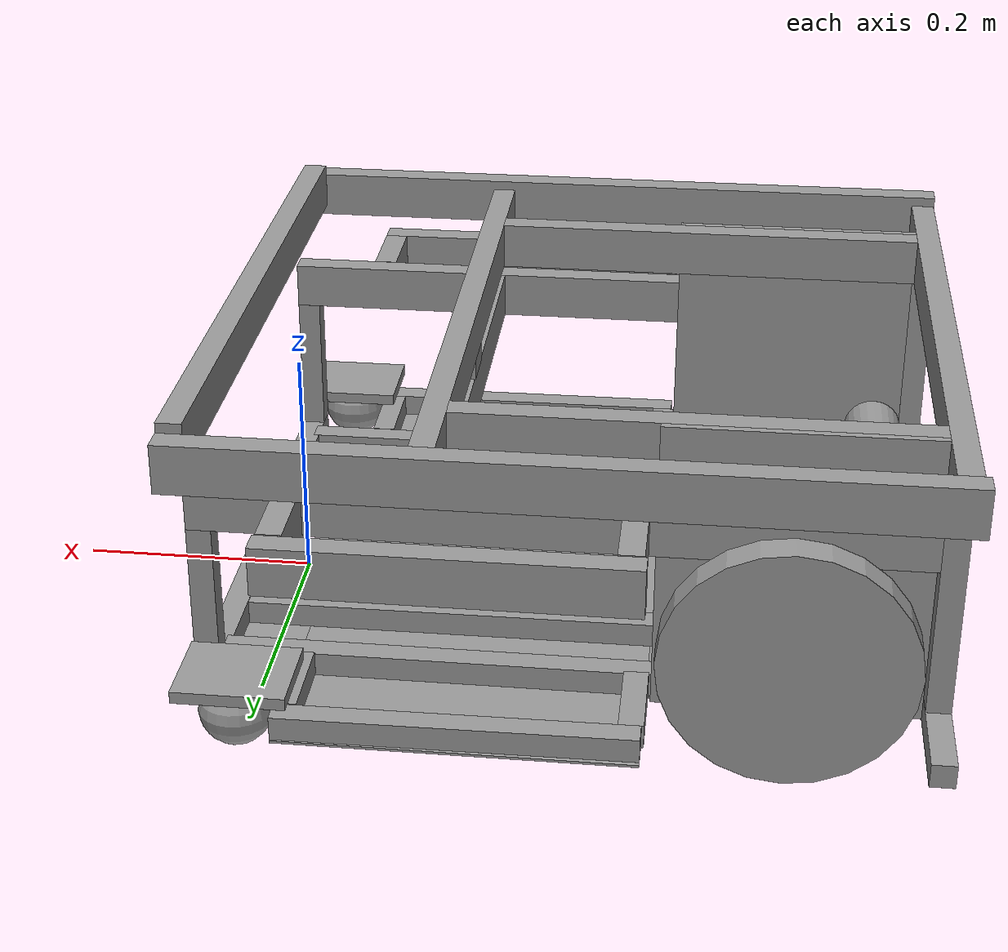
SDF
<?xml version='1.0'?>
<sdf version='1.6'>
  <model name='progetto'>
    <link name='link_3'>
      <pose frame=''>-0.017502 0 0.016 0 -0 0</pose>
      <inertial>
        <mass>0.011</mass>
        <inertia>
          <ixx>0.166667</ixx>
          <ixy>0</ixy>
          <ixz>0</ixz>
          <iyy>0.166667</iyy>
          <iyz>0</iyz>
          <izz>0.166667</izz>
        </inertia>
        <pose frame=''>0 0 0 0 -0 0</pose>
      </inertial>
      <self_collide>0</self_collide>
      <kinematic>0</kinematic>
      <visual name='visual'>
        <pose frame=''>0 0 0 0 -0 0</pose>
        <geometry>
          <box>
            <size>0.0205 0.174 0.002</size>
          </box>
        </geometry>
        <material>
          <lighting>1</lighting>
          <script>
            <uri>file://media/materials/scripts/gazebo.material</uri>
            <name>Gazebo/Grey</name>
          </script>
          <ambient>0.3 0.3 0.3 1</ambient>
          <diffuse>0.7 0.7 0.7 1</diffuse>
          <specular>0.01 0.01 0.01 1</specular>
          <emissive>0 0 0 1</emissive>
          <shader type='vertex'>
            <normal_map>__default__</normal_map>
          </shader>
        </material>
        <cast_shadows>1</cast_shadows>
        <transparency>0</transparency>
      </visual>
      <collision name='collision'>
        <laser_retro>0</laser_retro>
        <max_contacts>10</max_contacts>
        <pose frame=''>0 0 0 0 -0 0</pose>
        <geometry>
          <box>
            <size>0.0205 0.174 0.002</size>
          </box>
        </geometry>
        <surface>
          <friction>
            <ode>
              <mu>1</mu>
              <mu2>1</mu2>
              <fdir1>0 0 0</fdir1>
              <slip1>0</slip1>
              <slip2>0</slip2>
            </ode>
            <torsional>
              <coefficient>1</coefficient>
              <patch_radius>0</patch_radius>
              <surface_radius>0</surface_radius>
              <use_patch_radius>1</use_patch_radius>
              <ode>
                <slip>0</slip>
              </ode>
            </torsional>
          </friction>
          <bounce>
            <restitution_coefficient>0</restitution_coefficient>
            <threshold>1e+06</threshold>
          </bounce>
          <contact>
            <collide_without_contact>0</collide_without_contact>
            <collide_without_contact_bitmask>1</collide_without_contact_bitmask>
            <collide_bitmask>1</collide_bitmask>
            <ode>
              <soft_cfm>0</soft_cfm>
              <soft_erp>0.2</soft_erp>
              <kp>1e+13</kp>
              <kd>1</kd>
              <max_vel>0.01</max_vel>
              <min_depth>0</min_depth>
            </ode>
            <bullet>
              <split_impulse>1</split_impulse>
              <split_impulse_penetration_threshold>-0.01</split_impulse_penetration_threshold>
              <soft_cfm>0</soft_cfm>
              <soft_erp>0.2</soft_erp>
              <kp>1e+13</kp>
              <kd>1</kd>
            </bullet>
          </contact>
        </surface>
      </collision>
    </link>
    <link name='link_0'>
      <pose frame=''>-0.170752 0 0.016 0 -0 0</pose>
      <inertial>
        <mass>0.915</mass>
        <inertia>
          <ixx>0.166667</ixx>
          <ixy>0</ixy>
          <ixz>0</ixz>
          <iyy>0.166667</iyy>
          <iyz>0</iyz>
          <izz>0.166667</izz>
        </inertia>
        <pose frame=''>0 0 0 0 -0 0</pose>
      </inertial>
      <self_collide>0</self_collide>
      <kinematic>0</kinematic>
      <visual name='visual'>
        <pose frame=''>0 0 0 0 -0 0</pose>
        <geometry>
          <box>
            <size>0.286 0.596 0.002</size>
          </box>
        </geometry>
        <material>
          <lighting>1</lighting>
          <script>
            <uri>file://media/materials/scripts/gazebo.material</uri>
            <name>Gazebo/Grey</name>
          </script>
          <ambient>0.3 0.3 0.3 1</ambient>
          <diffuse>0.7 0.7 0.7 1</diffuse>
          <specular>0.01 0.01 0.01 1</specular>
          <emissive>0 0 0 1</emissive>
          <shader type='vertex'>
            <normal_map>__default__</normal_map>
          </shader>
        </material>
        <cast_shadows>1</cast_shadows>
        <transparency>0</transparency>
      </visual>
      <collision name='collision'>
        <laser_retro>0</laser_retro>
        <max_contacts>10</max_contacts>
        <pose frame=''>0 0 0 0 -0 0</pose>
        <geometry>
          <box>
            <size>0.286 0.596 0.002</size>
          </box>
        </geometry>
        <surface>
          <friction>
            <ode>
              <mu>1</mu>
              <mu2>1</mu2>
              <fdir1>0 0 0</fdir1>
              <slip1>0</slip1>
              <slip2>0</slip2>
            </ode>
            <torsional>
              <coefficient>1</coefficient>
              <patch_radius>0</patch_radius>
              <surface_radius>0</surface_radius>
              <use_patch_radius>1</use_patch_radius>
              <ode>
                <slip>0</slip>
              </ode>
            </torsional>
          </friction>
          <bounce>
            <restitution_coefficient>0</restitution_coefficient>
            <threshold>1e+06</threshold>
          </bounce>
          <contact>
            <collide_without_contact>0</collide_without_contact>
            <collide_without_contact_bitmask>1</collide_without_contact_bitmask>
            <collide_bitmask>1</collide_bitmask>
            <ode>
              <soft_cfm>0</soft_cfm>
              <soft_erp>0.2</soft_erp>
              <kp>1e+13</kp>
              <kd>1</kd>
              <max_vel>0.01</max_vel>
              <min_depth>0</min_depth>
            </ode>
            <bullet>
              <split_impulse>1</split_impulse>
              <split_impulse_penetration_threshold>-0.01</split_impulse_penetration_threshold>
              <soft_cfm>0</soft_cfm>
              <soft_erp>0.2</soft_erp>
              <kp>1e+13</kp>
              <kd>1</kd>
            </bullet>
          </contact>
        </surface>
      </collision>
    </link>
    <link name='link_0_0'>
      <pose frame=''>-0.540736 0 0.027 0 -0 0</pose>
      <inertial>
        <mass>0.296</mass>
        <inertia>
          <ixx>0.166667</ixx>
          <ixy>0</ixy>
          <ixz>0</ixz>
          <iyy>0.166667</iyy>
          <iyz>0</iyz>
          <izz>0.166667</izz>
        </inertia>
        <pose frame=''>0 0 0 0 -0 0</pose>
      </inertial>
      <self_collide>0</self_collide>
      <kinematic>0</kinematic>
      <visual name='visual'>
        <pose frame=''>0 0 0 0 -0 0</pose>
        <geometry>
          <box>
            <size>0.02 0.6 0.02</size>
          </box>
        </geometry>
        <material>
          <lighting>1</lighting>
          <script>
            <uri>file://media/materials/scripts/gazebo.material</uri>
            <name>Gazebo/Grey</name>
          </script>
          <ambient>0.3 0.3 0.3 1</ambient>
          <diffuse>0.7 0.7 0.7 1</diffuse>
          <specular>0.01 0.01 0.01 1</specular>
          <emissive>0 0 0 1</emissive>
          <shader type='vertex'>
            <normal_map>__default__</normal_map>
          </shader>
        </material>
        <cast_shadows>1</cast_shadows>
        <transparency>0</transparency>
      </visual>
      <collision name='collision'>
        <laser_retro>0</laser_retro>
        <max_contacts>10</max_contacts>
        <pose frame=''>0 0 0 0 -0 0</pose>
        <geometry>
          <box>
            <size>0.02 0.6 0.02</size>
          </box>
        </geometry>
        <surface>
          <friction>
            <ode>
              <mu>1</mu>
              <mu2>1</mu2>
              <fdir1>0 0 0</fdir1>
              <slip1>0</slip1>
              <slip2>0</slip2>
            </ode>
            <torsional>
              <coefficient>1</coefficient>
              <patch_radius>0</patch_radius>
              <surface_radius>0</surface_radius>
              <use_patch_radius>1</use_patch_radius>
              <ode>
                <slip>0</slip>
              </ode>
            </torsional>
          </friction>
          <bounce>
            <restitution_coefficient>0</restitution_coefficient>
            <threshold>1e+06</threshold>
          </bounce>
          <contact>
            <collide_without_contact>0</collide_without_contact>
            <collide_without_contact_bitmask>1</collide_without_contact_bitmask>
            <collide_bitmask>1</collide_bitmask>
            <ode>
              <soft_cfm>0</soft_cfm>
              <soft_erp>0.2</soft_erp>
              <kp>1e+13</kp>
              <kd>1</kd>
              <max_vel>0.01</max_vel>
              <min_depth>0</min_depth>
            </ode>
            <bullet>
              <split_impulse>1</split_impulse>
              <split_impulse_penetration_threshold>-0.01</split_impulse_penetration_threshold>
              <soft_cfm>0</soft_cfm>
              <soft_erp>0.2</soft_erp>
              <kp>1e+13</kp>
              <kd>1</kd>
            </bullet>
          </contact>
        </surface>
      </collision>
    </link>
    <link name='link_0_1'>
      <pose frame=''>-0.037 -0.266 0.182 0 -0 0</pose>
      <inertial>
        <mass>0.044</mass>
        <inertia>
          <ixx>0.166667</ixx>
          <ixy>0</ixy>
          <ixz>0</ixz>
          <iyy>0.166667</iyy>
          <iyz>0</iyz>
          <izz>0.166667</izz>
        </inertia>
        <pose frame=''>0 0 0 0 -0 0</pose>
      </inertial>
      <self_collide>0</self_collide>
      <kinematic>0</kinematic>
      <visual name='visual'>
        <pose frame=''>0 0 0 0 -0 0</pose>
        <geometry>
          <box>
            <size>0.02 0.069 0.04</size>
          </box>
        </geometry>
        <material>
          <lighting>1</lighting>
          <script>
            <uri>file://media/materials/scripts/gazebo.material</uri>
            <name>Gazebo/Grey</name>
          </script>
          <ambient>0.3 0.3 0.3 1</ambient>
          <diffuse>0.7 0.7 0.7 1</diffuse>
          <specular>0.01 0.01 0.01 1</specular>
          <emissive>0 0 0 1</emissive>
          <shader type='vertex'>
            <normal_map>__default__</normal_map>
          </shader>
        </material>
        <cast_shadows>1</cast_shadows>
        <transparency>0</transparency>
      </visual>
      <collision name='collision'>
        <laser_retro>0</laser_retro>
        <max_contacts>10</max_contacts>
        <pose frame=''>0 0 0 0 -0 0</pose>
        <geometry>
          <box>
            <size>0.02 0.069 0.04</size>
          </box>
        </geometry>
        <surface>
          <friction>
            <ode>
              <mu>1</mu>
              <mu2>1</mu2>
              <fdir1>0 0 0</fdir1>
              <slip1>0</slip1>
              <slip2>0</slip2>
            </ode>
            <torsional>
              <coefficient>1</coefficient>
              <patch_radius>0</patch_radius>
              <surface_radius>0</surface_radius>
              <use_patch_radius>1</use_patch_radius>
              <ode>
                <slip>0</slip>
              </ode>
            </torsional>
          </friction>
          <bounce>
            <restitution_coefficient>0</restitution_coefficient>
            <threshold>1e+06</threshold>
          </bounce>
          <contact>
            <collide_without_contact>0</collide_without_contact>
            <collide_without_contact_bitmask>1</collide_without_contact_bitmask>
            <collide_bitmask>1</collide_bitmask>
            <ode>
              <soft_cfm>0</soft_cfm>
              <soft_erp>0.2</soft_erp>
              <kp>1e+13</kp>
              <kd>1</kd>
              <max_vel>0.01</max_vel>
              <min_depth>0</min_depth>
            </ode>
            <bullet>
              <split_impulse>1</split_impulse>
              <split_impulse_penetration_threshold>-0.01</split_impulse_penetration_threshold>
              <soft_cfm>0</soft_cfm>
              <soft_erp>0.2</soft_erp>
              <kp>1e+13</kp>
              <kd>1</kd>
            </bullet>
          </contact>
        </surface>
      </collision>
    </link>
    <link name='link_0_1_clone'>
      <pose frame=''>-0.303 -0.266 0.182 0 -0 0</pose>
      <inertial>
        <mass>0.044</mass>
        <inertia>
          <ixx>0.166667</ixx>
          <ixy>0</ixy>
          <ixz>0</ixz>
          <iyy>0.166667</iyy>
          <iyz>0</iyz>
          <izz>0.166667</izz>
        </inertia>
        <pose frame=''>0 0 0 0 -0 0</pose>
      </inertial>
      <self_collide>0</self_collide>
      <kinematic>0</kinematic>
      <visual name='visual_0'>
        <pose frame=''>0 0 0 0 -0 0</pose>
        <geometry>
          <box>
            <size>0.02 0.069 0.04</size>
          </box>
        </geometry>
        <material>
          <lighting>1</lighting>
          <script>
            <uri>file://media/materials/scripts/gazebo.material</uri>
            <name>Gazebo/Grey</name>
          </script>
          <ambient>0.3 0.3 0.3 1</ambient>
          <diffuse>0.7 0.7 0.7 1</diffuse>
          <specular>0.01 0.01 0.01 1</specular>
          <emissive>0 0 0 1</emissive>
          <shader type='vertex'>
            <normal_map>__default__</normal_map>
          </shader>
        </material>
        <cast_shadows>1</cast_shadows>
        <transparency>0</transparency>
      </visual>
      <collision name='collision'>
        <laser_retro>0</laser_retro>
        <max_contacts>10</max_contacts>
        <pose frame=''>0 0 0 0 -0 0</pose>
        <geometry>
          <box>
            <size>0.02 0.069 0.04</size>
          </box>
        </geometry>
        <surface>
          <friction>
            <ode>
              <mu>1</mu>
              <mu2>1</mu2>
              <fdir1>0 0 0</fdir1>
              <slip1>0</slip1>
              <slip2>0</slip2>
            </ode>
            <torsional>
              <coefficient>1</coefficient>
              <patch_radius>0</patch_radius>
              <surface_radius>0</surface_radius>
              <use_patch_radius>1</use_patch_radius>
              <ode>
                <slip>0</slip>
              </ode>
            </torsional>
          </friction>
          <bounce>
            <restitution_coefficient>0</restitution_coefficient>
            <threshold>1e+06</threshold>
          </bounce>
          <contact>
            <collide_without_contact>0</collide_without_contact>
            <collide_without_contact_bitmask>1</collide_without_contact_bitmask>
            <collide_bitmask>1</collide_bitmask>
            <ode>
              <soft_cfm>0</soft_cfm>
              <soft_erp>0.2</soft_erp>
              <kp>1e+13</kp>
              <kd>1</kd>
              <max_vel>0.01</max_vel>
              <min_depth>0</min_depth>
            </ode>
            <bullet>
              <split_impulse>1</split_impulse>
              <split_impulse_penetration_threshold>-0.01</split_impulse_penetration_threshold>
              <soft_cfm>0</soft_cfm>
              <soft_erp>0.2</soft_erp>
              <kp>1e+13</kp>
              <kd>1</kd>
            </bullet>
          </contact>
        </surface>
      </collision>
    </link>
    <link name='link_0_1_clone_0'>
      <pose frame=''>-0.037 0.266 0.182 0 -0 0</pose>
      <inertial>
        <mass>0.044</mass>
        <inertia>
          <ixx>0.166667</ixx>
          <ixy>0</ixy>
          <ixz>0</ixz>
          <iyy>0.166667</iyy>
          <iyz>0</iyz>
          <izz>0.166667</izz>
        </inertia>
        <pose frame=''>0 0 0 0 -0 0</pose>
      </inertial>
      <self_collide>0</self_collide>
      <kinematic>0</kinematic>
      <visual name='visual_0'>
        <pose frame=''>0 0 0 0 -0 0</pose>
        <geometry>
          <box>
            <size>0.02 0.069 0.04</size>
          </box>
        </geometry>
        <material>
          <lighting>1</lighting>
          <script>
            <uri>file://media/materials/scripts/gazebo.material</uri>
            <name>Gazebo/Grey</name>
          </script>
          <ambient>0.3 0.3 0.3 1</ambient>
          <diffuse>0.7 0.7 0.7 1</diffuse>
          <specular>0.01 0.01 0.01 1</specular>
          <emissive>0 0 0 1</emissive>
          <shader type='vertex'>
            <normal_map>__default__</normal_map>
          </shader>
        </material>
        <cast_shadows>1</cast_shadows>
        <transparency>0</transparency>
      </visual>
      <collision name='collision'>
        <laser_retro>0</laser_retro>
        <max_contacts>10</max_contacts>
        <pose frame=''>0 0 0 0 -0 0</pose>
        <geometry>
          <box>
            <size>0.02 0.069 0.04</size>
          </box>
        </geometry>
        <surface>
          <friction>
            <ode>
              <mu>1</mu>
              <mu2>1</mu2>
              <fdir1>0 0 0</fdir1>
              <slip1>0</slip1>
              <slip2>0</slip2>
            </ode>
            <torsional>
              <coefficient>1</coefficient>
              <patch_radius>0</patch_radius>
              <surface_radius>0</surface_radius>
              <use_patch_radius>1</use_patch_radius>
              <ode>
                <slip>0</slip>
              </ode>
            </torsional>
          </friction>
          <bounce>
            <restitution_coefficient>0</restitution_coefficient>
            <threshold>1e+06</threshold>
          </bounce>
          <contact>
            <collide_without_contact>0</collide_without_contact>
            <collide_without_contact_bitmask>1</collide_without_contact_bitmask>
            <collide_bitmask>1</collide_bitmask>
            <ode>
              <soft_cfm>0</soft_cfm>
              <soft_erp>0.2</soft_erp>
              <kp>1e+13</kp>
              <kd>1</kd>
              <max_vel>0.01</max_vel>
              <min_depth>0</min_depth>
            </ode>
            <bullet>
              <split_impulse>1</split_impulse>
              <split_impulse_penetration_threshold>-0.01</split_impulse_penetration_threshold>
              <soft_cfm>0</soft_cfm>
              <soft_erp>0.2</soft_erp>
              <kp>1e+13</kp>
              <kd>1</kd>
            </bullet>
          </contact>
        </surface>
      </collision>
    </link>
    <link name='link_0_1_clone_1'>
      <pose frame=''>-0.303 0.266 0.182 0 -0 0</pose>
      <inertial>
        <mass>0.044</mass>
        <inertia>
          <ixx>0.166667</ixx>
          <ixy>0</ixy>
          <ixz>0</ixz>
          <iyy>0.166667</iyy>
          <iyz>0</iyz>
          <izz>0.166667</izz>
        </inertia>
        <pose frame=''>0 0 0 0 -0 0</pose>
      </inertial>
      <self_collide>0</self_collide>
      <kinematic>0</kinematic>
      <visual name='visual_0'>
        <pose frame=''>0 0 0 0 -0 0</pose>
        <geometry>
          <box>
            <size>0.02 0.069 0.04</size>
          </box>
        </geometry>
        <material>
          <lighting>1</lighting>
          <script>
            <uri>file://media/materials/scripts/gazebo.material</uri>
            <name>Gazebo/Grey</name>
          </script>
          <ambient>0.3 0.3 0.3 1</ambient>
          <diffuse>0.7 0.7 0.7 1</diffuse>
          <specular>0.01 0.01 0.01 1</specular>
          <emissive>0 0 0 1</emissive>
          <shader type='vertex'>
            <normal_map>__default__</normal_map>
          </shader>
        </material>
        <cast_shadows>1</cast_shadows>
        <transparency>0</transparency>
      </visual>
      <collision name='collision'>
        <laser_retro>0</laser_retro>
        <max_contacts>10</max_contacts>
        <pose frame=''>0 0 0 0 -0 0</pose>
        <geometry>
          <box>
            <size>0.02 0.069 0.04</size>
          </box>
        </geometry>
        <surface>
          <friction>
            <ode>
              <mu>1</mu>
              <mu2>1</mu2>
              <fdir1>0 0 0</fdir1>
              <slip1>0</slip1>
              <slip2>0</slip2>
            </ode>
            <torsional>
              <coefficient>1</coefficient>
              <patch_radius>0</patch_radius>
              <surface_radius>0</surface_radius>
              <use_patch_radius>1</use_patch_radius>
              <ode>
                <slip>0</slip>
              </ode>
            </torsional>
          </friction>
          <bounce>
            <restitution_coefficient>0</restitution_coefficient>
            <threshold>1e+06</threshold>
          </bounce>
          <contact>
            <collide_without_contact>0</collide_without_contact>
            <collide_without_contact_bitmask>1</collide_without_contact_bitmask>
            <collide_bitmask>1</collide_bitmask>
            <ode>
              <soft_cfm>0</soft_cfm>
              <soft_erp>0.2</soft_erp>
              <kp>1e+13</kp>
              <kd>1</kd>
              <max_vel>0.01</max_vel>
              <min_depth>0</min_depth>
            </ode>
            <bullet>
              <split_impulse>1</split_impulse>
              <split_impulse_penetration_threshold>-0.01</split_impulse_penetration_threshold>
              <soft_cfm>0</soft_cfm>
              <soft_erp>0.2</soft_erp>
              <kp>1e+13</kp>
              <kd>1</kd>
            </bullet>
          </contact>
        </surface>
      </collision>
    </link>
    <link name='link_0_1_clone_2'>
      <pose frame=''>-0.3055 -0.240778 0.02778 0.00195 0.002427 0.000918</pose>
      <inertial>
        <mass>0.037</mass>
        <inertia>
          <ixx>0.166667</ixx>
          <ixy>0</ixy>
          <ixz>0</ixz>
          <iyy>0.166667</iyy>
          <iyz>0</iyz>
          <izz>0.166667</izz>
        </inertia>
        <pose frame=''>0 0 0 0 -0 0</pose>
      </inertial>
      <self_collide>0</self_collide>
      <kinematic>0</kinematic>
      <visual name='visual'>
        <pose frame=''>0 0 0 0 -0 0</pose>
        <geometry>
          <box>
            <size>0.02 0.075 0.02</size>
          </box>
        </geometry>
        <material>
          <lighting>1</lighting>
          <script>
            <uri>file://media/materials/scripts/gazebo.material</uri>
            <name>Gazebo/Grey</name>
          </script>
          <ambient>0.3 0.3 0.3 1</ambient>
          <diffuse>0.7 0.7 0.7 1</diffuse>
          <specular>0.01 0.01 0.01 1</specular>
          <emissive>0 0 0 1</emissive>
          <shader type='vertex'>
            <normal_map>__default__</normal_map>
          </shader>
        </material>
        <cast_shadows>1</cast_shadows>
        <transparency>0</transparency>
      </visual>
      <collision name='collision'>
        <laser_retro>0</laser_retro>
        <max_contacts>10</max_contacts>
        <pose frame=''>0 0 0 0 -0 0</pose>
        <geometry>
          <box>
            <size>0.02 0.075 0.02</size>
          </box>
        </geometry>
        <surface>
          <friction>
            <ode>
              <mu>1</mu>
              <mu2>1</mu2>
              <fdir1>0 0 0</fdir1>
              <slip1>0</slip1>
              <slip2>0</slip2>
            </ode>
            <torsional>
              <coefficient>1</coefficient>
              <patch_radius>0</patch_radius>
              <surface_radius>0</surface_radius>
              <use_patch_radius>1</use_patch_radius>
              <ode>
                <slip>0</slip>
              </ode>
            </torsional>
          </friction>
          <bounce>
            <restitution_coefficient>0</restitution_coefficient>
            <threshold>1e+06</threshold>
          </bounce>
          <contact>
            <collide_without_contact>0</collide_without_contact>
            <collide_without_contact_bitmask>1</collide_without_contact_bitmask>
            <collide_bitmask>1</collide_bitmask>
            <ode>
              <soft_cfm>0</soft_cfm>
              <soft_erp>0.2</soft_erp>
              <kp>1e+13</kp>
              <kd>1</kd>
              <max_vel>0.01</max_vel>
              <min_depth>0</min_depth>
            </ode>
            <bullet>
              <split_impulse>1</split_impulse>
              <split_impulse_penetration_threshold>-0.01</split_impulse_penetration_threshold>
              <soft_cfm>0</soft_cfm>
              <soft_erp>0.2</soft_erp>
              <kp>1e+13</kp>
              <kd>1</kd>
            </bullet>
          </contact>
        </surface>
      </collision>
    </link>
    <link name='link_0_1_clone_2_clone'>
      <pose frame=''>-0.035562 -0.240502 0.027131 0.003903 0.004852 0.001841</pose>
      <inertial>
        <mass>0.037</mass>
        <inertia>
          <ixx>0.166667</ixx>
          <ixy>0</ixy>
          <ixz>0</ixz>
          <iyy>0.166667</iyy>
          <iyz>0</iyz>
          <izz>0.166667</izz>
        </inertia>
        <pose frame=''>0 0 0 0 -0 0</pose>
      </inertial>
      <self_collide>0</self_collide>
      <kinematic>0</kinematic>
      <visual name='visual'>
        <pose frame=''>0 0 0 0 -0 0</pose>
        <geometry>
          <box>
            <size>0.02 0.075 0.02</size>
          </box>
        </geometry>
        <material>
          <lighting>1</lighting>
          <script>
            <uri>file://media/materials/scripts/gazebo.material</uri>
            <name>Gazebo/Grey</name>
          </script>
          <ambient>0.3 0.3 0.3 1</ambient>
          <diffuse>0.7 0.7 0.7 1</diffuse>
          <specular>0.01 0.01 0.01 1</specular>
          <emissive>0 0 0 1</emissive>
          <shader type='vertex'>
            <normal_map>__default__</normal_map>
          </shader>
        </material>
        <cast_shadows>1</cast_shadows>
        <transparency>0</transparency>
      </visual>
      <collision name='collision'>
        <laser_retro>0</laser_retro>
        <max_contacts>10</max_contacts>
        <pose frame=''>0 0 0 0 -0 0</pose>
        <geometry>
          <box>
            <size>0.02 0.075 0.02</size>
          </box>
        </geometry>
        <surface>
          <friction>
            <ode>
              <mu>1</mu>
              <mu2>1</mu2>
              <fdir1>0 0 0</fdir1>
              <slip1>0</slip1>
              <slip2>0</slip2>
            </ode>
            <torsional>
              <coefficient>1</coefficient>
              <patch_radius>0</patch_radius>
              <surface_radius>0</surface_radius>
              <use_patch_radius>1</use_patch_radius>
              <ode>
                <slip>0</slip>
              </ode>
            </torsional>
          </friction>
          <bounce>
            <restitution_coefficient>0</restitution_coefficient>
            <threshold>1e+06</threshold>
          </bounce>
          <contact>
            <collide_without_contact>0</collide_without_contact>
            <collide_without_contact_bitmask>1</collide_without_contact_bitmask>
            <collide_bitmask>1</collide_bitmask>
            <ode>
              <soft_cfm>0</soft_cfm>
              <soft_erp>0.2</soft_erp>
              <kp>1e+13</kp>
              <kd>1</kd>
              <max_vel>0.01</max_vel>
              <min_depth>0</min_depth>
            </ode>
            <bullet>
              <split_impulse>1</split_impulse>
              <split_impulse_penetration_threshold>-0.01</split_impulse_penetration_threshold>
              <soft_cfm>0</soft_cfm>
              <soft_erp>0.2</soft_erp>
              <kp>1e+13</kp>
              <kd>1</kd>
            </bullet>
          </contact>
        </surface>
      </collision>
    </link>
    <link name='link_0_1_clone_2_clone_0'>
      <pose frame=''>-0.305916 0.24015 0.029095 0.003903 0.004852 0.001841</pose>
      <inertial>
        <mass>0.037</mass>
        <inertia>
          <ixx>0.166667</ixx>
          <ixy>0</ixy>
          <ixz>0</ixz>
          <iyy>0.166667</iyy>
          <iyz>0</iyz>
          <izz>0.166667</izz>
        </inertia>
        <pose frame=''>0 0 0 0 -0 0</pose>
      </inertial>
      <self_collide>0</self_collide>
      <kinematic>0</kinematic>
      <visual name='visual'>
        <pose frame=''>0 0 0 0 -0 0</pose>
        <geometry>
          <box>
            <size>0.02 0.075 0.02</size>
          </box>
        </geometry>
        <material>
          <lighting>1</lighting>
          <script>
            <uri>file://media/materials/scripts/gazebo.material</uri>
            <name>Gazebo/Grey</name>
          </script>
          <ambient>0.3 0.3 0.3 1</ambient>
          <diffuse>0.7 0.7 0.7 1</diffuse>
          <specular>0.01 0.01 0.01 1</specular>
          <emissive>0 0 0 1</emissive>
          <shader type='vertex'>
            <normal_map>__default__</normal_map>
          </shader>
        </material>
        <cast_shadows>1</cast_shadows>
        <transparency>0</transparency>
      </visual>
      <collision name='collision'>
        <laser_retro>0</laser_retro>
        <max_contacts>10</max_contacts>
        <pose frame=''>0 0 0 0 -0 0</pose>
        <geometry>
          <box>
            <size>0.02 0.075 0.02</size>
          </box>
        </geometry>
        <surface>
          <friction>
            <ode>
              <mu>1</mu>
              <mu2>1</mu2>
              <fdir1>0 0 0</fdir1>
              <slip1>0</slip1>
              <slip2>0</slip2>
            </ode>
            <torsional>
              <coefficient>1</coefficient>
              <patch_radius>0</patch_radius>
              <surface_radius>0</surface_radius>
              <use_patch_radius>1</use_patch_radius>
              <ode>
                <slip>0</slip>
              </ode>
            </torsional>
          </friction>
          <bounce>
            <restitution_coefficient>0</restitution_coefficient>
            <threshold>1e+06</threshold>
          </bounce>
          <contact>
            <collide_without_contact>0</collide_without_contact>
            <collide_without_contact_bitmask>1</collide_without_contact_bitmask>
            <collide_bitmask>1</collide_bitmask>
            <ode>
              <soft_cfm>0</soft_cfm>
              <soft_erp>0.2</soft_erp>
              <kp>1e+13</kp>
              <kd>1</kd>
              <max_vel>0.01</max_vel>
              <min_depth>0</min_depth>
            </ode>
            <bullet>
              <split_impulse>1</split_impulse>
              <split_impulse_penetration_threshold>-0.01</split_impulse_penetration_threshold>
              <soft_cfm>0</soft_cfm>
              <soft_erp>0.2</soft_erp>
              <kp>1e+13</kp>
              <kd>1</kd>
            </bullet>
          </contact>
        </surface>
      </collision>
    </link>
    <link name='link_0_1_clone_2_clone_0_clone'>
      <pose frame=''>-0.036026 0.240369 0.02844 0.005858 0.007276 0.002769</pose>
      <inertial>
        <mass>0.037</mass>
        <inertia>
          <ixx>0.166667</ixx>
          <ixy>0</ixy>
          <ixz>0</ixz>
          <iyy>0.166667</iyy>
          <iyz>0</iyz>
          <izz>0.166667</izz>
        </inertia>
        <pose frame=''>0 0 0 0 -0 0</pose>
      </inertial>
      <self_collide>0</self_collide>
      <kinematic>0</kinematic>
      <visual name='visual'>
        <pose frame=''>0 0 0 0 -0 0</pose>
        <geometry>
          <box>
            <size>0.02 0.075 0.02</size>
          </box>
        </geometry>
        <material>
          <lighting>1</lighting>
          <script>
            <uri>file://media/materials/scripts/gazebo.material</uri>
            <name>Gazebo/Grey</name>
          </script>
          <ambient>0.3 0.3 0.3 1</ambient>
          <diffuse>0.7 0.7 0.7 1</diffuse>
          <specular>0.01 0.01 0.01 1</specular>
          <emissive>0 0 0 1</emissive>
          <shader type='vertex'>
            <normal_map>__default__</normal_map>
          </shader>
        </material>
        <cast_shadows>1</cast_shadows>
        <transparency>0</transparency>
      </visual>
      <collision name='collision'>
        <laser_retro>0</laser_retro>
        <max_contacts>10</max_contacts>
        <pose frame=''>0 0 0 0 -0 0</pose>
        <geometry>
          <box>
            <size>0.02 0.075 0.02</size>
          </box>
        </geometry>
        <surface>
          <friction>
            <ode>
              <mu>1</mu>
              <mu2>1</mu2>
              <fdir1>0 0 0</fdir1>
              <slip1>0</slip1>
              <slip2>0</slip2>
            </ode>
            <torsional>
              <coefficient>1</coefficient>
              <patch_radius>0</patch_radius>
              <surface_radius>0</surface_radius>
              <use_patch_radius>1</use_patch_radius>
              <ode>
                <slip>0</slip>
              </ode>
            </torsional>
          </friction>
          <bounce>
            <restitution_coefficient>0</restitution_coefficient>
            <threshold>1e+06</threshold>
          </bounce>
          <contact>
            <collide_without_contact>0</collide_without_contact>
            <collide_without_contact_bitmask>1</collide_without_contact_bitmask>
            <collide_bitmask>1</collide_bitmask>
            <ode>
              <soft_cfm>0</soft_cfm>
              <soft_erp>0.2</soft_erp>
              <kp>1e+13</kp>
              <kd>1</kd>
              <max_vel>0.01</max_vel>
              <min_depth>0</min_depth>
            </ode>
            <bullet>
              <split_impulse>1</split_impulse>
              <split_impulse_penetration_threshold>-0.01</split_impulse_penetration_threshold>
              <soft_cfm>0</soft_cfm>
              <soft_erp>0.2</soft_erp>
              <kp>1e+13</kp>
              <kd>1</kd>
            </bullet>
          </contact>
        </surface>
      </collision>
    </link>
    <link name='link_0_2'>
      <pose frame=''>-0.421 -0.24 0.1 1.5707 -0 0</pose>
      <inertial>
        <mass>0.006</mass>
        <inertia>
          <ixx>0.145833</ixx>
          <ixy>0</ixy>
          <ixz>0</ixz>
          <iyy>0.145833</iyy>
          <iyz>0</iyz>
          <izz>0.125</izz>
        </inertia>
        <pose frame=''>0 0 0 0 -0 0</pose>
      </inertial>
      <self_collide>0</self_collide>
      <kinematic>0</kinematic>
      <visual name='visual'>
        <pose frame=''>0 0 0 0 -0 0</pose>
        <geometry>
          <cylinder>
            <radius>0.01</radius>
            <length>0.04</length>
          </cylinder>
        </geometry>
        <material>
          <lighting>1</lighting>
          <script>
            <uri>file://media/materials/scripts/gazebo.material</uri>
            <name>Gazebo/Grey</name>
          </script>
          <ambient>0.3 0.3 0.3 1</ambient>
          <diffuse>0.7 0.7 0.7 1</diffuse>
          <specular>0.01 0.01 0.01 1</specular>
          <emissive>0 0 0 1</emissive>
          <shader type='vertex'>
            <normal_map>__default__</normal_map>
          </shader>
        </material>
        <cast_shadows>1</cast_shadows>
        <transparency>0</transparency>
      </visual>
      <collision name='collision'>
        <laser_retro>0</laser_retro>
        <max_contacts>10</max_contacts>
        <pose frame=''>0 0 0 0 -0 0</pose>
        <geometry>
          <cylinder>
            <radius>0.01</radius>
            <length>0.04</length>
          </cylinder>
        </geometry>
        <surface>
          <friction>
            <ode>
              <mu>1</mu>
              <mu2>1</mu2>
              <fdir1>0 0 0</fdir1>
              <slip1>0</slip1>
              <slip2>0</slip2>
            </ode>
            <torsional>
              <coefficient>1</coefficient>
              <patch_radius>0</patch_radius>
              <surface_radius>0</surface_radius>
              <use_patch_radius>1</use_patch_radius>
              <ode>
                <slip>0</slip>
              </ode>
            </torsional>
          </friction>
          <bounce>
            <restitution_coefficient>0</restitution_coefficient>
            <threshold>1e+06</threshold>
          </bounce>
          <contact>
            <collide_without_contact>0</collide_without_contact>
            <collide_without_contact_bitmask>1</collide_without_contact_bitmask>
            <collide_bitmask>1</collide_bitmask>
            <ode>
              <soft_cfm>0</soft_cfm>
              <soft_erp>0.2</soft_erp>
              <kp>1e+13</kp>
              <kd>1</kd>
              <max_vel>0.01</max_vel>
              <min_depth>0</min_depth>
            </ode>
            <bullet>
              <split_impulse>1</split_impulse>
              <split_impulse_penetration_threshold>-0.01</split_impulse_penetration_threshold>
              <soft_cfm>0</soft_cfm>
              <soft_erp>0.2</soft_erp>
              <kp>1e+13</kp>
              <kd>1</kd>
            </bullet>
          </contact>
        </surface>
      </collision>
    </link>
    <link name='link_0_2_clone'>
      <pose frame=''>-0.421 0.24 0.1 1.5707 -0.001091 0.036355</pose>
      <inertial>
        <mass>0.006</mass>
        <inertia>
          <ixx>0.145833</ixx>
          <ixy>0</ixy>
          <ixz>0</ixz>
          <iyy>0.145833</iyy>
          <iyz>0</iyz>
          <izz>0.125</izz>
        </inertia>
        <pose frame=''>0 0 0 0 -0 0</pose>
      </inertial>
      <self_collide>0</self_collide>
      <kinematic>0</kinematic>
      <visual name='visual_0'>
        <pose frame=''>0 0 0 0 -0 0</pose>
        <geometry>
          <cylinder>
            <radius>0.01</radius>
            <length>0.04</length>
          </cylinder>
        </geometry>
        <material>
          <lighting>1</lighting>
          <script>
            <uri>file://media/materials/scripts/gazebo.material</uri>
            <name>Gazebo/Grey</name>
          </script>
          <ambient>0.3 0.3 0.3 1</ambient>
          <diffuse>0.7 0.7 0.7 1</diffuse>
          <specular>0.01 0.01 0.01 1</specular>
          <emissive>0 0 0 1</emissive>
          <shader type='vertex'>
            <normal_map>__default__</normal_map>
          </shader>
        </material>
        <cast_shadows>1</cast_shadows>
        <transparency>0</transparency>
      </visual>
      <collision name='collision'>
        <laser_retro>0</laser_retro>
        <max_contacts>10</max_contacts>
        <pose frame=''>0 0 0 0 -0 0</pose>
        <geometry>
          <cylinder>
            <radius>0.01</radius>
            <length>0.04</length>
          </cylinder>
        </geometry>
        <surface>
          <friction>
            <ode>
              <mu>1</mu>
              <mu2>1</mu2>
              <fdir1>0 0 0</fdir1>
              <slip1>0</slip1>
              <slip2>0</slip2>
            </ode>
            <torsional>
              <coefficient>1</coefficient>
              <patch_radius>0</patch_radius>
              <surface_radius>0</surface_radius>
              <use_patch_radius>1</use_patch_radius>
              <ode>
                <slip>0</slip>
              </ode>
            </torsional>
          </friction>
          <bounce>
            <restitution_coefficient>0</restitution_coefficient>
            <threshold>1e+06</threshold>
          </bounce>
          <contact>
            <collide_without_contact>0</collide_without_contact>
            <collide_without_contact_bitmask>1</collide_without_contact_bitmask>
            <collide_bitmask>1</collide_bitmask>
            <ode>
              <soft_cfm>0</soft_cfm>
              <soft_erp>0.2</soft_erp>
              <kp>1e+13</kp>
              <kd>1</kd>
              <max_vel>0.01</max_vel>
              <min_depth>0</min_depth>
            </ode>
            <bullet>
              <split_impulse>1</split_impulse>
              <split_impulse_penetration_threshold>-0.01</split_impulse_penetration_threshold>
              <soft_cfm>0</soft_cfm>
              <soft_erp>0.2</soft_erp>
              <kp>1e+13</kp>
              <kd>1</kd>
            </bullet>
          </contact>
        </surface>
      </collision>
    </link>
    <link name='link_0_3'>
      <pose frame=''>-0.146053 -0 0.242 0 -0 0</pose>
      <inertial>
        <mass>0.5</mass>
        <inertia>
          <ixx>0.166667</ixx>
          <ixy>0</ixy>
          <ixz>0</ixz>
          <iyy>0.166667</iyy>
          <iyz>0</iyz>
          <izz>0.166667</izz>
        </inertia>
        <pose frame=''>0 0 0 0 -0 0</pose>
      </inertial>
      <self_collide>0</self_collide>
      <kinematic>0</kinematic>
      <visual name='visual'>
        <pose frame=''>0 0 0 0 -0 0</pose>
        <geometry>
          <box>
            <size>0.02 0.56 0.04</size>
          </box>
        </geometry>
        <material>
          <lighting>1</lighting>
          <script>
            <uri>file://media/materials/scripts/gazebo.material</uri>
            <name>Gazebo/Grey</name>
          </script>
          <ambient>0.3 0.3 0.3 1</ambient>
          <diffuse>0.7 0.7 0.7 1</diffuse>
          <specular>0.01 0.01 0.01 1</specular>
          <emissive>0 0 0 1</emissive>
          <shader type='vertex'>
            <normal_map>__default__</normal_map>
          </shader>
        </material>
        <cast_shadows>1</cast_shadows>
        <transparency>0</transparency>
      </visual>
      <collision name='collision'>
        <laser_retro>0</laser_retro>
        <max_contacts>10</max_contacts>
        <pose frame=''>0 0 0 0 -0 0</pose>
        <geometry>
          <box>
            <size>0.02 0.56 0.04</size>
          </box>
        </geometry>
        <surface>
          <friction>
            <ode>
              <mu>1</mu>
              <mu2>1</mu2>
              <fdir1>0 0 0</fdir1>
              <slip1>0</slip1>
              <slip2>0</slip2>
            </ode>
            <torsional>
              <coefficient>1</coefficient>
              <patch_radius>0</patch_radius>
              <surface_radius>0</surface_radius>
              <use_patch_radius>1</use_patch_radius>
              <ode>
                <slip>0</slip>
              </ode>
            </torsional>
          </friction>
          <bounce>
            <restitution_coefficient>0</restitution_coefficient>
            <threshold>1e+06</threshold>
          </bounce>
          <contact>
            <collide_without_contact>0</collide_without_contact>
            <collide_without_contact_bitmask>1</collide_without_contact_bitmask>
            <collide_bitmask>1</collide_bitmask>
            <ode>
              <soft_cfm>0</soft_cfm>
              <soft_erp>0.2</soft_erp>
              <kp>1e+13</kp>
              <kd>1</kd>
              <max_vel>0.01</max_vel>
              <min_depth>0</min_depth>
            </ode>
            <bullet>
              <split_impulse>1</split_impulse>
              <split_impulse_penetration_threshold>-0.01</split_impulse_penetration_threshold>
              <soft_cfm>0</soft_cfm>
              <soft_erp>0.2</soft_erp>
              <kp>1e+13</kp>
              <kd>1</kd>
            </bullet>
          </contact>
        </surface>
      </collision>
    </link>
    <link name='link_0_3_clone'>
      <pose frame=''>0.037158 0.001653 0.259467 0 -0 0</pose>
      <inertial>
        <mass>0.5</mass>
        <inertia>
          <ixx>0.166667</ixx>
          <ixy>0</ixy>
          <ixz>0</ixz>
          <iyy>0.166667</iyy>
          <iyz>0</iyz>
          <izz>0.166667</izz>
        </inertia>
        <pose frame=''>0 0 0 0 -0 0</pose>
      </inertial>
      <self_collide>0</self_collide>
      <kinematic>0</kinematic>
      <visual name='visual_0'>
        <pose frame=''>0 0 0 0 -0 0</pose>
        <geometry>
          <box>
            <size>0.02 0.56 0.04</size>
          </box>
        </geometry>
        <material>
          <lighting>1</lighting>
          <script>
            <uri>file://media/materials/scripts/gazebo.material</uri>
            <name>Gazebo/Grey</name>
          </script>
          <ambient>0.3 0.3 0.3 1</ambient>
          <diffuse>0.7 0.7 0.7 1</diffuse>
          <specular>0.01 0.01 0.01 1</specular>
          <emissive>0 0 0 1</emissive>
          <shader type='vertex'>
            <normal_map>__default__</normal_map>
          </shader>
        </material>
        <cast_shadows>1</cast_shadows>
        <transparency>0</transparency>
      </visual>
      <collision name='collision'>
        <laser_retro>0</laser_retro>
        <max_contacts>10</max_contacts>
        <pose frame=''>0 0 0 0 -0 0</pose>
        <geometry>
          <box>
            <size>0.02 0.56 0.04</size>
          </box>
        </geometry>
        <surface>
          <friction>
            <ode>
              <mu>1</mu>
              <mu2>1</mu2>
              <fdir1>0 0 0</fdir1>
              <slip1>0</slip1>
              <slip2>0</slip2>
            </ode>
            <torsional>
              <coefficient>1</coefficient>
              <patch_radius>0</patch_radius>
              <surface_radius>0</surface_radius>
              <use_patch_radius>1</use_patch_radius>
              <ode>
                <slip>0</slip>
              </ode>
            </torsional>
          </friction>
          <bounce>
            <restitution_coefficient>0</restitution_coefficient>
            <threshold>1e+06</threshold>
          </bounce>
          <contact>
            <collide_without_contact>0</collide_without_contact>
            <collide_without_contact_bitmask>1</collide_without_contact_bitmask>
            <collide_bitmask>1</collide_bitmask>
            <ode>
              <soft_cfm>0</soft_cfm>
              <soft_erp>0.2</soft_erp>
              <kp>1e+13</kp>
              <kd>1</kd>
              <max_vel>0.01</max_vel>
              <min_depth>0</min_depth>
            </ode>
            <bullet>
              <split_impulse>1</split_impulse>
              <split_impulse_penetration_threshold>-0.01</split_impulse_penetration_threshold>
              <soft_cfm>0</soft_cfm>
              <soft_erp>0.2</soft_erp>
              <kp>1e+13</kp>
              <kd>1</kd>
            </bullet>
          </contact>
        </surface>
      </collision>
    </link>
    <link name='link_0_4'>
      <pose frame=''>-0.354982 0.002159 0.027561 0.001563 0.002444 0.000827</pose>
      <inertial>
        <mass>0.183</mass>
        <inertia>
          <ixx>0.166667</ixx>
          <ixy>0</ixy>
          <ixz>0</ixz>
          <iyy>0.166667</iyy>
          <iyz>0</iyz>
          <izz>0.166667</izz>
        </inertia>
        <pose frame=''>0 0 0 0 -0 0</pose>
      </inertial>
      <gravity>1</gravity>
      <self_collide>0</self_collide>
      <kinematic>0</kinematic>
      <visual name='visual'>
        <pose frame=''>0 0 0 0 -0 0</pose>
        <geometry>
          <box>
            <size>0.02 0.37 0.02</size>
          </box>
        </geometry>
        <material>
          <lighting>1</lighting>
          <script>
            <uri>file://media/materials/scripts/gazebo.material</uri>
            <name>Gazebo/Grey</name>
          </script>
          <ambient>0.3 0.3 0.3 1</ambient>
          <diffuse>0.7 0.7 0.7 1</diffuse>
          <specular>0.01 0.01 0.01 1</specular>
          <emissive>0 0 0 1</emissive>
          <shader type='vertex'>
            <normal_map>__default__</normal_map>
          </shader>
        </material>
        <cast_shadows>1</cast_shadows>
        <transparency>0</transparency>
      </visual>
      <collision name='collision'>
        <laser_retro>0</laser_retro>
        <max_contacts>10</max_contacts>
        <pose frame=''>0 0 0 0 -0 0</pose>
        <geometry>
          <box>
            <size>0.02 0.37 0.02</size>
          </box>
        </geometry>
        <surface>
          <friction>
            <ode>
              <mu>1</mu>
              <mu2>1</mu2>
              <fdir1>0 0 0</fdir1>
              <slip1>0</slip1>
              <slip2>0</slip2>
            </ode>
            <torsional>
              <coefficient>1</coefficient>
              <patch_radius>0</patch_radius>
              <surface_radius>0</surface_radius>
              <use_patch_radius>1</use_patch_radius>
              <ode>
                <slip>0</slip>
              </ode>
            </torsional>
          </friction>
          <bounce>
            <restitution_coefficient>0</restitution_coefficient>
            <threshold>1e+06</threshold>
          </bounce>
          <contact>
            <collide_without_contact>0</collide_without_contact>
            <collide_without_contact_bitmask>1</collide_without_contact_bitmask>
            <collide_bitmask>1</collide_bitmask>
            <ode>
              <soft_cfm>0</soft_cfm>
              <soft_erp>0.2</soft_erp>
              <kp>1e+13</kp>
              <kd>1</kd>
              <max_vel>0.01</max_vel>
              <min_depth>0</min_depth>
            </ode>
            <bullet>
              <split_impulse>1</split_impulse>
              <split_impulse_penetration_threshold>-0.01</split_impulse_penetration_threshold>
              <soft_cfm>0</soft_cfm>
              <soft_erp>0.2</soft_erp>
              <kp>1e+13</kp>
              <kd>1</kd>
            </bullet>
          </contact>
        </surface>
      </collision>
    </link>
    <link name='link_1'>
      <pose frame=''>-0.432252 -0 0.016 0 -0 0</pose>
      <inertial>
        <mass>0.511</mass>
        <inertia>
          <ixx>0.166667</ixx>
          <ixy>0</ixy>
          <ixz>0</ixz>
          <iyy>0.166667</iyy>
          <iyz>0</iyz>
          <izz>0.166667</izz>
        </inertia>
        <pose frame=''>0 0 0 0 -0 0</pose>
      </inertial>
      <self_collide>0</self_collide>
      <kinematic>0</kinematic>
      <gravity>1</gravity>
      <visual name='visual'>
        <pose frame=''>0 0 0 0 -0 0</pose>
        <geometry>
          <box>
            <size>0.237 0.406 0.002</size>
          </box>
        </geometry>
        <material>
          <lighting>1</lighting>
          <script>
            <uri>file://media/materials/scripts/gazebo.material</uri>
            <name>Gazebo/Grey</name>
          </script>
          <ambient>0.3 0.3 0.3 1</ambient>
          <diffuse>0.7 0.7 0.7 1</diffuse>
          <specular>0.01 0.01 0.01 1</specular>
          <emissive>0 0 0 1</emissive>
          <shader type='vertex'>
            <normal_map>__default__</normal_map>
          </shader>
        </material>
        <cast_shadows>1</cast_shadows>
        <transparency>0</transparency>
      </visual>
      <collision name='collision'>
        <laser_retro>0</laser_retro>
        <max_contacts>10</max_contacts>
        <pose frame=''>0 0 0 0 -0 0</pose>
        <geometry>
          <box>
            <size>0.237 0.406 0.002</size>
          </box>
        </geometry>
        <surface>
          <friction>
            <ode>
              <mu>1</mu>
              <mu2>1</mu2>
              <fdir1>0 0 0</fdir1>
              <slip1>0</slip1>
              <slip2>0</slip2>
            </ode>
            <torsional>
              <coefficient>1</coefficient>
              <patch_radius>0</patch_radius>
              <surface_radius>0</surface_radius>
              <use_patch_radius>1</use_patch_radius>
              <ode>
                <slip>0</slip>
              </ode>
            </torsional>
          </friction>
          <bounce>
            <restitution_coefficient>0</restitution_coefficient>
            <threshold>1e+06</threshold>
          </bounce>
          <contact>
            <collide_without_contact>0</collide_without_contact>
            <collide_without_contact_bitmask>1</collide_without_contact_bitmask>
            <collide_bitmask>1</collide_bitmask>
            <ode>
              <soft_cfm>0</soft_cfm>
              <soft_erp>0.2</soft_erp>
              <kp>1e+13</kp>
              <kd>1</kd>
              <max_vel>0.01</max_vel>
              <min_depth>0</min_depth>
            </ode>
            <bullet>
              <split_impulse>1</split_impulse>
              <split_impulse_penetration_threshold>-0.01</split_impulse_penetration_threshold>
              <soft_cfm>0</soft_cfm>
              <soft_erp>0.2</soft_erp>
              <kp>1e+13</kp>
              <kd>1</kd>
            </bullet>
          </contact>
        </surface>
      </collision>
    </link>
    <link name='link_1_0'>
      <pose frame=''>-0.540742 -0.221 0.1295 0 -0 0</pose>
      <inertial>
        <mass>1</mass>
        <inertia>
          <ixx>0.166667</ixx>
          <ixy>0</ixy>
          <ixz>0</ixz>
          <iyy>0.166667</iyy>
          <iyz>0</iyz>
          <izz>0.166667</izz>
        </inertia>
        <pose frame=''>0 0 0 0 -0 0</pose>
      </inertial>
      <self_collide>0</self_collide>
      <kinematic>0</kinematic>
      <visual name='visual'>
        <pose frame=''>0 0 0 0 -0 0</pose>
        <geometry>
          <box>
            <size>0.02 0.02 0.185</size>
          </box>
        </geometry>
        <material>
          <lighting>1</lighting>
          <script>
            <uri>file://media/materials/scripts/gazebo.material</uri>
            <name>Gazebo/Grey</name>
          </script>
          <ambient>0.3 0.3 0.3 1</ambient>
          <diffuse>0.7 0.7 0.7 1</diffuse>
          <specular>0.01 0.01 0.01 1</specular>
          <emissive>0 0 0 1</emissive>
          <shader type='vertex'>
            <normal_map>__default__</normal_map>
          </shader>
        </material>
        <cast_shadows>1</cast_shadows>
        <transparency>0</transparency>
      </visual>
      <collision name='collision'>
        <laser_retro>0</laser_retro>
        <max_contacts>10</max_contacts>
        <pose frame=''>0 0 0 0 -0 0</pose>
        <geometry>
          <box>
            <size>0.02 0.02 0.185</size>
          </box>
        </geometry>
        <surface>
          <friction>
            <ode>
              <mu>1</mu>
              <mu2>1</mu2>
              <fdir1>0 0 0</fdir1>
              <slip1>0</slip1>
              <slip2>0</slip2>
            </ode>
            <torsional>
              <coefficient>1</coefficient>
              <patch_radius>0</patch_radius>
              <surface_radius>0</surface_radius>
              <use_patch_radius>1</use_patch_radius>
              <ode>
                <slip>0</slip>
              </ode>
            </torsional>
          </friction>
          <bounce>
            <restitution_coefficient>0</restitution_coefficient>
            <threshold>1e+06</threshold>
          </bounce>
          <contact>
            <collide_without_contact>0</collide_without_contact>
            <collide_without_contact_bitmask>1</collide_without_contact_bitmask>
            <collide_bitmask>1</collide_bitmask>
            <ode>
              <soft_cfm>0</soft_cfm>
              <soft_erp>0.2</soft_erp>
              <kp>1e+13</kp>
              <kd>1</kd>
              <max_vel>0.01</max_vel>
              <min_depth>0</min_depth>
            </ode>
            <bullet>
              <split_impulse>1</split_impulse>
              <split_impulse_penetration_threshold>-0.01</split_impulse_penetration_threshold>
              <soft_cfm>0</soft_cfm>
              <soft_erp>0.2</soft_erp>
              <kp>1e+13</kp>
              <kd>1</kd>
            </bullet>
          </contact>
        </surface>
      </collision>
    </link>
    <link name='link_1_0_clone'>
      <pose frame=''>-0.540743 0.221 0.1295 0 -0 0</pose>
      <inertial>
        <mass>1</mass>
        <inertia>
          <ixx>0.166667</ixx>
          <ixy>0</ixy>
          <ixz>0</ixz>
          <iyy>0.166667</iyy>
          <iyz>0</iyz>
          <izz>0.166667</izz>
        </inertia>
        <pose frame=''>0 0 0 0 -0 0</pose>
      </inertial>
      <self_collide>0</self_collide>
      <kinematic>0</kinematic>
      <visual name='visual_0'>
        <pose frame=''>0 0 0 0 -0 0</pose>
        <geometry>
          <box>
            <size>0.02 0.02 0.185</size>
          </box>
        </geometry>
        <material>
          <lighting>1</lighting>
          <script>
            <uri>file://media/materials/scripts/gazebo.material</uri>
            <name>Gazebo/Grey</name>
          </script>
          <ambient>0.3 0.3 0.3 1</ambient>
          <diffuse>0.7 0.7 0.7 1</diffuse>
          <specular>0.01 0.01 0.01 1</specular>
          <emissive>0 0 0 1</emissive>
          <shader type='vertex'>
            <normal_map>__default__</normal_map>
          </shader>
        </material>
        <cast_shadows>1</cast_shadows>
        <transparency>0</transparency>
      </visual>
      <collision name='collision'>
        <laser_retro>0</laser_retro>
        <max_contacts>10</max_contacts>
        <pose frame=''>0 0 0 0 -0 0</pose>
        <geometry>
          <box>
            <size>0.02 0.02 0.185</size>
          </box>
        </geometry>
        <surface>
          <friction>
            <ode>
              <mu>1</mu>
              <mu2>1</mu2>
              <fdir1>0 0 0</fdir1>
              <slip1>0</slip1>
              <slip2>0</slip2>
            </ode>
            <torsional>
              <coefficient>1</coefficient>
              <patch_radius>0</patch_radius>
              <surface_radius>0</surface_radius>
              <use_patch_radius>1</use_patch_radius>
              <ode>
                <slip>0</slip>
              </ode>
            </torsional>
          </friction>
          <bounce>
            <restitution_coefficient>0</restitution_coefficient>
            <threshold>1e+06</threshold>
          </bounce>
          <contact>
            <collide_without_contact>0</collide_without_contact>
            <collide_without_contact_bitmask>1</collide_without_contact_bitmask>
            <collide_bitmask>1</collide_bitmask>
            <ode>
              <soft_cfm>0</soft_cfm>
              <soft_erp>0.2</soft_erp>
              <kp>1e+13</kp>
              <kd>1</kd>
              <max_vel>0.01</max_vel>
              <min_depth>0</min_depth>
            </ode>
            <bullet>
              <split_impulse>1</split_impulse>
              <split_impulse_penetration_threshold>-0.01</split_impulse_penetration_threshold>
              <soft_cfm>0</soft_cfm>
              <soft_erp>0.2</soft_erp>
              <kp>1e+13</kp>
              <kd>1</kd>
            </bullet>
          </contact>
        </surface>
      </collision>
    </link>
    <link name='link_1_0_clone_clone'>
      <pose frame=''>-0.540743 0.207999 0.1295 0 -0 0</pose>
      <inertial>
        <mass>0.05</mass>
        <inertia>
          <ixx>0.166667</ixx>
          <ixy>0</ixy>
          <ixz>0</ixz>
          <iyy>0.166667</iyy>
          <iyz>0</iyz>
          <izz>0.166667</izz>
        </inertia>
        <pose frame=''>0 0 0 0 -0 0</pose>
      </inertial>
      <self_collide>0</self_collide>
      <kinematic>0</kinematic>
      <visual name='visual_0'>
        <pose frame=''>0 0 0 0 -0 0</pose>
        <geometry>
          <box>
            <size>0.02 0.006 0.185</size>
          </box>
        </geometry>
        <material>
          <lighting>1</lighting>
          <script>
            <uri>file://media/materials/scripts/gazebo.material</uri>
            <name>Gazebo/Grey</name>
          </script>
          <ambient>0.3 0.3 0.3 1</ambient>
          <diffuse>0.7 0.7 0.7 1</diffuse>
          <specular>0.01 0.01 0.01 1</specular>
          <emissive>0 0 0 1</emissive>
          <shader type='vertex'>
            <normal_map>__default__</normal_map>
          </shader>
        </material>
        <cast_shadows>1</cast_shadows>
        <transparency>0</transparency>
      </visual>
      <collision name='collision'>
        <laser_retro>0</laser_retro>
        <max_contacts>10</max_contacts>
        <pose frame=''>0 0 0 0 -0 0</pose>
        <geometry>
          <box>
            <size>0.02 0.006 0.185</size>
          </box>
        </geometry>
        <surface>
          <friction>
            <ode>
              <mu>1</mu>
              <mu2>1</mu2>
              <fdir1>0 0 0</fdir1>
              <slip1>0</slip1>
              <slip2>0</slip2>
            </ode>
            <torsional>
              <coefficient>1</coefficient>
              <patch_radius>0</patch_radius>
              <surface_radius>0</surface_radius>
              <use_patch_radius>1</use_patch_radius>
              <ode>
                <slip>0</slip>
              </ode>
            </torsional>
          </friction>
          <bounce>
            <restitution_coefficient>0</restitution_coefficient>
            <threshold>1e+06</threshold>
          </bounce>
          <contact>
            <collide_without_contact>0</collide_without_contact>
            <collide_without_contact_bitmask>1</collide_without_contact_bitmask>
            <collide_bitmask>1</collide_bitmask>
            <ode>
              <soft_cfm>0</soft_cfm>
              <soft_erp>0.2</soft_erp>
              <kp>1e+13</kp>
              <kd>1</kd>
              <max_vel>0.01</max_vel>
              <min_depth>0</min_depth>
            </ode>
            <bullet>
              <split_impulse>1</split_impulse>
              <split_impulse_penetration_threshold>-0.01</split_impulse_penetration_threshold>
              <soft_cfm>0</soft_cfm>
              <soft_erp>0.2</soft_erp>
              <kp>1e+13</kp>
              <kd>1</kd>
            </bullet>
          </contact>
        </surface>
      </collision>
    </link>
    <link name='link_1_0_clone_clone_clone'>
      <pose frame=''>-0.540742 -0.207999 0.1295 0 -0 0</pose>
      <inertial>
        <mass>0.05</mass>
        <inertia>
          <ixx>0.166667</ixx>
          <ixy>0</ixy>
          <ixz>0</ixz>
          <iyy>0.166667</iyy>
          <iyz>0</iyz>
          <izz>0.166667</izz>
        </inertia>
        <pose frame=''>0 0 0 0 -0 0</pose>
      </inertial>
      <self_collide>0</self_collide>
      <kinematic>0</kinematic>
      <visual name='visual_0'>
        <pose frame=''>0 0 0 0 -0 0</pose>
        <geometry>
          <box>
            <size>0.02 0.006 0.185</size>
          </box>
        </geometry>
        <material>
          <lighting>1</lighting>
          <script>
            <uri>file://media/materials/scripts/gazebo.material</uri>
            <name>Gazebo/Grey</name>
          </script>
          <ambient>0.3 0.3 0.3 1</ambient>
          <diffuse>0.7 0.7 0.7 1</diffuse>
          <specular>0.01 0.01 0.01 1</specular>
          <emissive>0 0 0 1</emissive>
          <shader type='vertex'>
            <normal_map>__default__</normal_map>
          </shader>
        </material>
        <cast_shadows>1</cast_shadows>
        <transparency>0</transparency>
      </visual>
      <collision name='collision'>
        <laser_retro>0</laser_retro>
        <max_contacts>10</max_contacts>
        <pose frame=''>0 0 0 0 -0 0</pose>
        <geometry>
          <box>
            <size>0.02 0.006 0.185</size>
          </box>
        </geometry>
        <surface>
          <friction>
            <ode>
              <mu>1</mu>
              <mu2>1</mu2>
              <fdir1>0 0 0</fdir1>
              <slip1>0</slip1>
              <slip2>0</slip2>
            </ode>
            <torsional>
              <coefficient>1</coefficient>
              <patch_radius>0</patch_radius>
              <surface_radius>0</surface_radius>
              <use_patch_radius>1</use_patch_radius>
              <ode>
                <slip>0</slip>
              </ode>
            </torsional>
          </friction>
          <bounce>
            <restitution_coefficient>0</restitution_coefficient>
            <threshold>1e+06</threshold>
          </bounce>
          <contact>
            <collide_without_contact>0</collide_without_contact>
            <collide_without_contact_bitmask>1</collide_without_contact_bitmask>
            <collide_bitmask>1</collide_bitmask>
            <ode>
              <soft_cfm>0</soft_cfm>
              <soft_erp>0.2</soft_erp>
              <kp>1e+13</kp>
              <kd>1</kd>
              <max_vel>0.01</max_vel>
              <min_depth>0</min_depth>
            </ode>
            <bullet>
              <split_impulse>1</split_impulse>
              <split_impulse_penetration_threshold>-0.01</split_impulse_penetration_threshold>
              <soft_cfm>0</soft_cfm>
              <soft_erp>0.2</soft_erp>
              <kp>1e+13</kp>
              <kd>1</kd>
            </bullet>
          </contact>
        </surface>
      </collision>
    </link>
    <link name='link_1_1'>
      <pose frame=''>-0.17 -0.30968 0.182 0 -0 0</pose>
      <inertial>
        <mass>0.259</mass>
        <inertia>
          <ixx>0.166667</ixx>
          <ixy>0</ixy>
          <ixz>0</ixz>
          <iyy>0.166667</iyy>
          <iyz>0</iyz>
          <izz>0.166667</izz>
        </inertia>
        <pose frame=''>0 0 0 0 -0 0</pose>
      </inertial>
      <self_collide>0</self_collide>
      <kinematic>0</kinematic>
      <visual name='visual'>
        <pose frame=''>0 0 0 0 -0 0</pose>
        <geometry>
          <box>
            <size>0.286 0.02 0.04</size>
          </box>
        </geometry>
        <material>
          <lighting>1</lighting>
          <script>
            <uri>file://media/materials/scripts/gazebo.material</uri>
            <name>Gazebo/Grey</name>
          </script>
          <ambient>0.3 0.3 0.3 1</ambient>
          <diffuse>0.7 0.7 0.7 1</diffuse>
          <specular>0.01 0.01 0.01 1</specular>
          <emissive>0 0 0 1</emissive>
          <shader type='vertex'>
            <normal_map>__default__</normal_map>
          </shader>
        </material>
        <cast_shadows>1</cast_shadows>
        <transparency>0</transparency>
      </visual>
      <collision name='collision'>
        <laser_retro>0</laser_retro>
        <max_contacts>10</max_contacts>
        <pose frame=''>0 0 0 0 -0 0</pose>
        <geometry>
          <box>
            <size>0.29 0.02 0.04</size>
          </box>
        </geometry>
        <surface>
          <friction>
            <ode>
              <mu>1</mu>
              <mu2>1</mu2>
              <fdir1>0 0 0</fdir1>
              <slip1>0</slip1>
              <slip2>0</slip2>
            </ode>
            <torsional>
              <coefficient>1</coefficient>
              <patch_radius>0</patch_radius>
              <surface_radius>0</surface_radius>
              <use_patch_radius>1</use_patch_radius>
              <ode>
                <slip>0</slip>
              </ode>
            </torsional>
          </friction>
          <bounce>
            <restitution_coefficient>0</restitution_coefficient>
            <threshold>1e+06</threshold>
          </bounce>
          <contact>
            <collide_without_contact>0</collide_without_contact>
            <collide_without_contact_bitmask>1</collide_without_contact_bitmask>
            <collide_bitmask>1</collide_bitmask>
            <ode>
              <soft_cfm>0</soft_cfm>
              <soft_erp>0.2</soft_erp>
              <kp>1e+13</kp>
              <kd>1</kd>
              <max_vel>0.01</max_vel>
              <min_depth>0</min_depth>
            </ode>
            <bullet>
              <split_impulse>1</split_impulse>
              <split_impulse_penetration_threshold>-0.01</split_impulse_penetration_threshold>
              <soft_cfm>0</soft_cfm>
              <soft_erp>0.2</soft_erp>
              <kp>1e+13</kp>
              <kd>1</kd>
            </bullet>
          </contact>
        </surface>
      </collision>
    </link>
    <link name='link_1_1_clone'>
      <pose frame=''>-0.17 0.311855 0.182 0 -0 0</pose>
      <inertial>
        <mass>0.259</mass>
        <inertia>
          <ixx>0.166667</ixx>
          <ixy>0</ixy>
          <ixz>0</ixz>
          <iyy>0.166667</iyy>
          <iyz>0</iyz>
          <izz>0.166667</izz>
        </inertia>
        <pose frame=''>0 0 0 0 -0 0</pose>
      </inertial>
      <self_collide>0</self_collide>
      <kinematic>0</kinematic>
      <visual name='visual_0'>
        <pose frame=''>0 0 0 0 -0 0</pose>
        <geometry>
          <box>
            <size>0.29 0.02 0.04</size>
          </box>
        </geometry>
        <material>
          <lighting>1</lighting>
          <script>
            <uri>file://media/materials/scripts/gazebo.material</uri>
            <name>Gazebo/Grey</name>
          </script>
          <ambient>0.3 0.3 0.3 1</ambient>
          <diffuse>0.7 0.7 0.7 1</diffuse>
          <specular>0.01 0.01 0.01 1</specular>
          <emissive>0 0 0 1</emissive>
          <shader type='vertex'>
            <normal_map>__default__</normal_map>
          </shader>
        </material>
        <cast_shadows>1</cast_shadows>
        <transparency>0</transparency>
      </visual>
      <collision name='collision'>
        <laser_retro>0</laser_retro>
        <max_contacts>10</max_contacts>
        <pose frame=''>0 0 0 0 -0 0</pose>
        <geometry>
          <box>
            <size>0.29 0.02 0.04</size>
          </box>
        </geometry>
        <surface>
          <friction>
            <ode>
              <mu>1</mu>
              <mu2>1</mu2>
              <fdir1>0 0 0</fdir1>
              <slip1>0</slip1>
              <slip2>0</slip2>
            </ode>
            <torsional>
              <coefficient>1</coefficient>
              <patch_radius>0</patch_radius>
              <surface_radius>0</surface_radius>
              <use_patch_radius>1</use_patch_radius>
              <ode>
                <slip>0</slip>
              </ode>
            </torsional>
          </friction>
          <bounce>
            <restitution_coefficient>0</restitution_coefficient>
            <threshold>1e+06</threshold>
          </bounce>
          <contact>
            <collide_without_contact>0</collide_without_contact>
            <collide_without_contact_bitmask>1</collide_without_contact_bitmask>
            <collide_bitmask>1</collide_bitmask>
            <ode>
              <soft_cfm>0</soft_cfm>
              <soft_erp>0.2</soft_erp>
              <kp>1e+13</kp>
              <kd>1</kd>
              <max_vel>0.01</max_vel>
              <min_depth>0</min_depth>
            </ode>
            <bullet>
              <split_impulse>1</split_impulse>
              <split_impulse_penetration_threshold>-0.01</split_impulse_penetration_threshold>
              <soft_cfm>0</soft_cfm>
              <soft_erp>0.2</soft_erp>
              <kp>1e+13</kp>
              <kd>1</kd>
            </bullet>
          </contact>
        </surface>
      </collision>
    </link>
    <link name='link_1_1_clone_0'>
      <pose frame=''>-0.17046 -0.288154 0.027366 0.00195 0.002427 0.000918</pose>
      <inertial>
        <mass>0.144</mass>
        <inertia>
          <ixx>0.166667</ixx>
          <ixy>0</ixy>
          <ixz>0</ixz>
          <iyy>0.166667</iyy>
          <iyz>0</iyz>
          <izz>0.166667</izz>
        </inertia>
        <pose frame=''>0 0 0 0 -0 0</pose>
      </inertial>
      <self_collide>0</self_collide>
      <kinematic>0</kinematic>
      <visual name='visual'>
        <pose frame=''>0 0 0 0 -0 0</pose>
        <geometry>
          <box>
            <size>0.286 0.02 0.02</size>
          </box>
        </geometry>
        <material>
          <lighting>1</lighting>
          <script>
            <uri>file://media/materials/scripts/gazebo.material</uri>
            <name>Gazebo/Grey</name>
          </script>
          <ambient>0.3 0.3 0.3 1</ambient>
          <diffuse>0.7 0.7 0.7 1</diffuse>
          <specular>0.01 0.01 0.01 1</specular>
          <emissive>0 0 0 1</emissive>
          <shader type='vertex'>
            <normal_map>__default__</normal_map>
          </shader>
        </material>
        <cast_shadows>1</cast_shadows>
        <transparency>0</transparency>
      </visual>
      <collision name='collision'>
        <laser_retro>0</laser_retro>
        <max_contacts>10</max_contacts>
        <pose frame=''>0 0 0 0 -0 0</pose>
        <geometry>
          <box>
            <size>0.29 0.02 0.02</size>
          </box>
        </geometry>
        <surface>
          <friction>
            <ode>
              <mu>1</mu>
              <mu2>1</mu2>
              <fdir1>0 0 0</fdir1>
              <slip1>0</slip1>
              <slip2>0</slip2>
            </ode>
            <torsional>
              <coefficient>1</coefficient>
              <patch_radius>0</patch_radius>
              <surface_radius>0</surface_radius>
              <use_patch_radius>1</use_patch_radius>
              <ode>
                <slip>0</slip>
              </ode>
            </torsional>
          </friction>
          <bounce>
            <restitution_coefficient>0</restitution_coefficient>
            <threshold>1e+06</threshold>
          </bounce>
          <contact>
            <collide_without_contact>0</collide_without_contact>
            <collide_without_contact_bitmask>1</collide_without_contact_bitmask>
            <collide_bitmask>1</collide_bitmask>
            <ode>
              <soft_cfm>0</soft_cfm>
              <soft_erp>0.2</soft_erp>
              <kp>1e+13</kp>
              <kd>1</kd>
              <max_vel>0.01</max_vel>
              <min_depth>0</min_depth>
            </ode>
            <bullet>
              <split_impulse>1</split_impulse>
              <split_impulse_penetration_threshold>-0.01</split_impulse_penetration_threshold>
              <soft_cfm>0</soft_cfm>
              <soft_erp>0.2</soft_erp>
              <kp>1e+13</kp>
              <kd>1</kd>
            </bullet>
          </contact>
        </surface>
      </collision>
    </link>
    <link name='link_1_1_clone_0_clone'>
      <pose frame=''>-0.170985 0.287955 0.028861 0.003903 0.004852 0.001841</pose>
      <inertial>
        <mass>0.144</mass>
        <inertia>
          <ixx>0.166667</ixx>
          <ixy>0</ixy>
          <ixz>0</ixz>
          <iyy>0.166667</iyy>
          <iyz>0</iyz>
          <izz>0.166667</izz>
        </inertia>
        <pose frame=''>0 0 0 0 -0 0</pose>
      </inertial>
      <self_collide>0</self_collide>
      <kinematic>0</kinematic>
      <visual name='visual'>
        <pose frame=''>0 0 0 0 -0 0</pose>
        <geometry>
          <box>
            <size>0.286 0.02 0.02</size>
          </box>
        </geometry>
        <material>
          <lighting>1</lighting>
          <script>
            <uri>file://media/materials/scripts/gazebo.material</uri>
            <name>Gazebo/Grey</name>
          </script>
          <ambient>0.3 0.3 0.3 1</ambient>
          <diffuse>0.7 0.7 0.7 1</diffuse>
          <specular>0.01 0.01 0.01 1</specular>
          <emissive>0 0 0 1</emissive>
          <shader type='vertex'>
            <normal_map>__default__</normal_map>
          </shader>
        </material>
        <cast_shadows>1</cast_shadows>
        <transparency>0</transparency>
      </visual>
      <collision name='collision'>
        <laser_retro>0</laser_retro>
        <max_contacts>10</max_contacts>
        <pose frame=''>0 0 0 0 -0 0</pose>
        <geometry>
          <box>
            <size>0.29 0.02 0.02</size>
          </box>
        </geometry>
        <surface>
          <friction>
            <ode>
              <mu>1</mu>
              <mu2>1</mu2>
              <fdir1>0 0 0</fdir1>
              <slip1>0</slip1>
              <slip2>0</slip2>
            </ode>
            <torsional>
              <coefficient>1</coefficient>
              <patch_radius>0</patch_radius>
              <surface_radius>0</surface_radius>
              <use_patch_radius>1</use_patch_radius>
              <ode>
                <slip>0</slip>
              </ode>
            </torsional>
          </friction>
          <bounce>
            <restitution_coefficient>0</restitution_coefficient>
            <threshold>1e+06</threshold>
          </bounce>
          <contact>
            <collide_without_contact>0</collide_without_contact>
            <collide_without_contact_bitmask>1</collide_without_contact_bitmask>
            <collide_bitmask>1</collide_bitmask>
            <ode>
              <soft_cfm>0</soft_cfm>
              <soft_erp>0.2</soft_erp>
              <kp>1e+13</kp>
              <kd>1</kd>
              <max_vel>0.01</max_vel>
              <min_depth>0</min_depth>
            </ode>
            <bullet>
              <split_impulse>1</split_impulse>
              <split_impulse_penetration_threshold>-0.01</split_impulse_penetration_threshold>
              <soft_cfm>0</soft_cfm>
              <soft_erp>0.2</soft_erp>
              <kp>1e+13</kp>
              <kd>1</kd>
            </bullet>
          </contact>
        </surface>
      </collision>
    </link>
    <link name='link_1_2'>
      <pose frame=''>-0.145147 5.9e-05 0.212014 0 -0 0</pose>
      <inertial>
        <mass>0.018</mass>
        <inertia>
          <ixx>0.166667</ixx>
          <ixy>0</ixy>
          <ixz>0</ixz>
          <iyy>0.166667</iyy>
          <iyz>0</iyz>
          <izz>0.166667</izz>
        </inertia>
        <pose frame=''>0 0 0 0 -0 0</pose>
      </inertial>
      <self_collide>0</self_collide>
      <kinematic>0</kinematic>
      <visual name='visual'>
        <pose frame=''>0 0 0 0 -0 0</pose>
        <geometry>
          <box>
            <size>0.02 0.04 0.02</size>
          </box>
        </geometry>
        <material>
          <lighting>1</lighting>
          <script>
            <uri>file://media/materials/scripts/gazebo.material</uri>
            <name>Gazebo/Grey</name>
          </script>
          <ambient>0.3 0.3 0.3 1</ambient>
          <diffuse>0.7 0.7 0.7 1</diffuse>
          <specular>0.01 0.01 0.01 1</specular>
          <emissive>0 0 0 1</emissive>
          <shader type='vertex'>
            <normal_map>__default__</normal_map>
          </shader>
        </material>
        <cast_shadows>1</cast_shadows>
        <transparency>0</transparency>
      </visual>
      <collision name='collision'>
        <laser_retro>0</laser_retro>
        <max_contacts>10</max_contacts>
        <pose frame=''>0 0 0 0 -0 0</pose>
        <geometry>
          <box>
            <size>0.02 0.04 0.02</size>
          </box>
        </geometry>
        <surface>
          <friction>
            <ode>
              <mu>1</mu>
              <mu2>1</mu2>
              <fdir1>0 0 0</fdir1>
              <slip1>0</slip1>
              <slip2>0</slip2>
            </ode>
            <torsional>
              <coefficient>1</coefficient>
              <patch_radius>0</patch_radius>
              <surface_radius>0</surface_radius>
              <use_patch_radius>1</use_patch_radius>
              <ode>
                <slip>0</slip>
              </ode>
            </torsional>
          </friction>
          <bounce>
            <restitution_coefficient>0</restitution_coefficient>
            <threshold>1e+06</threshold>
          </bounce>
          <contact>
            <collide_without_contact>0</collide_without_contact>
            <collide_without_contact_bitmask>1</collide_without_contact_bitmask>
            <collide_bitmask>1</collide_bitmask>
            <ode>
              <soft_cfm>0</soft_cfm>
              <soft_erp>0.2</soft_erp>
              <kp>1e+13</kp>
              <kd>1</kd>
              <max_vel>0.01</max_vel>
              <min_depth>0</min_depth>
            </ode>
            <bullet>
              <split_impulse>1</split_impulse>
              <split_impulse_penetration_threshold>-0.01</split_impulse_penetration_threshold>
              <soft_cfm>0</soft_cfm>
              <soft_erp>0.2</soft_erp>
              <kp>1e+13</kp>
              <kd>1</kd>
            </bullet>
          </contact>
        </surface>
      </collision>
    </link>
    <link name='link_1_3'>
      <pose frame=''>-0.16008 0.120291 0.027269 0.001563 0.002444 0.000827</pose>
      <inertial>
        <mass>0.183</mass>
        <inertia>
          <ixx>0.166667</ixx>
          <ixy>0</ixy>
          <ixz>0</ixz>
          <iyy>0.166667</iyy>
          <iyz>0</iyz>
          <izz>0.166667</izz>
        </inertia>
        <pose frame=''>0 0 0 0 -0 0</pose>
      </inertial>
      <gravity>1</gravity>
      <self_collide>0</self_collide>
      <kinematic>0</kinematic>
      <visual name='visual'>
        <pose frame=''>0 0 0 0 -0 0</pose>
        <geometry>
          <box>
            <size>0.37 0.02 0.02</size>
          </box>
        </geometry>
        <material>
          <lighting>1</lighting>
          <script>
            <uri>file://media/materials/scripts/gazebo.material</uri>
            <name>Gazebo/Grey</name>
          </script>
          <ambient>0.3 0.3 0.3 1</ambient>
          <diffuse>0.7 0.7 0.7 1</diffuse>
          <specular>0.01 0.01 0.01 1</specular>
          <emissive>0 0 0 1</emissive>
          <shader type='vertex'>
            <normal_map>__default__</normal_map>
          </shader>
        </material>
        <cast_shadows>1</cast_shadows>
        <transparency>0</transparency>
      </visual>
      <collision name='collision'>
        <laser_retro>0</laser_retro>
        <max_contacts>10</max_contacts>
        <pose frame=''>0 0 0 0 -0 0</pose>
        <geometry>
          <box>
            <size>0.37 0.02 0.02</size>
          </box>
        </geometry>
        <surface>
          <friction>
            <ode>
              <mu>1</mu>
              <mu2>1</mu2>
              <fdir1>0 0 0</fdir1>
              <slip1>0</slip1>
              <slip2>0</slip2>
            </ode>
            <torsional>
              <coefficient>1</coefficient>
              <patch_radius>0</patch_radius>
              <surface_radius>0</surface_radius>
              <use_patch_radius>1</use_patch_radius>
              <ode>
                <slip>0</slip>
              </ode>
            </torsional>
          </friction>
          <bounce>
            <restitution_coefficient>0</restitution_coefficient>
            <threshold>1e+06</threshold>
          </bounce>
          <contact>
            <collide_without_contact>0</collide_without_contact>
            <collide_without_contact_bitmask>1</collide_without_contact_bitmask>
            <collide_bitmask>1</collide_bitmask>
            <ode>
              <soft_cfm>0</soft_cfm>
              <soft_erp>0.2</soft_erp>
              <kp>1e+13</kp>
              <kd>1</kd>
              <max_vel>0.01</max_vel>
              <min_depth>0</min_depth>
            </ode>
            <bullet>
              <split_impulse>1</split_impulse>
              <split_impulse_penetration_threshold>-0.01</split_impulse_penetration_threshold>
              <soft_cfm>0</soft_cfm>
              <soft_erp>0.2</soft_erp>
              <kp>1e+13</kp>
              <kd>1</kd>
            </bullet>
          </contact>
        </surface>
      </collision>
    </link>
    <link name='link_1_3_clone'>
      <pose frame=''>-0.159901 -0.12 0.02729 0.003128 0.004887 0.001658</pose>
      <inertial>
        <mass>0.183</mass>
        <inertia>
          <ixx>0.166667</ixx>
          <ixy>0</ixy>
          <ixz>0</ixz>
          <iyy>0.166667</iyy>
          <iyz>0</iyz>
          <izz>0.166667</izz>
        </inertia>
        <pose frame=''>0 0 0 0 -0 0</pose>
      </inertial>
      <self_collide>0</self_collide>
      <kinematic>0</kinematic>
      <gravity>1</gravity>
      <visual name='visual_0'>
        <pose frame=''>0 0 0 0 -0 0</pose>
        <geometry>
          <box>
            <size>0.37 0.02 0.02</size>
          </box>
        </geometry>
        <material>
          <lighting>1</lighting>
          <script>
            <uri>file://media/materials/scripts/gazebo.material</uri>
            <name>Gazebo/Grey</name>
          </script>
          <ambient>0.3 0.3 0.3 1</ambient>
          <diffuse>0.7 0.7 0.7 1</diffuse>
          <specular>0.01 0.01 0.01 1</specular>
          <emissive>0 0 0 1</emissive>
          <shader type='vertex'>
            <normal_map>__default__</normal_map>
          </shader>
        </material>
        <cast_shadows>1</cast_shadows>
        <transparency>0</transparency>
      </visual>
      <collision name='collision'>
        <laser_retro>0</laser_retro>
        <max_contacts>10</max_contacts>
        <pose frame=''>0 0 0 0 -0 0</pose>
        <geometry>
          <box>
            <size>0.37 0.02 0.02</size>
          </box>
        </geometry>
        <surface>
          <friction>
            <ode>
              <mu>1</mu>
              <mu2>1</mu2>
              <fdir1>0 0 0</fdir1>
              <slip1>0</slip1>
              <slip2>0</slip2>
            </ode>
            <torsional>
              <coefficient>1</coefficient>
              <patch_radius>0</patch_radius>
              <surface_radius>0</surface_radius>
              <use_patch_radius>1</use_patch_radius>
              <ode>
                <slip>0</slip>
              </ode>
            </torsional>
          </friction>
          <bounce>
            <restitution_coefficient>0</restitution_coefficient>
            <threshold>1e+06</threshold>
          </bounce>
          <contact>
            <collide_without_contact>0</collide_without_contact>
            <collide_without_contact_bitmask>1</collide_without_contact_bitmask>
            <collide_bitmask>1</collide_bitmask>
            <ode>
              <soft_cfm>0</soft_cfm>
              <soft_erp>0.2</soft_erp>
              <kp>1e+13</kp>
              <kd>1</kd>
              <max_vel>0.01</max_vel>
              <min_depth>0</min_depth>
            </ode>
            <bullet>
              <split_impulse>1</split_impulse>
              <split_impulse_penetration_threshold>-0.01</split_impulse_penetration_threshold>
              <soft_cfm>0</soft_cfm>
              <soft_erp>0.2</soft_erp>
              <kp>1e+13</kp>
              <kd>1</kd>
            </bullet>
          </contact>
        </surface>
      </collision>
    </link>
    <link name='link_2'>
      <pose frame=''>-0.54075 -0 0.242 0 -0 0</pose>
      <inertial>
        <mass>0.5</mass>
        <inertia>
          <ixx>0.166667</ixx>
          <ixy>0</ixy>
          <ixz>0</ixz>
          <iyy>0.166667</iyy>
          <iyz>0</iyz>
          <izz>0.166667</izz>
        </inertia>
        <pose frame=''>0 0 0 0 -0 0</pose>
      </inertial>
      <self_collide>0</self_collide>
      <kinematic>0</kinematic>
      <visual name='visual'>
        <pose frame=''>0 0 0 0 -0 0</pose>
        <geometry>
          <box>
            <size>0.02 0.56 0.04</size>
          </box>
        </geometry>
        <material>
          <lighting>1</lighting>
          <script>
            <uri>file://media/materials/scripts/gazebo.material</uri>
            <name>Gazebo/Grey</name>
          </script>
          <ambient>0.3 0.3 0.3 1</ambient>
          <diffuse>0.7 0.7 0.7 1</diffuse>
          <specular>0.01 0.01 0.01 1</specular>
          <emissive>0 0 0 1</emissive>
          <shader type='vertex'>
            <normal_map>__default__</normal_map>
          </shader>
        </material>
        <cast_shadows>1</cast_shadows>
        <transparency>0</transparency>
      </visual>
      <collision name='collision'>
        <laser_retro>0</laser_retro>
        <max_contacts>10</max_contacts>
        <pose frame=''>0 0 0 0 -0 0</pose>
        <geometry>
          <box>
            <size>0.02 0.56 0.04</size>
          </box>
        </geometry>
        <surface>
          <friction>
            <ode>
              <mu>1</mu>
              <mu2>1</mu2>
              <fdir1>0 0 0</fdir1>
              <slip1>0</slip1>
              <slip2>0</slip2>
            </ode>
            <torsional>
              <coefficient>1</coefficient>
              <patch_radius>0</patch_radius>
              <surface_radius>0</surface_radius>
              <use_patch_radius>1</use_patch_radius>
              <ode>
                <slip>0</slip>
              </ode>
            </torsional>
          </friction>
          <bounce>
            <restitution_coefficient>0</restitution_coefficient>
            <threshold>1e+06</threshold>
          </bounce>
          <contact>
            <collide_without_contact>0</collide_without_contact>
            <collide_without_contact_bitmask>1</collide_without_contact_bitmask>
            <collide_bitmask>1</collide_bitmask>
            <ode>
              <soft_cfm>0</soft_cfm>
              <soft_erp>0.2</soft_erp>
              <kp>1e+13</kp>
              <kd>1</kd>
              <max_vel>0.01</max_vel>
              <min_depth>0</min_depth>
            </ode>
            <bullet>
              <split_impulse>1</split_impulse>
              <split_impulse_penetration_threshold>-0.01</split_impulse_penetration_threshold>
              <soft_cfm>0</soft_cfm>
              <soft_erp>0.2</soft_erp>
              <kp>1e+13</kp>
              <kd>1</kd>
            </bullet>
          </contact>
        </surface>
      </collision>
    </link>
    <link name='link_2_0'>
      <pose frame=''>-0.144241 0.000118 0.182028 0 -0 0</pose>
      <inertial>
        <mass>0.5</mass>
        <inertia>
          <ixx>0.166667</ixx>
          <ixy>0</ixy>
          <ixz>0</ixz>
          <iyy>0.166667</iyy>
          <iyz>0</iyz>
          <izz>0.166667</izz>
        </inertia>
        <pose frame=''>0 0 0 0 -0 0</pose>
      </inertial>
      <self_collide>0</self_collide>
      <kinematic>0</kinematic>
      <visual name='visual'>
        <pose frame=''>0 0 0 0 -0 0</pose>
        <geometry>
          <box>
            <size>0.02 0.422 0.04</size>
          </box>
        </geometry>
        <material>
          <lighting>1</lighting>
          <script>
            <uri>file://media/materials/scripts/gazebo.material</uri>
            <name>Gazebo/Grey</name>
          </script>
          <ambient>0.3 0.3 0.3 1</ambient>
          <diffuse>0.7 0.7 0.7 1</diffuse>
          <specular>0.01 0.01 0.01 1</specular>
          <emissive>0 0 0 1</emissive>
          <shader type='vertex'>
            <normal_map>__default__</normal_map>
          </shader>
        </material>
        <cast_shadows>1</cast_shadows>
        <transparency>0</transparency>
      </visual>
      <collision name='collision'>
        <laser_retro>0</laser_retro>
        <max_contacts>10</max_contacts>
        <pose frame=''>0 0 0 0 -0 0</pose>
        <geometry>
          <box>
            <size>0.02 0.422 0.04</size>
          </box>
        </geometry>
        <surface>
          <friction>
            <ode>
              <mu>1</mu>
              <mu2>1</mu2>
              <fdir1>0 0 0</fdir1>
              <slip1>0</slip1>
              <slip2>0</slip2>
            </ode>
            <torsional>
              <coefficient>1</coefficient>
              <patch_radius>0</patch_radius>
              <surface_radius>0</surface_radius>
              <use_patch_radius>1</use_patch_radius>
              <ode>
                <slip>0</slip>
              </ode>
            </torsional>
          </friction>
          <bounce>
            <restitution_coefficient>0</restitution_coefficient>
            <threshold>1e+06</threshold>
          </bounce>
          <contact>
            <collide_without_contact>0</collide_without_contact>
            <collide_without_contact_bitmask>1</collide_without_contact_bitmask>
            <collide_bitmask>1</collide_bitmask>
            <ode>
              <soft_cfm>0</soft_cfm>
              <soft_erp>0.2</soft_erp>
              <kp>1e+13</kp>
              <kd>1</kd>
              <max_vel>0.01</max_vel>
              <min_depth>0</min_depth>
            </ode>
            <bullet>
              <split_impulse>1</split_impulse>
              <split_impulse_penetration_threshold>-0.01</split_impulse_penetration_threshold>
              <soft_cfm>0</soft_cfm>
              <soft_erp>0.2</soft_erp>
              <kp>1e+13</kp>
              <kd>1</kd>
            </bullet>
          </contact>
        </surface>
      </collision>
    </link>
    <link name='link_2_1'>
      <pose frame=''>-0.506 0.105044 0.067 1.5707 -0 0</pose>
      <inertial>
        <mass>0.415</mass>
        <inertia>
          <ixx>0.145833</ixx>
          <ixy>0</ixy>
          <ixz>0</ixz>
          <iyy>0.145833</iyy>
          <iyz>0</iyz>
          <izz>0.125</izz>
        </inertia>
        <pose frame=''>0 0 0 0 -0 0</pose>
      </inertial>
      <gravity>1</gravity>
      <self_collide>0</self_collide>
      <kinematic>0</kinematic>
      <visual name='visual'>
        <pose frame=''>0 0 0 0 -0 0</pose>
        <geometry>
          <cylinder>
            <radius>0.02585</radius>
            <length>0.2</length>
          </cylinder>
        </geometry>
        <material>
          <lighting>1</lighting>
          <script>
            <uri>file://media/materials/scripts/gazebo.material</uri>
            <name>Gazebo/Grey</name>
          </script>
          <ambient>0.3 0.3 0.3 1</ambient>
          <diffuse>0.7 0.7 0.7 1</diffuse>
          <specular>0.01 0.01 0.01 1</specular>
          <emissive>0 0 0 1</emissive>
          <shader type='vertex'>
            <normal_map>__default__</normal_map>
          </shader>
        </material>
        <cast_shadows>1</cast_shadows>
        <transparency>0</transparency>
      </visual>
      <collision name='collision'>
        <laser_retro>0</laser_retro>
        <max_contacts>10</max_contacts>
        <pose frame=''>0 0 0 0 -0 0</pose>
        <geometry>
          <cylinder>
            <radius>0.02585</radius>
            <length>0.2</length>
          </cylinder>
        </geometry>
        <surface>
          <friction>
            <ode>
              <mu>1</mu>
              <mu2>1</mu2>
              <fdir1>0 0 0</fdir1>
              <slip1>0</slip1>
              <slip2>0</slip2>
            </ode>
            <torsional>
              <coefficient>1</coefficient>
              <patch_radius>0</patch_radius>
              <surface_radius>0</surface_radius>
              <use_patch_radius>1</use_patch_radius>
              <ode>
                <slip>0</slip>
              </ode>
            </torsional>
          </friction>
          <bounce>
            <restitution_coefficient>0</restitution_coefficient>
            <threshold>1e+06</threshold>
          </bounce>
          <contact>
            <collide_without_contact>0</collide_without_contact>
            <collide_without_contact_bitmask>1</collide_without_contact_bitmask>
            <collide_bitmask>1</collide_bitmask>
            <ode>
              <soft_cfm>0</soft_cfm>
              <soft_erp>0.2</soft_erp>
              <kp>1e+13</kp>
              <kd>1</kd>
              <max_vel>0.01</max_vel>
              <min_depth>0</min_depth>
            </ode>
            <bullet>
              <split_impulse>1</split_impulse>
              <split_impulse_penetration_threshold>-0.01</split_impulse_penetration_threshold>
              <soft_cfm>0</soft_cfm>
              <soft_erp>0.2</soft_erp>
              <kp>1e+13</kp>
              <kd>1</kd>
            </bullet>
          </contact>
        </surface>
      </collision>
    </link>
    <link name='link_2_1_clone'>
      <pose frame=''>-0.506006 -0.104671 0.067011 1.57227 0.002444 0.000827</pose>
      <inertial>
        <mass>0.415</mass>
        <inertia>
          <ixx>0.145833</ixx>
          <ixy>0</ixy>
          <ixz>0</ixz>
          <iyy>0.145833</iyy>
          <iyz>0</iyz>
          <izz>0.125</izz>
        </inertia>
        <pose frame=''>0 0 0 0 -0 0</pose>
      </inertial>
      <self_collide>0</self_collide>
      <kinematic>0</kinematic>
      <gravity>1</gravity>
      <visual name='visual_0'>
        <pose frame=''>0 0 0 0 -0 0</pose>
        <geometry>
          <cylinder>
            <radius>0.02585</radius>
            <length>0.2</length>
          </cylinder>
        </geometry>
        <material>
          <lighting>1</lighting>
          <script>
            <uri>file://media/materials/scripts/gazebo.material</uri>
            <name>Gazebo/Grey</name>
          </script>
          <ambient>0.3 0.3 0.3 1</ambient>
          <diffuse>0.7 0.7 0.7 1</diffuse>
          <specular>0.01 0.01 0.01 1</specular>
          <emissive>0 0 0 1</emissive>
          <shader type='vertex'>
            <normal_map>__default__</normal_map>
          </shader>
        </material>
        <cast_shadows>1</cast_shadows>
        <transparency>0</transparency>
      </visual>
      <collision name='collision'>
        <laser_retro>0</laser_retro>
        <max_contacts>10</max_contacts>
        <pose frame=''>0 0 0 0 -0 0</pose>
        <geometry>
          <cylinder>
            <radius>0.02585</radius>
            <length>0.2</length>
          </cylinder>
        </geometry>
        <surface>
          <friction>
            <ode>
              <mu>1</mu>
              <mu2>1</mu2>
              <fdir1>0 0 0</fdir1>
              <slip1>0</slip1>
              <slip2>0</slip2>
            </ode>
            <torsional>
              <coefficient>1</coefficient>
              <patch_radius>0</patch_radius>
              <surface_radius>0</surface_radius>
              <use_patch_radius>1</use_patch_radius>
              <ode>
                <slip>0</slip>
              </ode>
            </torsional>
          </friction>
          <bounce>
            <restitution_coefficient>0</restitution_coefficient>
            <threshold>1e+06</threshold>
          </bounce>
          <contact>
            <collide_without_contact>0</collide_without_contact>
            <collide_without_contact_bitmask>1</collide_without_contact_bitmask>
            <collide_bitmask>1</collide_bitmask>
            <ode>
              <soft_cfm>0</soft_cfm>
              <soft_erp>0.2</soft_erp>
              <kp>1e+13</kp>
              <kd>1</kd>
              <max_vel>0.01</max_vel>
              <min_depth>0</min_depth>
            </ode>
            <bullet>
              <split_impulse>1</split_impulse>
              <split_impulse_penetration_threshold>-0.01</split_impulse_penetration_threshold>
              <soft_cfm>0</soft_cfm>
              <soft_erp>0.2</soft_erp>
              <kp>1e+13</kp>
              <kd>1</kd>
            </bullet>
          </contact>
        </surface>
      </collision>
    </link>
    <link name='link_3_0'>
      <pose frame=''>0.035247 -0 0.027 0 -0 0</pose>
      <inertial>
        <mass>0.228</mass>
        <inertia>
          <ixx>0.166667</ixx>
          <ixy>0</ixy>
          <ixz>0</ixz>
          <iyy>0.166667</iyy>
          <iyz>0</iyz>
          <izz>0.166667</izz>
        </inertia>
        <pose frame=''>0 0 0 0 -0 0</pose>
      </inertial>
      <self_collide>0</self_collide>
      <kinematic>0</kinematic>
      <gravity>1</gravity>
      <visual name='visual'>
        <pose frame=''>0 0 0 0 -0 0</pose>
        <geometry>
          <box>
            <size>0.02 0.462 0.02</size>
          </box>
        </geometry>
        <material>
          <lighting>1</lighting>
          <script>
            <uri>file://media/materials/scripts/gazebo.material</uri>
            <name>Gazebo/Grey</name>
          </script>
          <ambient>0.3 0.3 0.3 1</ambient>
          <diffuse>0.7 0.7 0.7 1</diffuse>
          <specular>0.01 0.01 0.01 1</specular>
          <emissive>0 0 0 1</emissive>
          <shader type='vertex'>
            <normal_map>__default__</normal_map>
          </shader>
        </material>
        <cast_shadows>1</cast_shadows>
        <transparency>0</transparency>
      </visual>
      <collision name='collision'>
        <laser_retro>0</laser_retro>
        <max_contacts>10</max_contacts>
        <pose frame=''>0 0 0 0 -0 0</pose>
        <geometry>
          <box>
            <size>0.02 0.462 0.02</size>
          </box>
        </geometry>
        <surface>
          <friction>
            <ode>
              <mu>1</mu>
              <mu2>1</mu2>
              <fdir1>0 0 0</fdir1>
              <slip1>0</slip1>
              <slip2>0</slip2>
            </ode>
            <torsional>
              <coefficient>1</coefficient>
              <patch_radius>0</patch_radius>
              <surface_radius>0</surface_radius>
              <use_patch_radius>1</use_patch_radius>
              <ode>
                <slip>0</slip>
              </ode>
            </torsional>
          </friction>
          <bounce>
            <restitution_coefficient>0</restitution_coefficient>
            <threshold>1e+06</threshold>
          </bounce>
          <contact>
            <collide_without_contact>0</collide_without_contact>
            <collide_without_contact_bitmask>1</collide_without_contact_bitmask>
            <collide_bitmask>1</collide_bitmask>
            <ode>
              <soft_cfm>0</soft_cfm>
              <soft_erp>0.2</soft_erp>
              <kp>1e+13</kp>
              <kd>1</kd>
              <max_vel>0.01</max_vel>
              <min_depth>0</min_depth>
            </ode>
            <bullet>
              <split_impulse>1</split_impulse>
              <split_impulse_penetration_threshold>-0.01</split_impulse_penetration_threshold>
              <soft_cfm>0</soft_cfm>
              <soft_erp>0.2</soft_erp>
              <kp>1e+13</kp>
              <kd>1</kd>
            </bullet>
          </contact>
        </surface>
      </collision>
    </link>
    <link name='link_4'>
      <pose frame=''>0.008748 -0.145 0.016 0 -0 0</pose>
      <inertial>
        <mass>0.031</mass>
        <inertia>
          <ixx>0.166667</ixx>
          <ixy>0</ixy>
          <ixz>0</ixz>
          <iyy>0.166667</iyy>
          <iyz>0</iyz>
          <izz>0.166667</izz>
        </inertia>
        <pose frame=''>0 0 0 0 -0 0</pose>
      </inertial>
      <self_collide>0</self_collide>
      <kinematic>0</kinematic>
      <visual name='visual'>
        <pose frame=''>0 0 0 0 -0 0</pose>
        <geometry>
          <box>
            <size>0.073 0.116 0.002</size>
          </box>
        </geometry>
        <material>
          <lighting>1</lighting>
          <script>
            <uri>file://media/materials/scripts/gazebo.material</uri>
            <name>Gazebo/Grey</name>
          </script>
          <ambient>0.3 0.3 0.3 1</ambient>
          <diffuse>0.7 0.7 0.7 1</diffuse>
          <specular>0.01 0.01 0.01 1</specular>
          <emissive>0 0 0 1</emissive>
          <shader type='vertex'>
            <normal_map>__default__</normal_map>
          </shader>
        </material>
        <cast_shadows>1</cast_shadows>
        <transparency>0</transparency>
      </visual>
      <collision name='collision'>
        <laser_retro>0</laser_retro>
        <max_contacts>10</max_contacts>
        <pose frame=''>0 0 0 0 -0 0</pose>
        <geometry>
          <box>
            <size>0.073 0.116 0.002</size>
          </box>
        </geometry>
        <surface>
          <friction>
            <ode>
              <mu>1</mu>
              <mu2>1</mu2>
              <fdir1>0 0 0</fdir1>
              <slip1>0</slip1>
              <slip2>0</slip2>
            </ode>
            <torsional>
              <coefficient>1</coefficient>
              <patch_radius>0</patch_radius>
              <surface_radius>0</surface_radius>
              <use_patch_radius>1</use_patch_radius>
              <ode>
                <slip>0</slip>
              </ode>
            </torsional>
          </friction>
          <bounce>
            <restitution_coefficient>0</restitution_coefficient>
            <threshold>1e+06</threshold>
          </bounce>
          <contact>
            <collide_without_contact>0</collide_without_contact>
            <collide_without_contact_bitmask>1</collide_without_contact_bitmask>
            <collide_bitmask>1</collide_bitmask>
            <ode>
              <soft_cfm>0</soft_cfm>
              <soft_erp>0.2</soft_erp>
              <kp>1e+13</kp>
              <kd>1</kd>
              <max_vel>0.01</max_vel>
              <min_depth>0</min_depth>
            </ode>
            <bullet>
              <split_impulse>1</split_impulse>
              <split_impulse_penetration_threshold>-0.01</split_impulse_penetration_threshold>
              <soft_cfm>0</soft_cfm>
              <soft_erp>0.2</soft_erp>
              <kp>1e+13</kp>
              <kd>1</kd>
            </bullet>
          </contact>
        </surface>
      </collision>
    </link>
    <link name='link_4_0'>
      <pose frame=''>0.035242 0.221 0.099499 0 -0 0</pose>
      <inertial>
        <mass>0.062</mass>
        <inertia>
          <ixx>0.166667</ixx>
          <ixy>0</ixy>
          <ixz>0</ixz>
          <iyy>0.166667</iyy>
          <iyz>0</iyz>
          <izz>0.166667</izz>
        </inertia>
        <pose frame=''>0 0 0 0 -0 0</pose>
      </inertial>
      <self_collide>0</self_collide>
      <kinematic>0</kinematic>
      <visual name='visual'>
        <pose frame=''>0 0 0 0 -0 0</pose>
        <geometry>
          <box>
            <size>0.02 0.02 0.125</size>
          </box>
        </geometry>
        <material>
          <lighting>1</lighting>
          <script>
            <uri>file://media/materials/scripts/gazebo.material</uri>
            <name>Gazebo/Grey</name>
          </script>
          <ambient>0.3 0.3 0.3 1</ambient>
          <diffuse>0.7 0.7 0.7 1</diffuse>
          <specular>0.01 0.01 0.01 1</specular>
          <emissive>0 0 0 1</emissive>
          <shader type='vertex'>
            <normal_map>__default__</normal_map>
          </shader>
        </material>
        <cast_shadows>1</cast_shadows>
        <transparency>0</transparency>
      </visual>
      <collision name='collision'>
        <laser_retro>0</laser_retro>
        <max_contacts>10</max_contacts>
        <pose frame=''>0 0 0 0 -0 0</pose>
        <geometry>
          <box>
            <size>0.02 0.02 0.125</size>
          </box>
        </geometry>
        <surface>
          <friction>
            <ode>
              <mu>1</mu>
              <mu2>1</mu2>
              <fdir1>0 0 0</fdir1>
              <slip1>0</slip1>
              <slip2>0</slip2>
            </ode>
            <torsional>
              <coefficient>1</coefficient>
              <patch_radius>0</patch_radius>
              <surface_radius>0</surface_radius>
              <use_patch_radius>1</use_patch_radius>
              <ode>
                <slip>0</slip>
              </ode>
            </torsional>
          </friction>
          <bounce>
            <restitution_coefficient>0</restitution_coefficient>
            <threshold>1e+06</threshold>
          </bounce>
          <contact>
            <collide_without_contact>0</collide_without_contact>
            <collide_without_contact_bitmask>1</collide_without_contact_bitmask>
            <collide_bitmask>1</collide_bitmask>
            <ode>
              <soft_cfm>0</soft_cfm>
              <soft_erp>0.2</soft_erp>
              <kp>1e+13</kp>
              <kd>1</kd>
              <max_vel>0.01</max_vel>
              <min_depth>0</min_depth>
            </ode>
            <bullet>
              <split_impulse>1</split_impulse>
              <split_impulse_penetration_threshold>-0.01</split_impulse_penetration_threshold>
              <soft_cfm>0</soft_cfm>
              <soft_erp>0.2</soft_erp>
              <kp>1e+13</kp>
              <kd>1</kd>
            </bullet>
          </contact>
        </surface>
      </collision>
    </link>
    <link name='link_4_0_clone'>
      <pose frame=''>0.035242 -0.220999 0.099502 0 -0 0</pose>
      <inertial>
        <mass>0.062</mass>
        <inertia>
          <ixx>0.166667</ixx>
          <ixy>0</ixy>
          <ixz>0</ixz>
          <iyy>0.166667</iyy>
          <iyz>0</iyz>
          <izz>0.166667</izz>
        </inertia>
        <pose frame=''>0 0 0 0 -0 0</pose>
      </inertial>
      <self_collide>0</self_collide>
      <kinematic>0</kinematic>
      <visual name='visual_0'>
        <pose frame=''>0 0 0 0 -0 0</pose>
        <geometry>
          <box>
            <size>0.02 0.02 0.125</size>
          </box>
        </geometry>
        <material>
          <lighting>1</lighting>
          <script>
            <uri>file://media/materials/scripts/gazebo.material</uri>
            <name>Gazebo/Grey</name>
          </script>
          <ambient>0.3 0.3 0.3 1</ambient>
          <diffuse>0.7 0.7 0.7 1</diffuse>
          <specular>0.01 0.01 0.01 1</specular>
          <emissive>0 0 0 1</emissive>
          <shader type='vertex'>
            <normal_map>__default__</normal_map>
          </shader>
        </material>
        <cast_shadows>1</cast_shadows>
        <transparency>0</transparency>
      </visual>
      <collision name='collision'>
        <laser_retro>0</laser_retro>
        <max_contacts>10</max_contacts>
        <pose frame=''>0 0 0 0 -0 0</pose>
        <geometry>
          <box>
            <size>0.02 0.02 0.125</size>
          </box>
        </geometry>
        <surface>
          <friction>
            <ode>
              <mu>1</mu>
              <mu2>1</mu2>
              <fdir1>0 0 0</fdir1>
              <slip1>0</slip1>
              <slip2>0</slip2>
            </ode>
            <torsional>
              <coefficient>1</coefficient>
              <patch_radius>0</patch_radius>
              <surface_radius>0</surface_radius>
              <use_patch_radius>1</use_patch_radius>
              <ode>
                <slip>0</slip>
              </ode>
            </torsional>
          </friction>
          <bounce>
            <restitution_coefficient>0</restitution_coefficient>
            <threshold>1e+06</threshold>
          </bounce>
          <contact>
            <collide_without_contact>0</collide_without_contact>
            <collide_without_contact_bitmask>1</collide_without_contact_bitmask>
            <collide_bitmask>1</collide_bitmask>
            <ode>
              <soft_cfm>0</soft_cfm>
              <soft_erp>0.2</soft_erp>
              <kp>1e+13</kp>
              <kd>1</kd>
              <max_vel>0.01</max_vel>
              <min_depth>0</min_depth>
            </ode>
            <bullet>
              <split_impulse>1</split_impulse>
              <split_impulse_penetration_threshold>-0.01</split_impulse_penetration_threshold>
              <soft_cfm>0</soft_cfm>
              <soft_erp>0.2</soft_erp>
              <kp>1e+13</kp>
              <kd>1</kd>
            </bullet>
          </contact>
        </surface>
      </collision>
    </link>
    <link name='link_4_1'>
      <pose frame=''>-0.251435 -0.289238 0.250169 0 -0 0</pose>
      <inertial>
        <mass>0.536</mass>
        <inertia>
          <ixx>0.166667</ixx>
          <ixy>0</ixy>
          <ixz>0</ixz>
          <iyy>0.166667</iyy>
          <iyz>0</iyz>
          <izz>0.166667</izz>
        </inertia>
        <pose frame=''>0 0 0 0 -0 0</pose>
      </inertial>
      <self_collide>0</self_collide>
      <kinematic>0</kinematic>
      <visual name='visual'>
        <pose frame=''>0 0 0 0 -0 0</pose>
        <geometry>
          <box>
            <size>0.6 0.02 0.04</size>
          </box>
        </geometry>
        <material>
          <lighting>1</lighting>
          <script>
            <uri>file://media/materials/scripts/gazebo.material</uri>
            <name>Gazebo/Grey</name>
          </script>
          <ambient>0.3 0.3 0.3 1</ambient>
          <diffuse>0.7 0.7 0.7 1</diffuse>
          <specular>0.01 0.01 0.01 1</specular>
          <emissive>0 0 0 1</emissive>
          <shader type='vertex'>
            <normal_map>__default__</normal_map>
          </shader>
        </material>
        <cast_shadows>1</cast_shadows>
        <transparency>0</transparency>
      </visual>
      <collision name='collision'>
        <laser_retro>0</laser_retro>
        <max_contacts>10</max_contacts>
        <pose frame=''>0 0 0 0 -0 0</pose>
        <geometry>
          <box>
            <size>0.6 0.02 0.04</size>
          </box>
        </geometry>
        <surface>
          <friction>
            <ode>
              <mu>1</mu>
              <mu2>1</mu2>
              <fdir1>0 0 0</fdir1>
              <slip1>0</slip1>
              <slip2>0</slip2>
            </ode>
            <torsional>
              <coefficient>1</coefficient>
              <patch_radius>0</patch_radius>
              <surface_radius>0</surface_radius>
              <use_patch_radius>1</use_patch_radius>
              <ode>
                <slip>0</slip>
              </ode>
            </torsional>
          </friction>
          <bounce>
            <restitution_coefficient>0</restitution_coefficient>
            <threshold>1e+06</threshold>
          </bounce>
          <contact>
            <collide_without_contact>0</collide_without_contact>
            <collide_without_contact_bitmask>1</collide_without_contact_bitmask>
            <collide_bitmask>1</collide_bitmask>
            <ode>
              <soft_cfm>0</soft_cfm>
              <soft_erp>0.2</soft_erp>
              <kp>1e+13</kp>
              <kd>1</kd>
              <max_vel>0.01</max_vel>
              <min_depth>0</min_depth>
            </ode>
            <bullet>
              <split_impulse>1</split_impulse>
              <split_impulse_penetration_threshold>-0.01</split_impulse_penetration_threshold>
              <soft_cfm>0</soft_cfm>
              <soft_erp>0.2</soft_erp>
              <kp>1e+13</kp>
              <kd>1</kd>
            </bullet>
          </contact>
        </surface>
      </collision>
    </link>
    <link name='link_4_1_clone'>
      <pose frame=''>-0.252637 0.291789 0.251285 0 -0 0</pose>
      <inertial>
        <mass>0.536</mass>
        <inertia>
          <ixx>0.166667</ixx>
          <ixy>0</ixy>
          <ixz>0</ixz>
          <iyy>0.166667</iyy>
          <iyz>0</iyz>
          <izz>0.166667</izz>
        </inertia>
        <pose frame=''>0 0 0 0 -0 0</pose>
      </inertial>
      <self_collide>0</self_collide>
      <kinematic>0</kinematic>
      <visual name='visual_0'>
        <pose frame=''>0 0 0 0 -0 0</pose>
        <geometry>
          <box>
            <size>0.6 0.02 0.04</size>
          </box>
        </geometry>
        <material>
          <lighting>1</lighting>
          <script>
            <uri>file://media/materials/scripts/gazebo.material</uri>
            <name>Gazebo/Grey</name>
          </script>
          <ambient>0.3 0.3 0.3 1</ambient>
          <diffuse>0.7 0.7 0.7 1</diffuse>
          <specular>0.01 0.01 0.01 1</specular>
          <emissive>0 0 0 1</emissive>
          <shader type='vertex'>
            <normal_map>__default__</normal_map>
          </shader>
        </material>
        <cast_shadows>1</cast_shadows>
        <transparency>0</transparency>
      </visual>
      <collision name='collision'>
        <laser_retro>0</laser_retro>
        <max_contacts>10</max_contacts>
        <pose frame=''>0 0 0 0 -0 0</pose>
        <geometry>
          <box>
            <size>0.6 0.02 0.04</size>
          </box>
        </geometry>
        <surface>
          <friction>
            <ode>
              <mu>1</mu>
              <mu2>1</mu2>
              <fdir1>0 0 0</fdir1>
              <slip1>0</slip1>
              <slip2>0</slip2>
            </ode>
            <torsional>
              <coefficient>1</coefficient>
              <patch_radius>0</patch_radius>
              <surface_radius>0</surface_radius>
              <use_patch_radius>1</use_patch_radius>
              <ode>
                <slip>0</slip>
              </ode>
            </torsional>
          </friction>
          <bounce>
            <restitution_coefficient>0</restitution_coefficient>
            <threshold>1e+06</threshold>
          </bounce>
          <contact>
            <collide_without_contact>0</collide_without_contact>
            <collide_without_contact_bitmask>1</collide_without_contact_bitmask>
            <collide_bitmask>1</collide_bitmask>
            <ode>
              <soft_cfm>0</soft_cfm>
              <soft_erp>0.2</soft_erp>
              <kp>1e+13</kp>
              <kd>1</kd>
              <max_vel>0.01</max_vel>
              <min_depth>0</min_depth>
            </ode>
            <bullet>
              <split_impulse>1</split_impulse>
              <split_impulse_penetration_threshold>-0.01</split_impulse_penetration_threshold>
              <soft_cfm>0</soft_cfm>
              <soft_erp>0.2</soft_erp>
              <kp>1e+13</kp>
              <kd>1</kd>
            </bullet>
          </contact>
        </surface>
      </collision>
    </link>
    <link name='link_4_clone'>
      <pose frame=''>0.008748 0.145 0.016 0 -0 0</pose>
      <inertial>
        <mass>0.031</mass>
        <inertia>
          <ixx>0.166667</ixx>
          <ixy>0</ixy>
          <ixz>0</ixz>
          <iyy>0.166667</iyy>
          <iyz>0</iyz>
          <izz>0.166667</izz>
        </inertia>
        <pose frame=''>0 0 0 0 -0 0</pose>
      </inertial>
      <self_collide>0</self_collide>
      <kinematic>0</kinematic>
      <visual name='visual'>
        <pose frame=''>0 0 0 0 -0 0</pose>
        <geometry>
          <box>
            <size>0.073 0.116 0.002</size>
          </box>
        </geometry>
        <material>
          <lighting>1</lighting>
          <script>
            <uri>file://media/materials/scripts/gazebo.material</uri>
            <name>Gazebo/Grey</name>
          </script>
          <ambient>0.3 0.3 0.3 1</ambient>
          <diffuse>0.7 0.7 0.7 1</diffuse>
          <specular>0.01 0.01 0.01 1</specular>
          <emissive>0 0 0 1</emissive>
          <shader type='vertex'>
            <normal_map>__default__</normal_map>
          </shader>
        </material>
        <cast_shadows>1</cast_shadows>
        <transparency>0</transparency>
      </visual>
      <collision name='collision'>
        <laser_retro>0</laser_retro>
        <max_contacts>10</max_contacts>
        <pose frame=''>0 0 0 0 -0 0</pose>
        <geometry>
          <box>
            <size>0.073 0.116 0.002</size>
          </box>
        </geometry>
        <surface>
          <friction>
            <ode>
              <mu>1</mu>
              <mu2>1</mu2>
              <fdir1>0 0 0</fdir1>
              <slip1>0</slip1>
              <slip2>0</slip2>
            </ode>
            <torsional>
              <coefficient>1</coefficient>
              <patch_radius>0</patch_radius>
              <surface_radius>0</surface_radius>
              <use_patch_radius>1</use_patch_radius>
              <ode>
                <slip>0</slip>
              </ode>
            </torsional>
          </friction>
          <bounce>
            <restitution_coefficient>0</restitution_coefficient>
            <threshold>1e+06</threshold>
          </bounce>
          <contact>
            <collide_without_contact>0</collide_without_contact>
            <collide_without_contact_bitmask>1</collide_without_contact_bitmask>
            <collide_bitmask>1</collide_bitmask>
            <ode>
              <soft_cfm>0</soft_cfm>
              <soft_erp>0.2</soft_erp>
              <kp>1e+13</kp>
              <kd>1</kd>
              <max_vel>0.01</max_vel>
              <min_depth>0</min_depth>
            </ode>
            <bullet>
              <split_impulse>1</split_impulse>
              <split_impulse_penetration_threshold>-0.01</split_impulse_penetration_threshold>
              <soft_cfm>0</soft_cfm>
              <soft_erp>0.2</soft_erp>
              <kp>1e+13</kp>
              <kd>1</kd>
            </bullet>
          </contact>
        </surface>
      </collision>
    </link>
    <link name='link_5'>
      <pose frame=''>-0.244764 0.221 0.182 0 -0 0</pose>
      <inertial>
        <mass>0.518</mass>
        <inertia>
          <ixx>0.166667</ixx>
          <ixy>0</ixy>
          <ixz>0</ixz>
          <iyy>0.166667</iyy>
          <iyz>0</iyz>
          <izz>0.166667</izz>
        </inertia>
        <pose frame=''>0 0 0 0 -0 0</pose>
      </inertial>
      <self_collide>0</self_collide>
      <kinematic>0</kinematic>
      <visual name='visual'>
        <pose frame=''>0 0 0 0 -0 0</pose>
        <geometry>
          <box>
            <size>0.58 0.02 0.04</size>
          </box>
        </geometry>
        <material>
          <lighting>1</lighting>
          <script>
            <uri>file://media/materials/scripts/gazebo.material</uri>
            <name>Gazebo/Grey</name>
          </script>
          <ambient>0.3 0.3 0.3 1</ambient>
          <diffuse>0.7 0.7 0.7 1</diffuse>
          <specular>0.01 0.01 0.01 1</specular>
          <emissive>0 0 0 1</emissive>
          <shader type='vertex'>
            <normal_map>__default__</normal_map>
          </shader>
        </material>
        <cast_shadows>1</cast_shadows>
        <transparency>0</transparency>
      </visual>
      <collision name='collision'>
        <laser_retro>0</laser_retro>
        <max_contacts>10</max_contacts>
        <pose frame=''>0 0 0 0 -0 0</pose>
        <geometry>
          <box>
            <size>0.58 0.02 0.04</size>
          </box>
        </geometry>
        <surface>
          <friction>
            <ode>
              <mu>1</mu>
              <mu2>1</mu2>
              <fdir1>0 0 0</fdir1>
              <slip1>0</slip1>
              <slip2>0</slip2>
            </ode>
            <torsional>
              <coefficient>1</coefficient>
              <patch_radius>0</patch_radius>
              <surface_radius>0</surface_radius>
              <use_patch_radius>1</use_patch_radius>
              <ode>
                <slip>0</slip>
              </ode>
            </torsional>
          </friction>
          <bounce>
            <restitution_coefficient>0</restitution_coefficient>
            <threshold>1e+06</threshold>
          </bounce>
          <contact>
            <collide_without_contact>0</collide_without_contact>
            <collide_without_contact_bitmask>1</collide_without_contact_bitmask>
            <collide_bitmask>1</collide_bitmask>
            <ode>
              <soft_cfm>0</soft_cfm>
              <soft_erp>0.2</soft_erp>
              <kp>1e+13</kp>
              <kd>1</kd>
              <max_vel>0.01</max_vel>
              <min_depth>0</min_depth>
            </ode>
            <bullet>
              <split_impulse>1</split_impulse>
              <split_impulse_penetration_threshold>-0.01</split_impulse_penetration_threshold>
              <soft_cfm>0</soft_cfm>
              <soft_erp>0.2</soft_erp>
              <kp>1e+13</kp>
              <kd>1</kd>
            </bullet>
          </contact>
        </surface>
      </collision>
    </link>
    <link name='link_5_0'>
      <pose frame=''>0.003986 -0.267631 0.055 0 -0 0</pose>
      <inertial>
        <mass>0.112</mass>
        <inertia>
          <ixx>0.166667</ixx>
          <ixy>0</ixy>
          <ixz>0</ixz>
          <iyy>0.166667</iyy>
          <iyz>0</iyz>
          <izz>0.166667</izz>
        </inertia>
        <pose frame=''>0 0 0 0 -0 0</pose>
      </inertial>
      <self_collide>0</self_collide>
      <kinematic>0</kinematic>
      <visual name='visual'>
        <pose frame=''>0 0 0 0 -0 0</pose>
        <geometry>
          <box>
            <size>0.09 0.073 0.01</size>
          </box>
        </geometry>
        <material>
          <lighting>1</lighting>
          <script>
            <uri>file://media/materials/scripts/gazebo.material</uri>
            <name>Gazebo/Grey</name>
          </script>
          <ambient>0.3 0.3 0.3 1</ambient>
          <diffuse>0.7 0.7 0.7 1</diffuse>
          <specular>0.01 0.01 0.01 1</specular>
          <emissive>0 0 0 1</emissive>
          <shader type='vertex'>
            <normal_map>__default__</normal_map>
          </shader>
        </material>
        <cast_shadows>1</cast_shadows>
        <transparency>0</transparency>
      </visual>
      <collision name='collision'>
        <laser_retro>0</laser_retro>
        <max_contacts>10</max_contacts>
        <pose frame=''>0 0 0 0 -0 0</pose>
        <geometry>
          <box>
            <size>0.09 0.073 0.01</size>
          </box>
        </geometry>
        <surface>
          <friction>
            <ode>
              <mu>1</mu>
              <mu2>1</mu2>
              <fdir1>0 0 0</fdir1>
              <slip1>0</slip1>
              <slip2>0</slip2>
            </ode>
            <torsional>
              <coefficient>1</coefficient>
              <patch_radius>0</patch_radius>
              <surface_radius>0</surface_radius>
              <use_patch_radius>1</use_patch_radius>
              <ode>
                <slip>0</slip>
              </ode>
            </torsional>
          </friction>
          <bounce>
            <restitution_coefficient>0</restitution_coefficient>
            <threshold>1e+06</threshold>
          </bounce>
          <contact>
            <collide_without_contact>0</collide_without_contact>
            <collide_without_contact_bitmask>1</collide_without_contact_bitmask>
            <collide_bitmask>1</collide_bitmask>
            <ode>
              <soft_cfm>0</soft_cfm>
              <soft_erp>0.2</soft_erp>
              <kp>1e+13</kp>
              <kd>1</kd>
              <max_vel>0.01</max_vel>
              <min_depth>0</min_depth>
            </ode>
            <bullet>
              <split_impulse>1</split_impulse>
              <split_impulse_penetration_threshold>-0.01</split_impulse_penetration_threshold>
              <soft_cfm>0</soft_cfm>
              <soft_erp>0.2</soft_erp>
              <kp>1e+13</kp>
              <kd>1</kd>
            </bullet>
          </contact>
        </surface>
      </collision>
    </link>
    <link name='link_5_0_clone'>
      <pose frame=''>0.001851 0.267395 0.055 0 -0 0</pose>
      <inertial>
        <mass>0.112</mass>
        <inertia>
          <ixx>0.166667</ixx>
          <ixy>0</ixy>
          <ixz>0</ixz>
          <iyy>0.166667</iyy>
          <iyz>0</iyz>
          <izz>0.166667</izz>
        </inertia>
        <pose frame=''>0 0 0 0 -0 0</pose>
      </inertial>
      <self_collide>0</self_collide>
      <kinematic>0</kinematic>
      <visual name='visual_0'>
        <pose frame=''>0 0 0 0 -0 0</pose>
        <geometry>
          <box>
            <size>0.09 0.073 0.01</size>
          </box>
        </geometry>
        <material>
          <lighting>1</lighting>
          <script>
            <uri>file://media/materials/scripts/gazebo.material</uri>
            <name>Gazebo/Grey</name>
          </script>
          <ambient>0.3 0.3 0.3 1</ambient>
          <diffuse>0.7 0.7 0.7 1</diffuse>
          <specular>0.01 0.01 0.01 1</specular>
          <emissive>0 0 0 1</emissive>
          <shader type='vertex'>
            <normal_map>__default__</normal_map>
          </shader>
        </material>
        <cast_shadows>1</cast_shadows>
        <transparency>0</transparency>
      </visual>
      <collision name='collision'>
        <laser_retro>0</laser_retro>
        <max_contacts>10</max_contacts>
        <pose frame=''>0 0 0 0 -0 0</pose>
        <geometry>
          <box>
            <size>0.09 0.073 0.01</size>
          </box>
        </geometry>
        <surface>
          <friction>
            <ode>
              <mu>1</mu>
              <mu2>1</mu2>
              <fdir1>0 0 0</fdir1>
              <slip1>0</slip1>
              <slip2>0</slip2>
            </ode>
            <torsional>
              <coefficient>1</coefficient>
              <patch_radius>0</patch_radius>
              <surface_radius>0</surface_radius>
              <use_patch_radius>1</use_patch_radius>
              <ode>
                <slip>0</slip>
              </ode>
            </torsional>
          </friction>
          <bounce>
            <restitution_coefficient>0</restitution_coefficient>
            <threshold>1e+06</threshold>
          </bounce>
          <contact>
            <collide_without_contact>0</collide_without_contact>
            <collide_without_contact_bitmask>1</collide_without_contact_bitmask>
            <collide_bitmask>1</collide_bitmask>
            <ode>
              <soft_cfm>0</soft_cfm>
              <soft_erp>0.2</soft_erp>
              <kp>1e+13</kp>
              <kd>1</kd>
              <max_vel>0.01</max_vel>
              <min_depth>0</min_depth>
            </ode>
            <bullet>
              <split_impulse>1</split_impulse>
              <split_impulse_penetration_threshold>-0.01</split_impulse_penetration_threshold>
              <soft_cfm>0</soft_cfm>
              <soft_erp>0.2</soft_erp>
              <kp>1e+13</kp>
              <kd>1</kd>
            </bullet>
          </contact>
        </surface>
      </collision>
    </link>
    <link name='link_5_clone'>
      <pose frame=''>-0.244761 -0.220999 0.182004 0 -0 0</pose>
      <inertial>
        <mass>0.518</mass>
        <inertia>
          <ixx>0.166667</ixx>
          <ixy>0</ixy>
          <ixz>0</ixz>
          <iyy>0.166667</iyy>
          <iyz>0</iyz>
          <izz>0.166667</izz>
        </inertia>
        <pose frame=''>0 0 0 0 -0 0</pose>
      </inertial>
      <self_collide>0</self_collide>
      <kinematic>0</kinematic>
      <visual name='visual'>
        <pose frame=''>0 0 0 0 -0 0</pose>
        <geometry>
          <box>
            <size>0.58 0.02 0.04</size>
          </box>
        </geometry>
        <material>
          <lighting>1</lighting>
          <script>
            <uri>file://media/materials/scripts/gazebo.material</uri>
            <name>Gazebo/Grey</name>
          </script>
          <ambient>0.3 0.3 0.3 1</ambient>
          <diffuse>0.7 0.7 0.7 1</diffuse>
          <specular>0.01 0.01 0.01 1</specular>
          <emissive>0 0 0 1</emissive>
          <shader type='vertex'>
            <normal_map>__default__</normal_map>
          </shader>
        </material>
        <cast_shadows>1</cast_shadows>
        <transparency>0</transparency>
      </visual>
      <collision name='collision'>
        <laser_retro>0</laser_retro>
        <max_contacts>10</max_contacts>
        <pose frame=''>0 0 0 0 -0 0</pose>
        <geometry>
          <box>
            <size>0.58 0.02 0.04</size>
          </box>
        </geometry>
        <surface>
          <friction>
            <ode>
              <mu>1</mu>
              <mu2>1</mu2>
              <fdir1>0 0 0</fdir1>
              <slip1>0</slip1>
              <slip2>0</slip2>
            </ode>
            <torsional>
              <coefficient>1</coefficient>
              <patch_radius>0</patch_radius>
              <surface_radius>0</surface_radius>
              <use_patch_radius>1</use_patch_radius>
              <ode>
                <slip>0</slip>
              </ode>
            </torsional>
          </friction>
          <bounce>
            <restitution_coefficient>0</restitution_coefficient>
            <threshold>1e+06</threshold>
          </bounce>
          <contact>
            <collide_without_contact>0</collide_without_contact>
            <collide_without_contact_bitmask>1</collide_without_contact_bitmask>
            <collide_bitmask>1</collide_bitmask>
            <ode>
              <soft_cfm>0</soft_cfm>
              <soft_erp>0.2</soft_erp>
              <kp>1e+13</kp>
              <kd>1</kd>
              <max_vel>0.01</max_vel>
              <min_depth>0</min_depth>
            </ode>
            <bullet>
              <split_impulse>1</split_impulse>
              <split_impulse_penetration_threshold>-0.01</split_impulse_penetration_threshold>
              <soft_cfm>0</soft_cfm>
              <soft_erp>0.2</soft_erp>
              <kp>1e+13</kp>
              <kd>1</kd>
            </bullet>
          </contact>
        </surface>
      </collision>
    </link>
    <link name='link_6'>
      <pose frame=''>-0.25 -0.193 0.027 0 -0 0</pose>
      <inertial>
        <mass>0.277</mass>
        <inertia>
          <ixx>0.166667</ixx>
          <ixy>0</ixy>
          <ixz>0</ixz>
          <iyy>0.166667</iyy>
          <iyz>0</iyz>
          <izz>0.166667</izz>
        </inertia>
        <pose frame=''>0 0 0 0 -0 0</pose>
      </inertial>
      <self_collide>0</self_collide>
      <kinematic>0</kinematic>
      <gravity>1</gravity>
      <visual name='visual'>
        <pose frame=''>0 0 0 0 -0 0</pose>
        <geometry>
          <box>
            <size>0.56 0.02 0.02</size>
          </box>
        </geometry>
        <material>
          <lighting>1</lighting>
          <script>
            <uri>file://media/materials/scripts/gazebo.material</uri>
            <name>Gazebo/Grey</name>
          </script>
          <ambient>0.3 0.3 0.3 1</ambient>
          <diffuse>0.7 0.7 0.7 1</diffuse>
          <specular>0.01 0.01 0.01 1</specular>
          <emissive>0 0 0 1</emissive>
          <shader type='vertex'>
            <normal_map>__default__</normal_map>
          </shader>
        </material>
        <cast_shadows>1</cast_shadows>
        <transparency>0</transparency>
      </visual>
      <collision name='collision'>
        <laser_retro>0</laser_retro>
        <max_contacts>10</max_contacts>
        <pose frame=''>0 0 0 0 -0 0</pose>
        <geometry>
          <box>
            <size>0.56 0.02 0.02</size>
          </box>
        </geometry>
        <surface>
          <friction>
            <ode>
              <mu>1</mu>
              <mu2>1</mu2>
              <fdir1>0 0 0</fdir1>
              <slip1>0</slip1>
              <slip2>0</slip2>
            </ode>
            <torsional>
              <coefficient>1</coefficient>
              <patch_radius>0</patch_radius>
              <surface_radius>0</surface_radius>
              <use_patch_radius>1</use_patch_radius>
              <ode>
                <slip>0</slip>
              </ode>
            </torsional>
          </friction>
          <bounce>
            <restitution_coefficient>0</restitution_coefficient>
            <threshold>1e+06</threshold>
          </bounce>
          <contact>
            <collide_without_contact>0</collide_without_contact>
            <collide_without_contact_bitmask>1</collide_without_contact_bitmask>
            <collide_bitmask>1</collide_bitmask>
            <ode>
              <soft_cfm>0</soft_cfm>
              <soft_erp>0.2</soft_erp>
              <kp>1e+13</kp>
              <kd>1</kd>
              <max_vel>0.01</max_vel>
              <min_depth>0</min_depth>
            </ode>
            <bullet>
              <split_impulse>1</split_impulse>
              <split_impulse_penetration_threshold>-0.01</split_impulse_penetration_threshold>
              <soft_cfm>0</soft_cfm>
              <soft_erp>0.2</soft_erp>
              <kp>1e+13</kp>
              <kd>1</kd>
            </bullet>
          </contact>
        </surface>
      </collision>
    </link>
    <link name='link_6_0'>
      <pose frame=''>0.004499 -0.273 0.03 0 -0 0</pose>
      <inertial>
        <mass>0.0462</mass>
        <inertia>
          <ixx>0.1</ixx>
          <ixy>0</ixy>
          <ixz>0</ixz>
          <iyy>0.1</iyy>
          <iyz>0</iyz>
          <izz>0.1</izz>
        </inertia>
        <pose frame=''>0 0 0 0 -0 0</pose>
      </inertial>
      <self_collide>0</self_collide>
      <kinematic>0</kinematic>
      <visual name='visual'>
        <pose frame=''>0 0 0 0 -0 0</pose>
        <geometry>
          <sphere>
            <radius>0.03</radius>
          </sphere>
        </geometry>
        <material>
          <lighting>1</lighting>
          <script>
            <uri>file://media/materials/scripts/gazebo.material</uri>
            <name>Gazebo/Grey</name>
          </script>
          <ambient>0.3 0.3 0.3 1</ambient>
          <diffuse>0.7 0.7 0.7 1</diffuse>
          <specular>0.01 0.01 0.01 1</specular>
          <emissive>0 0 0 1</emissive>
          <shader type='vertex'>
            <normal_map>__default__</normal_map>
          </shader>
        </material>
        <cast_shadows>1</cast_shadows>
        <transparency>0</transparency>
      </visual>
      <collision name='collision'>
        <laser_retro>0</laser_retro>
        <max_contacts>10</max_contacts>
        <pose frame=''>0 0 0 0 -0 0</pose>
        <geometry>
          <sphere>
            <radius>0.03</radius>
          </sphere>
        </geometry>
        <surface>
          <friction>
            <ode>
              <mu>1</mu>
              <mu2>1</mu2>
              <fdir1>0 0 0</fdir1>
              <slip1>0</slip1>
              <slip2>0</slip2>
            </ode>
            <torsional>
              <coefficient>1</coefficient>
              <patch_radius>0</patch_radius>
              <surface_radius>0</surface_radius>
              <use_patch_radius>1</use_patch_radius>
              <ode>
                <slip>0</slip>
              </ode>
            </torsional>
          </friction>
          <bounce>
            <restitution_coefficient>0</restitution_coefficient>
            <threshold>1e+06</threshold>
          </bounce>
          <contact>
            <collide_without_contact>0</collide_without_contact>
            <collide_without_contact_bitmask>1</collide_without_contact_bitmask>
            <collide_bitmask>1</collide_bitmask>
            <ode>
              <soft_cfm>0</soft_cfm>
              <soft_erp>0.2</soft_erp>
              <kp>1e+13</kp>
              <kd>1</kd>
              <max_vel>0.01</max_vel>
              <min_depth>0</min_depth>
            </ode>
            <bullet>
              <split_impulse>1</split_impulse>
              <split_impulse_penetration_threshold>-0.01</split_impulse_penetration_threshold>
              <soft_cfm>0</soft_cfm>
              <soft_erp>0.2</soft_erp>
              <kp>1e+13</kp>
              <kd>1</kd>
            </bullet>
          </contact>
        </surface>
      </collision>
    </link>
    <link name='link_6_0_clone'>
      <pose frame=''>0.002588 0.273 0.03 0 -0 0</pose>
      <inertial>
        <mass>0.0462</mass>
        <inertia>
          <ixx>0.1</ixx>
          <ixy>0</ixy>
          <ixz>0</ixz>
          <iyy>0.1</iyy>
          <iyz>0</iyz>
          <izz>0.1</izz>
        </inertia>
        <pose frame=''>0 0 0 0 -0 0</pose>
      </inertial>
      <self_collide>0</self_collide>
      <kinematic>0</kinematic>
      <visual name='visual_0'>
        <pose frame=''>0 0 0 0 -0 0</pose>
        <geometry>
          <sphere>
            <radius>0.03</radius>
          </sphere>
        </geometry>
        <material>
          <lighting>1</lighting>
          <script>
            <uri>file://media/materials/scripts/gazebo.material</uri>
            <name>Gazebo/Grey</name>
          </script>
          <ambient>0.3 0.3 0.3 1</ambient>
          <diffuse>0.7 0.7 0.7 1</diffuse>
          <specular>0.01 0.01 0.01 1</specular>
          <emissive>0 0 0 1</emissive>
          <shader type='vertex'>
            <normal_map>__default__</normal_map>
          </shader>
        </material>
        <cast_shadows>1</cast_shadows>
        <transparency>0</transparency>
      </visual>
      <collision name='collision'>
        <laser_retro>0</laser_retro>
        <max_contacts>10</max_contacts>
        <pose frame=''>0 0 0 0 -0 0</pose>
        <geometry>
          <sphere>
            <radius>0.03</radius>
          </sphere>
        </geometry>
        <surface>
          <friction>
            <ode>
              <mu>1</mu>
              <mu2>1</mu2>
              <fdir1>0 0 0</fdir1>
              <slip1>0</slip1>
              <slip2>0</slip2>
            </ode>
            <torsional>
              <coefficient>1</coefficient>
              <patch_radius>0</patch_radius>
              <surface_radius>0</surface_radius>
              <use_patch_radius>1</use_patch_radius>
              <ode>
                <slip>0</slip>
              </ode>
            </torsional>
          </friction>
          <bounce>
            <restitution_coefficient>0</restitution_coefficient>
            <threshold>1e+06</threshold>
          </bounce>
          <contact>
            <collide_without_contact>0</collide_without_contact>
            <collide_without_contact_bitmask>1</collide_without_contact_bitmask>
            <collide_bitmask>1</collide_bitmask>
            <ode>
              <soft_cfm>0</soft_cfm>
              <soft_erp>0.2</soft_erp>
              <kp>1e+13</kp>
              <kd>1</kd>
              <max_vel>0.01</max_vel>
              <min_depth>0</min_depth>
            </ode>
            <bullet>
              <split_impulse>1</split_impulse>
              <split_impulse_penetration_threshold>-0.01</split_impulse_penetration_threshold>
              <soft_cfm>0</soft_cfm>
              <soft_erp>0.2</soft_erp>
              <kp>1e+13</kp>
              <kd>1</kd>
            </bullet>
          </contact>
        </surface>
      </collision>
    </link>
    <link name='link_6_clone'>
      <pose frame=''>-0.25 0.193 0.027 0 -0 0</pose>
      <inertial>
        <mass>0.277</mass>
        <inertia>
          <ixx>0.166667</ixx>
          <ixy>0</ixy>
          <ixz>0</ixz>
          <iyy>0.166667</iyy>
          <iyz>0</iyz>
          <izz>0.166667</izz>
        </inertia>
        <pose frame=''>0 0 0 0 -0 0</pose>
      </inertial>
      <self_collide>0</self_collide>
      <kinematic>0</kinematic>
      <visual name='visual'>
        <pose frame=''>0 0 0 0 -0 0</pose>
        <geometry>
          <box>
            <size>0.56 0.02 0.02</size>
          </box>
        </geometry>
        <material>
          <lighting>1</lighting>
          <script>
            <uri>file://media/materials/scripts/gazebo.material</uri>
            <name>Gazebo/Grey</name>
          </script>
          <ambient>0.3 0.3 0.3 1</ambient>
          <diffuse>0.7 0.7 0.7 1</diffuse>
          <specular>0.01 0.01 0.01 1</specular>
          <emissive>0 0 0 1</emissive>
          <shader type='vertex'>
            <normal_map>__default__</normal_map>
          </shader>
        </material>
        <cast_shadows>1</cast_shadows>
        <transparency>0</transparency>
      </visual>
      <collision name='collision'>
        <laser_retro>0</laser_retro>
        <max_contacts>10</max_contacts>
        <pose frame=''>0 0 0 0 -0 0</pose>
        <geometry>
          <box>
            <size>0.56 0.02 0.02</size>
          </box>
        </geometry>
        <surface>
          <friction>
            <ode>
              <mu>1</mu>
              <mu2>1</mu2>
              <fdir1>0 0 0</fdir1>
              <slip1>0</slip1>
              <slip2>0</slip2>
            </ode>
            <torsional>
              <coefficient>1</coefficient>
              <patch_radius>0</patch_radius>
              <surface_radius>0</surface_radius>
              <use_patch_radius>1</use_patch_radius>
              <ode>
                <slip>0</slip>
              </ode>
            </torsional>
          </friction>
          <bounce>
            <restitution_coefficient>0</restitution_coefficient>
            <threshold>1e+06</threshold>
          </bounce>
          <contact>
            <collide_without_contact>0</collide_without_contact>
            <collide_without_contact_bitmask>1</collide_without_contact_bitmask>
            <collide_bitmask>1</collide_bitmask>
            <ode>
              <soft_cfm>0</soft_cfm>
              <soft_erp>0.2</soft_erp>
              <kp>1e+13</kp>
              <kd>1</kd>
              <max_vel>0.01</max_vel>
              <min_depth>0</min_depth>
            </ode>
            <bullet>
              <split_impulse>1</split_impulse>
              <split_impulse_penetration_threshold>-0.01</split_impulse_penetration_threshold>
              <soft_cfm>0</soft_cfm>
              <soft_erp>0.2</soft_erp>
              <kp>1e+13</kp>
              <kd>1</kd>
            </bullet>
          </contact>
        </surface>
      </collision>
    </link>
    <link name='link_7'>
      <pose frame=''>-0.424223 -0.207999 0.1395 0 -0 0</pose>
      <inertial>
        <mass>0.754</mass>
        <inertia>
          <ixx>0.166667</ixx>
          <ixy>0</ixy>
          <ixz>0</ixz>
          <iyy>0.166667</iyy>
          <iyz>0</iyz>
          <izz>0.166667</izz>
        </inertia>
        <pose frame=''>0 0 0 0 -0 0</pose>
      </inertial>
      <self_collide>0</self_collide>
      <kinematic>0</kinematic>
      <visual name='visual'>
        <pose frame=''>0 0 0 0 -0 0</pose>
        <geometry>
          <box>
            <size>0.213 0.006 0.245</size>
          </box>
        </geometry>
        <material>
          <lighting>1</lighting>
          <script>
            <uri>file://media/materials/scripts/gazebo.material</uri>
            <name>Gazebo/Grey</name>
          </script>
          <ambient>0.3 0.3 0.3 1</ambient>
          <diffuse>0.7 0.7 0.7 1</diffuse>
          <specular>0.01 0.01 0.01 1</specular>
          <emissive>0 0 0 1</emissive>
          <shader type='vertex'>
            <normal_map>__default__</normal_map>
          </shader>
        </material>
        <cast_shadows>1</cast_shadows>
        <transparency>0</transparency>
      </visual>
      <collision name='collision'>
        <laser_retro>0</laser_retro>
        <max_contacts>10</max_contacts>
        <pose frame=''>0 0 0 0 -0 0</pose>
        <geometry>
          <box>
            <size>0.213 0.006 0.245</size>
          </box>
        </geometry>
        <surface>
          <friction>
            <ode>
              <mu>1</mu>
              <mu2>1</mu2>
              <fdir1>0 0 0</fdir1>
              <slip1>0</slip1>
              <slip2>0</slip2>
            </ode>
            <torsional>
              <coefficient>1</coefficient>
              <patch_radius>0</patch_radius>
              <surface_radius>0</surface_radius>
              <use_patch_radius>1</use_patch_radius>
              <ode>
                <slip>0</slip>
              </ode>
            </torsional>
          </friction>
          <bounce>
            <restitution_coefficient>0</restitution_coefficient>
            <threshold>1e+06</threshold>
          </bounce>
          <contact>
            <collide_without_contact>0</collide_without_contact>
            <collide_without_contact_bitmask>1</collide_without_contact_bitmask>
            <collide_bitmask>1</collide_bitmask>
            <ode>
              <soft_cfm>0</soft_cfm>
              <soft_erp>0.2</soft_erp>
              <kp>1e+13</kp>
              <kd>1</kd>
              <max_vel>0.01</max_vel>
              <min_depth>0</min_depth>
            </ode>
            <bullet>
              <split_impulse>1</split_impulse>
              <split_impulse_penetration_threshold>-0.01</split_impulse_penetration_threshold>
              <soft_cfm>0</soft_cfm>
              <soft_erp>0.2</soft_erp>
              <kp>1e+13</kp>
              <kd>1</kd>
            </bullet>
          </contact>
        </surface>
      </collision>
    </link>
    <link name='link_7_clone'>
      <pose frame=''>-0.424249 0.207999 0.1395 0 -0 0</pose>
      <inertial>
        <mass>0.754</mass>
        <inertia>
          <ixx>0.166667</ixx>
          <ixy>0</ixy>
          <ixz>0</ixz>
          <iyy>0.166667</iyy>
          <iyz>0</iyz>
          <izz>0.166667</izz>
        </inertia>
        <pose frame=''>0 0 0 0 -0 0</pose>
      </inertial>
      <self_collide>0</self_collide>
      <kinematic>0</kinematic>
      <gravity>1</gravity>
      <visual name='visual'>
        <pose frame=''>0 0 0 0 -0 0</pose>
        <geometry>
          <box>
            <size>0.213 0.006 0.245</size>
          </box>
        </geometry>
        <material>
          <lighting>1</lighting>
          <script>
            <uri>file://media/materials/scripts/gazebo.material</uri>
            <name>Gazebo/Grey</name>
          </script>
          <ambient>0.3 0.3 0.3 1</ambient>
          <diffuse>0.7 0.7 0.7 1</diffuse>
          <specular>0.01 0.01 0.01 1</specular>
          <emissive>0 0 0 1</emissive>
          <shader type='vertex'>
            <normal_map>__default__</normal_map>
          </shader>
        </material>
        <cast_shadows>1</cast_shadows>
        <transparency>0</transparency>
      </visual>
      <collision name='collision'>
        <laser_retro>0</laser_retro>
        <max_contacts>10</max_contacts>
        <pose frame=''>0 0 0 0 -0 0</pose>
        <geometry>
          <box>
            <size>0.213 0.006 0.245</size>
          </box>
        </geometry>
        <surface>
          <friction>
            <ode>
              <mu>1</mu>
              <mu2>1</mu2>
              <fdir1>0 0 0</fdir1>
              <slip1>0</slip1>
              <slip2>0</slip2>
            </ode>
            <torsional>
              <coefficient>1</coefficient>
              <patch_radius>0</patch_radius>
              <surface_radius>0</surface_radius>
              <use_patch_radius>1</use_patch_radius>
              <ode>
                <slip>0</slip>
              </ode>
            </torsional>
          </friction>
          <bounce>
            <restitution_coefficient>0</restitution_coefficient>
            <threshold>1e+06</threshold>
          </bounce>
          <contact>
            <collide_without_contact>0</collide_without_contact>
            <collide_without_contact_bitmask>1</collide_without_contact_bitmask>
            <collide_bitmask>1</collide_bitmask>
            <ode>
              <soft_cfm>0</soft_cfm>
              <soft_erp>0.2</soft_erp>
              <kp>1e+13</kp>
              <kd>1</kd>
              <max_vel>0.01</max_vel>
              <min_depth>0</min_depth>
            </ode>
            <bullet>
              <split_impulse>1</split_impulse>
              <split_impulse_penetration_threshold>-0.01</split_impulse_penetration_threshold>
              <soft_cfm>0</soft_cfm>
              <soft_erp>0.2</soft_erp>
              <kp>1e+13</kp>
              <kd>1</kd>
            </bullet>
          </contact>
        </surface>
      </collision>
    </link>
    <link name='link_8'>
      <pose frame=''>-0.34323 -0.194998 0.242005 0 -0 0</pose>
      <inertial>
        <mass>0.336</mass>
        <inertia>
          <ixx>0.166667</ixx>
          <ixy>0</ixy>
          <ixz>0</ixz>
          <iyy>0.166667</iyy>
          <iyz>0</iyz>
          <izz>0.166667</izz>
        </inertia>
        <pose frame=''>0 0 0 0 -0 0</pose>
      </inertial>
      <self_collide>0</self_collide>
      <kinematic>0</kinematic>
      <visual name='visual'>
        <pose frame=''>0 0 0 0 -0 0</pose>
        <geometry>
          <box>
            <size>0.375 0.02 0.04</size>
          </box>
        </geometry>
        <material>
          <lighting>1</lighting>
          <script>
            <uri>file://media/materials/scripts/gazebo.material</uri>
            <name>Gazebo/Grey</name>
          </script>
          <ambient>0.3 0.3 0.3 1</ambient>
          <diffuse>0.7 0.7 0.7 1</diffuse>
          <specular>0.01 0.01 0.01 1</specular>
          <emissive>0 0 0 1</emissive>
          <shader type='vertex'>
            <normal_map>__default__</normal_map>
          </shader>
        </material>
        <cast_shadows>1</cast_shadows>
        <transparency>0</transparency>
      </visual>
      <collision name='collision'>
        <laser_retro>0</laser_retro>
        <max_contacts>10</max_contacts>
        <pose frame=''>0 0 0 0 -0 0</pose>
        <geometry>
          <box>
            <size>0.375 0.02 0.04</size>
          </box>
        </geometry>
        <surface>
          <friction>
            <ode>
              <mu>1</mu>
              <mu2>1</mu2>
              <fdir1>0 0 0</fdir1>
              <slip1>0</slip1>
              <slip2>0</slip2>
            </ode>
            <torsional>
              <coefficient>1</coefficient>
              <patch_radius>0</patch_radius>
              <surface_radius>0</surface_radius>
              <use_patch_radius>1</use_patch_radius>
              <ode>
                <slip>0</slip>
              </ode>
            </torsional>
          </friction>
          <bounce>
            <restitution_coefficient>0</restitution_coefficient>
            <threshold>1e+06</threshold>
          </bounce>
          <contact>
            <collide_without_contact>0</collide_without_contact>
            <collide_without_contact_bitmask>1</collide_without_contact_bitmask>
            <collide_bitmask>1</collide_bitmask>
            <ode>
              <soft_cfm>0</soft_cfm>
              <soft_erp>0.2</soft_erp>
              <kp>1e+13</kp>
              <kd>1</kd>
              <max_vel>0.01</max_vel>
              <min_depth>0</min_depth>
            </ode>
            <bullet>
              <split_impulse>1</split_impulse>
              <split_impulse_penetration_threshold>-0.01</split_impulse_penetration_threshold>
              <soft_cfm>0</soft_cfm>
              <soft_erp>0.2</soft_erp>
              <kp>1e+13</kp>
              <kd>1</kd>
            </bullet>
          </contact>
        </surface>
      </collision>
    </link>
    <link name='link_8_clone'>
      <pose frame=''>-0.343263 0.194999 0.242 0 -0 0</pose>
      <inertial>
        <mass>0.366</mass>
        <inertia>
          <ixx>0.166667</ixx>
          <ixy>0</ixy>
          <ixz>0</ixz>
          <iyy>0.166667</iyy>
          <iyz>0</iyz>
          <izz>0.166667</izz>
        </inertia>
        <pose frame=''>0 0 0 0 -0 0</pose>
      </inertial>
      <self_collide>0</self_collide>
      <kinematic>0</kinematic>
      <gravity>1</gravity>
      <visual name='visual'>
        <pose frame=''>0 0 0 0 -0 0</pose>
        <geometry>
          <box>
            <size>0.375 0.02 0.04</size>
          </box>
        </geometry>
        <material>
          <lighting>1</lighting>
          <script>
            <uri>file://media/materials/scripts/gazebo.material</uri>
            <name>Gazebo/Grey</name>
          </script>
          <ambient>0.3 0.3 0.3 1</ambient>
          <diffuse>0.7 0.7 0.7 1</diffuse>
          <specular>0.01 0.01 0.01 1</specular>
          <emissive>0 0 0 1</emissive>
          <shader type='vertex'>
            <normal_map>__default__</normal_map>
          </shader>
        </material>
        <cast_shadows>1</cast_shadows>
        <transparency>0</transparency>
      </visual>
      <collision name='collision'>
        <laser_retro>0</laser_retro>
        <max_contacts>10</max_contacts>
        <pose frame=''>0 0 0 0 -0 0</pose>
        <geometry>
          <box>
            <size>0.375 0.02 0.04</size>
          </box>
        </geometry>
        <surface>
          <friction>
            <ode>
              <mu>1</mu>
              <mu2>1</mu2>
              <fdir1>0 0 0</fdir1>
              <slip1>0</slip1>
              <slip2>0</slip2>
            </ode>
            <torsional>
              <coefficient>1</coefficient>
              <patch_radius>0</patch_radius>
              <surface_radius>0</surface_radius>
              <use_patch_radius>1</use_patch_radius>
              <ode>
                <slip>0</slip>
              </ode>
            </torsional>
          </friction>
          <bounce>
            <restitution_coefficient>0</restitution_coefficient>
            <threshold>1e+06</threshold>
          </bounce>
          <contact>
            <collide_without_contact>0</collide_without_contact>
            <collide_without_contact_bitmask>1</collide_without_contact_bitmask>
            <collide_bitmask>1</collide_bitmask>
            <ode>
              <soft_cfm>0</soft_cfm>
              <soft_erp>0.2</soft_erp>
              <kp>1e+13</kp>
              <kd>1</kd>
              <max_vel>0.01</max_vel>
              <min_depth>0</min_depth>
            </ode>
            <bullet>
              <split_impulse>1</split_impulse>
              <split_impulse_penetration_threshold>-0.01</split_impulse_penetration_threshold>
              <soft_cfm>0</soft_cfm>
              <soft_erp>0.2</soft_erp>
              <kp>1e+13</kp>
              <kd>1</kd>
            </bullet>
          </contact>
        </surface>
      </collision>
    </link>
    <link name='link_9'>
      <pose frame=''>-0.421646 -0.273 0.1 1.5708 -0 0</pose>
      <inertial>
        <mass>1.65</mass>
        <inertia>
          <ixx>0.145833</ixx>
          <ixy>0</ixy>
          <ixz>0</ixz>
          <iyy>0.145833</iyy>
          <iyz>0</iyz>
          <izz>0.125</izz>
        </inertia>
        <pose frame=''>0 0 0 0 -0 0</pose>
      </inertial>
      <self_collide>0</self_collide>
      <kinematic>0</kinematic>
      <visual name='visual'>
        <pose frame=''>0 0 0 0 -0 0</pose>
        <geometry>
          <cylinder>
            <radius>0.1</radius>
            <length>0.026578</length>
          </cylinder>
        </geometry>
        <material>
          <lighting>1</lighting>
          <script>
            <uri>file://media/materials/scripts/gazebo.material</uri>
            <name>Gazebo/Grey</name>
          </script>
          <ambient>0.3 0.3 0.3 1</ambient>
          <diffuse>0.7 0.7 0.7 1</diffuse>
          <specular>0.01 0.01 0.01 1</specular>
          <emissive>0 0 0 1</emissive>
          <shader type='vertex'>
            <normal_map>__default__</normal_map>
          </shader>
        </material>
        <cast_shadows>1</cast_shadows>
        <transparency>0</transparency>
      </visual>
      <collision name='collision'>
        <laser_retro>0</laser_retro>
        <max_contacts>10</max_contacts>
        <pose frame=''>0 0 0 0 -0 0</pose>
        <geometry>
          <cylinder>
            <radius>0.1</radius>
            <length>0.026578</length>
          </cylinder>
        </geometry>
        <surface>
          <friction>
            <ode>
              <mu>1</mu>
              <mu2>1</mu2>
              <fdir1>0 0 0</fdir1>
              <slip1>0</slip1>
              <slip2>0</slip2>
            </ode>
            <torsional>
              <coefficient>1</coefficient>
              <patch_radius>0</patch_radius>
              <surface_radius>0</surface_radius>
              <use_patch_radius>1</use_patch_radius>
              <ode>
                <slip>0</slip>
              </ode>
            </torsional>
          </friction>
          <bounce>
            <restitution_coefficient>0</restitution_coefficient>
            <threshold>1e+06</threshold>
          </bounce>
          <contact>
            <collide_without_contact>0</collide_without_contact>
            <collide_without_contact_bitmask>1</collide_without_contact_bitmask>
            <collide_bitmask>1</collide_bitmask>
            <ode>
              <soft_cfm>0</soft_cfm>
              <soft_erp>0.2</soft_erp>
              <kp>1e+13</kp>
              <kd>1</kd>
              <max_vel>0.01</max_vel>
              <min_depth>0</min_depth>
            </ode>
            <bullet>
              <split_impulse>1</split_impulse>
              <split_impulse_penetration_threshold>-0.01</split_impulse_penetration_threshold>
              <soft_cfm>0</soft_cfm>
              <soft_erp>0.2</soft_erp>
              <kp>1e+13</kp>
              <kd>1</kd>
            </bullet>
          </contact>
        </surface>
      </collision>
    </link>
    <link name='link_9_clone'>
      <pose frame=''>-0.4216 0.273 0.101095 1.5708 -0 0</pose>
      <inertial>
        <mass>1.65</mass>
        <inertia>
          <ixx>0.145833</ixx>
          <ixy>0</ixy>
          <ixz>0</ixz>
          <iyy>0.145833</iyy>
          <iyz>0</iyz>
          <izz>0.125</izz>
        </inertia>
        <pose frame=''>0 0 0 0 -0 0</pose>
      </inertial>
      <self_collide>0</self_collide>
      <kinematic>0</kinematic>
      <gravity>1</gravity>
      <visual name='visual'>
        <pose frame=''>0 0 0 0 -0 0</pose>
        <geometry>
          <cylinder>
            <radius>0.1</radius>
            <length>0.026578</length>
          </cylinder>
        </geometry>
        <material>
          <lighting>1</lighting>
          <script>
            <uri>file://media/materials/scripts/gazebo.material</uri>
            <name>Gazebo/Grey</name>
          </script>
          <ambient>0.3 0.3 0.3 1</ambient>
          <diffuse>0.7 0.7 0.7 1</diffuse>
          <specular>0.01 0.01 0.01 1</specular>
          <emissive>0 0 0 1</emissive>
          <shader type='vertex'>
            <normal_map>__default__</normal_map>
          </shader>
        </material>
        <cast_shadows>1</cast_shadows>
        <transparency>0</transparency>
      </visual>
      <collision name='collision'>
        <laser_retro>0</laser_retro>
        <max_contacts>10</max_contacts>
        <pose frame=''>0 0 0 0 -0 0</pose>
        <geometry>
          <cylinder>
            <radius>0.1</radius>
            <length>0.026578</length>
          </cylinder>
        </geometry>
        <surface>
          <friction>
            <ode>
              <mu>1</mu>
              <mu2>1</mu2>
              <fdir1>0 0 0</fdir1>
              <slip1>0</slip1>
              <slip2>0</slip2>
            </ode>
            <torsional>
              <coefficient>1</coefficient>
              <patch_radius>0</patch_radius>
              <surface_radius>0</surface_radius>
              <use_patch_radius>1</use_patch_radius>
              <ode>
                <slip>0</slip>
              </ode>
            </torsional>
          </friction>
          <bounce>
            <restitution_coefficient>0</restitution_coefficient>
            <threshold>1e+06</threshold>
          </bounce>
          <contact>
            <collide_without_contact>0</collide_without_contact>
            <collide_without_contact_bitmask>1</collide_without_contact_bitmask>
            <collide_bitmask>1</collide_bitmask>
            <ode>
              <soft_cfm>0</soft_cfm>
              <soft_erp>0.2</soft_erp>
              <kp>1e+13</kp>
              <kd>1</kd>
              <max_vel>0.01</max_vel>
              <min_depth>0</min_depth>
            </ode>
            <bullet>
              <split_impulse>1</split_impulse>
              <split_impulse_penetration_threshold>-0.01</split_impulse_penetration_threshold>
              <soft_cfm>0</soft_cfm>
              <soft_erp>0.2</soft_erp>
              <kp>1e+13</kp>
              <kd>1</kd>
            </bullet>
          </contact>
        </surface>
      </collision>
    </link>
    <joint name='left_joint' type='revolute'>
      <parent>link_0_2</parent>
      <child>link_9</child>
      <pose frame=''>0 0 0 0 -0 0</pose>
      <axis>
        <xyz>0 0 -1</xyz>
        <use_parent_model_frame>0</use_parent_model_frame>
        <limit>
          <lower>-1.79769e+308</lower>
          <upper>1.79769e+308</upper>
          <effort>-1</effort>
          <velocity>-1</velocity>
        </limit>
        <dynamics>
          <spring_reference>0</spring_reference>
          <spring_stiffness>0</spring_stiffness>
          <damping>0</damping>
          <friction>0</friction>
        </dynamics>
      </axis>
      <physics>
        <ode>
          <limit>
            <cfm>0</cfm>
            <erp>0.2</erp>
          </limit>
          <suspension>
            <cfm>0</cfm>
            <erp>0.2</erp>
          </suspension>
        </ode>
      </physics>
    </joint>
    <joint name='link_0_0_JOINT_0' type='fixed'>
      <parent>link_0_0</parent>
      <child>link_1_0</child>
      <pose frame=''>0 0 0 0 -0 0</pose>
      <physics>
        <ode>
          <limit>
            <cfm>0</cfm>
            <erp>0.2</erp>
          </limit>
          <suspension>
            <cfm>0</cfm>
            <erp>0.2</erp>
          </suspension>
        </ode>
      </physics>
    </joint>
    <joint name='link_0_0_JOINT_22' type='fixed'>
      <parent>link_0_0</parent>
      <child>link_6</child>
      <pose frame=''>0 0 0 0 -0 0</pose>
      <physics>
        <ode>
          <limit>
            <cfm>0</cfm>
            <erp>0.2</erp>
          </limit>
          <suspension>
            <cfm>0</cfm>
            <erp>0.2</erp>
          </suspension>
        </ode>
      </physics>
    </joint>
    <joint name='link_0_0_JOINT_26' type='fixed'>
      <parent>link_0_0</parent>
      <child>link_6_clone</child>
      <pose frame=''>0 0 0 0 -0 0</pose>
      <physics>
        <ode>
          <limit>
            <cfm>0</cfm>
            <erp>0.2</erp>
          </limit>
          <suspension>
            <cfm>0</cfm>
            <erp>0.2</erp>
          </suspension>
        </ode>
      </physics>
    </joint>
    <joint name='link_0_0_JOINT_3' type='fixed'>
      <parent>link_0_0</parent>
      <child>link_1_0_clone</child>
      <pose frame=''>0 0 0 0 -0 0</pose>
      <physics>
        <ode>
          <limit>
            <cfm>0</cfm>
            <erp>0.2</erp>
          </limit>
          <suspension>
            <cfm>0</cfm>
            <erp>0.2</erp>
          </suspension>
        </ode>
      </physics>
    </joint>
    <joint name='link_0_1_clone_0_JOINT_8' type='fixed'>
      <parent>link_0_1_clone_0</parent>
      <child>link_1_1_clone</child>
      <pose frame=''>0 0 0 0 -0 0</pose>
      <physics>
        <ode>
          <limit>
            <cfm>0</cfm>
            <erp>0.2</erp>
          </limit>
          <suspension>
            <cfm>0</cfm>
            <erp>0.2</erp>
          </suspension>
        </ode>
      </physics>
    </joint>
    <joint name='link_0_1_clone_1_JOINT_2' type='fixed'>
      <parent>link_0_1_clone_1</parent>
      <child>link_1_1_clone</child>
      <pose frame=''>0 0 0 0 -0 0</pose>
      <physics>
        <ode>
          <limit>
            <cfm>0</cfm>
            <erp>0.2</erp>
          </limit>
          <suspension>
            <cfm>0</cfm>
            <erp>0.2</erp>
          </suspension>
        </ode>
      </physics>
    </joint>
    <joint name='link_0_1_clone_2_JOINT_4' type='fixed'>
      <parent>link_0_1_clone_2</parent>
      <child>link_0</child>
      <pose frame=''>0 0 0 0 -0 0</pose>
      <physics>
        <ode>
          <limit>
            <cfm>0</cfm>
            <erp>0.2</erp>
          </limit>
          <suspension>
            <cfm>0</cfm>
            <erp>0.2</erp>
          </suspension>
        </ode>
      </physics>
    </joint>
    <joint name='link_0_1_clone_JOINT_7' type='fixed'>
      <parent>link_0_1_clone</parent>
      <child>link_1_1</child>
      <pose frame=''>0 0 0 0 -0 0</pose>
      <physics>
        <ode>
          <limit>
            <cfm>0</cfm>
            <erp>0.2</erp>
          </limit>
          <suspension>
            <cfm>0</cfm>
            <erp>0.2</erp>
          </suspension>
        </ode>
      </physics>
    </joint>
    <joint name='link_0_3_JOINT_10' type='fixed'>
      <parent>link_0_3</parent>
      <child>link_4_1_clone</child>
      <pose frame=''>0 0 0 0 -0 0</pose>
      <physics>
        <ode>
          <limit>
            <cfm>0</cfm>
            <erp>0.2</erp>
          </limit>
          <suspension>
            <cfm>0</cfm>
            <erp>0.2</erp>
          </suspension>
        </ode>
      </physics>
    </joint>
    <joint name='link_0_3_JOINT_3' type='fixed'>
      <parent>link_0_3</parent>
      <child>link_1_2</child>
      <pose frame=''>0 0 0 0 -0 0</pose>
      <physics>
        <ode>
          <limit>
            <cfm>0</cfm>
            <erp>0.2</erp>
          </limit>
          <suspension>
            <cfm>0</cfm>
            <erp>0.2</erp>
          </suspension>
        </ode>
      </physics>
    </joint>
    <joint name='link_0_3_JOINT_8' type='fixed'>
      <parent>link_0_3</parent>
      <child>link_4_1</child>
      <pose frame=''>0 0 0 0 -0 0</pose>
      <physics>
        <ode>
          <limit>
            <cfm>0</cfm>
            <erp>0.2</erp>
          </limit>
          <suspension>
            <cfm>0</cfm>
            <erp>0.2</erp>
          </suspension>
        </ode>
      </physics>
    </joint>
    <joint name='link_0_4_JOINT_12' type='fixed'>
      <parent>link_0_4</parent>
      <child>link_1_3_clone</child>
      <pose frame=''>0 0 0 0 -0 0</pose>
      <physics>
        <ode>
          <limit>
            <cfm>0</cfm>
            <erp>0.2</erp>
          </limit>
          <suspension>
            <cfm>0</cfm>
            <erp>0.2</erp>
          </suspension>
        </ode>
      </physics>
    </joint>
    <joint name='link_0_4_JOINT_3' type='fixed'>
      <parent>link_0_4</parent>
      <child>link_1_3</child>
      <pose frame=''>0 0 0 0 -0 0</pose>
      <physics>
        <ode>
          <limit>
            <cfm>0</cfm>
            <erp>0.2</erp>
          </limit>
          <suspension>
            <cfm>0</cfm>
            <erp>0.2</erp>
          </suspension>
        </ode>
      </physics>
    </joint>
    <joint name='link_0_JOINT_12' type='fixed'>
      <parent>link_0</parent>
      <child>link_0_1_clone_2_clone_0</child>
      <pose frame=''>0 0 0 0 -0 0</pose>
      <physics>
        <ode>
          <limit>
            <cfm>0</cfm>
            <erp>0.2</erp>
          </limit>
          <suspension>
            <cfm>0</cfm>
            <erp>0.2</erp>
          </suspension>
        </ode>
      </physics>
    </joint>
    <joint name='link_0_JOINT_15' type='fixed'>
      <parent>link_0</parent>
      <child>link_0_1_clone_2_clone_0_clone</child>
      <pose frame=''>0 0 0 0 -0 0</pose>
      <physics>
        <ode>
          <limit>
            <cfm>0</cfm>
            <erp>0.2</erp>
          </limit>
          <suspension>
            <cfm>0</cfm>
            <erp>0.2</erp>
          </suspension>
        </ode>
      </physics>
    </joint>
    <joint name='link_0_JOINT_20' type='fixed'>
      <parent>link_0</parent>
      <child>link_6</child>
      <pose frame=''>0 0 0 0 -0 0</pose>
      <physics>
        <ode>
          <limit>
            <cfm>0</cfm>
            <erp>0.2</erp>
          </limit>
          <suspension>
            <cfm>0</cfm>
            <erp>0.2</erp>
          </suspension>
        </ode>
      </physics>
    </joint>
    <joint name='link_0_JOINT_24' type='fixed'>
      <parent>link_0</parent>
      <child>link_6_clone</child>
      <pose frame=''>0 0 0 0 -0 0</pose>
      <physics>
        <ode>
          <limit>
            <cfm>0</cfm>
            <erp>0.2</erp>
          </limit>
          <suspension>
            <cfm>0</cfm>
            <erp>0.2</erp>
          </suspension>
        </ode>
      </physics>
    </joint>
    <joint name='link_0_JOINT_2_0' type='fixed'>
      <parent>link_0</parent>
      <child>link_1_1_clone_0</child>
      <pose frame=''>0 0 0 0 -0 0</pose>
      <physics>
        <ode>
          <limit>
            <cfm>0</cfm>
            <erp>0.2</erp>
          </limit>
          <suspension>
            <cfm>0</cfm>
            <erp>0.2</erp>
          </suspension>
        </ode>
      </physics>
    </joint>
    <joint name='link_0_JOINT_2' type='fixed'>
      <parent>link_0</parent>
      <child>link_4_clone</child>
      <pose frame=''>0 0 0 0 -0 0</pose>
      <physics>
        <ode>
          <limit>
            <cfm>0</cfm>
            <erp>0.2</erp>
          </limit>
          <suspension>
            <cfm>0</cfm>
            <erp>0.2</erp>
          </suspension>
        </ode>
      </physics>
    </joint>
    <joint name='link_0_JOINT_3_0' type='fixed'>
      <parent>link_0</parent>
      <child>link_4</child>
      <pose frame=''>0 0 0 0 -0 0</pose>
      <physics>
        <ode>
          <limit>
            <cfm>0</cfm>
            <erp>0.2</erp>
          </limit>
          <suspension>
            <cfm>0</cfm>
            <erp>0.2</erp>
          </suspension>
        </ode>
      </physics>
    </joint>
    <joint name='link_0_JOINT_3' type='fixed'>
      <parent>link_0</parent>
      <child>link_1</child>
      <pose frame=''>0 0 0 0 -0 0</pose>
      <physics>
        <ode>
          <limit>
            <cfm>0</cfm>
            <erp>0.2</erp>
          </limit>
          <suspension>
            <cfm>0</cfm>
            <erp>0.2</erp>
          </suspension>
        </ode>
      </physics>
    </joint>
    <joint name='link_0_JOINT_4' type='fixed'>
      <parent>link_0</parent>
      <child>link_1_3</child>
      <pose frame=''>0 0 0 0 -0 0</pose>
      <physics>
        <ode>
          <limit>
            <cfm>0</cfm>
            <erp>0.2</erp>
          </limit>
          <suspension>
            <cfm>0</cfm>
            <erp>0.2</erp>
          </suspension>
        </ode>
      </physics>
    </joint>
    <joint name='link_0_JOINT_7' type='fixed'>
      <parent>link_0</parent>
      <child>link_0_1_clone_2_clone</child>
      <pose frame=''>0 0 0 0 -0 0</pose>
      <physics>
        <ode>
          <limit>
            <cfm>0</cfm>
            <erp>0.2</erp>
          </limit>
          <suspension>
            <cfm>0</cfm>
            <erp>0.2</erp>
          </suspension>
        </ode>
      </physics>
    </joint>
    <joint name='link_0_JOINT_8' type='fixed'>
      <parent>link_0</parent>
      <child>link_0_1_clone_2_clone</child>
      <pose frame=''>0 0 0 0 -0 0</pose>
      <physics>
        <ode>
          <limit>
            <cfm>0</cfm>
            <erp>0.2</erp>
          </limit>
          <suspension>
            <cfm>0</cfm>
            <erp>0.2</erp>
          </suspension>
        </ode>
      </physics>
    </joint>
    <joint name='link_0_JOINT_9_0' type='fixed'>
      <parent>link_0</parent>
      <child>link_1_3_clone</child>
      <pose frame=''>0 0 0 0 -0 0</pose>
      <physics>
        <ode>
          <limit>
            <cfm>0</cfm>
            <erp>0.2</erp>
          </limit>
          <suspension>
            <cfm>0</cfm>
            <erp>0.2</erp>
          </suspension>
        </ode>
      </physics>
    </joint>
    <joint name='link_0_JOINT_9' type='fixed'>
      <parent>link_0</parent>
      <child>link_1_1_clone_0_clone</child>
      <pose frame=''>0 0 0 0 -0 0</pose>
      <physics>
        <ode>
          <limit>
            <cfm>0</cfm>
            <erp>0.2</erp>
          </limit>
          <suspension>
            <cfm>0</cfm>
            <erp>0.2</erp>
          </suspension>
        </ode>
      </physics>
    </joint>
    <joint name='link_1_0_JOINT_14' type='fixed'>
      <parent>link_1_0</parent>
      <child>link_5_clone</child>
      <pose frame=''>0 0 0 0 -0 0</pose>
      <physics>
        <ode>
          <limit>
            <cfm>0</cfm>
            <erp>0.2</erp>
          </limit>
          <suspension>
            <cfm>0</cfm>
            <erp>0.2</erp>
          </suspension>
        </ode>
      </physics>
    </joint>
    <joint name='link_1_0_JOINT_16' type='fixed'>
      <parent>link_1_0</parent>
      <child>link_1_0_clone_clone_clone</child>
      <pose frame=''>0 0 0 0 -0 0</pose>
      <physics>
        <ode>
          <limit>
            <cfm>0</cfm>
            <erp>0.2</erp>
          </limit>
          <suspension>
            <cfm>0</cfm>
            <erp>0.2</erp>
          </suspension>
        </ode>
      </physics>
    </joint>
    <joint name='link_1_0_JOINT_4' type='fixed'>
      <parent>link_1_0</parent>
      <child>link_2</child>
      <pose frame=''>0 0 0 0 -0 0</pose>
      <physics>
        <ode>
          <limit>
            <cfm>0</cfm>
            <erp>0.2</erp>
          </limit>
          <suspension>
            <cfm>0</cfm>
            <erp>0.2</erp>
          </suspension>
        </ode>
      </physics>
    </joint>
    <joint name='link_1_0_clone_JOINT_12' type='fixed'>
      <parent>link_1_0_clone</parent>
      <child>link_5</child>
      <pose frame=''>0 0 0 0 -0 0</pose>
      <physics>
        <ode>
          <limit>
            <cfm>0</cfm>
            <erp>0.2</erp>
          </limit>
          <suspension>
            <cfm>0</cfm>
            <erp>0.2</erp>
          </suspension>
        </ode>
      </physics>
    </joint>
    <joint name='link_1_0_clone_JOINT_15' type='fixed'>
      <parent>link_1_0_clone</parent>
      <child>link_1_0_clone_clone</child>
      <pose frame=''>0 0 0 0 -0 0</pose>
      <physics>
        <ode>
          <limit>
            <cfm>0</cfm>
            <erp>0.2</erp>
          </limit>
          <suspension>
            <cfm>0</cfm>
            <erp>0.2</erp>
          </suspension>
        </ode>
      </physics>
    </joint>
    <joint name='link_1_0_clone_JOINT_5' type='fixed'>
      <parent>link_1_0_clone</parent>
      <child>link_2</child>
      <pose frame=''>0 0 0 0 -0 0</pose>
      <physics>
        <ode>
          <limit>
            <cfm>0</cfm>
            <erp>0.2</erp>
          </limit>
          <suspension>
            <cfm>0</cfm>
            <erp>0.2</erp>
          </suspension>
        </ode>
      </physics>
    </joint>
    <joint name='link_1_0_clone_clone_JOINT_31' type='fixed'>
      <parent>link_1_0_clone_clone</parent>
      <child>link_7_clone</child>
      <pose frame=''>0 0 0 0 -0 0</pose>
      <physics>
        <ode>
          <limit>
            <cfm>0</cfm>
            <erp>0.2</erp>
          </limit>
          <suspension>
            <cfm>0</cfm>
            <erp>0.2</erp>
          </suspension>
        </ode>
      </physics>
    </joint>
    <joint name='link_1_0_clone_clone_clone_JOINT_28' type='fixed'>
      <parent>link_1_0_clone_clone_clone</parent>
      <child>link_7</child>
      <pose frame=''>0 0 0 0 -0 0</pose>
      <physics>
        <ode>
          <limit>
            <cfm>0</cfm>
            <erp>0.2</erp>
          </limit>
          <suspension>
            <cfm>0</cfm>
            <erp>0.2</erp>
          </suspension>
        </ode>
      </physics>
    </joint>
    <joint name='link_1_1_clone_0_JOINT_3' type='fixed'>
      <parent>link_1_1_clone_0</parent>
      <child>link_0_1_clone_2</child>
      <pose frame=''>0 0 0 0 -0 0</pose>
      <physics>
        <ode>
          <limit>
            <cfm>0</cfm>
            <erp>0.2</erp>
          </limit>
          <suspension>
            <cfm>0</cfm>
            <erp>0.2</erp>
          </suspension>
        </ode>
      </physics>
    </joint>
    <joint name='link_1_1_clone_0_JOINT_6' type='fixed'>
      <parent>link_1_1_clone_0</parent>
      <child>link_0_1_clone_2_clone</child>
      <pose frame=''>0 0 0 0 -0 0</pose>
      <physics>
        <ode>
          <limit>
            <cfm>0</cfm>
            <erp>0.2</erp>
          </limit>
          <suspension>
            <cfm>0</cfm>
            <erp>0.2</erp>
          </suspension>
        </ode>
      </physics>
    </joint>
    <joint name='link_1_1_clone_0_clone_JOINT_10' type='fixed'>
      <parent>link_1_1_clone_0_clone</parent>
      <child>link_0_1_clone_2_clone_0</child>
      <pose frame=''>0 0 0 0 -0 0</pose>
      <physics>
        <ode>
          <limit>
            <cfm>0</cfm>
            <erp>0.2</erp>
          </limit>
          <suspension>
            <cfm>0</cfm>
            <erp>0.2</erp>
          </suspension>
        </ode>
      </physics>
    </joint>
    <joint name='link_1_1_clone_0_clone_JOINT_13' type='fixed'>
      <parent>link_1_1_clone_0_clone</parent>
      <child>link_0_1_clone_2_clone_0_clone</child>
      <pose frame=''>0 0 0 0 -0 0</pose>
      <physics>
        <ode>
          <limit>
            <cfm>0</cfm>
            <erp>0.2</erp>
          </limit>
          <suspension>
            <cfm>0</cfm>
            <erp>0.2</erp>
          </suspension>
        </ode>
      </physics>
    </joint>
    <joint name='link_1_2_JOINT_4' type='fixed'>
      <parent>link_1_2</parent>
      <child>link_2_0</child>
      <pose frame=''>0 0 0 0 -0 0</pose>
      <physics>
        <ode>
          <limit>
            <cfm>0</cfm>
            <erp>0.2</erp>
          </limit>
          <suspension>
            <cfm>0</cfm>
            <erp>0.2</erp>
          </suspension>
        </ode>
      </physics>
    </joint>
    <joint name='link_1_3_JOINT_7' type='fixed'>
      <parent>link_1_3</parent>
      <child>link_3_0</child>
      <pose frame=''>0 0 0 0 -0 0</pose>
      <physics>
        <ode>
          <limit>
            <cfm>0</cfm>
            <erp>0.2</erp>
          </limit>
          <suspension>
            <cfm>0</cfm>
            <erp>0.2</erp>
          </suspension>
        </ode>
      </physics>
    </joint>
    <joint name='link_1_JOINT_11' type='fixed'>
      <parent>link_1</parent>
      <child>link_1_3_clone</child>
      <pose frame=''>0 0 0 0 -0 0</pose>
      <physics>
        <ode>
          <limit>
            <cfm>0</cfm>
            <erp>0.2</erp>
          </limit>
          <suspension>
            <cfm>0</cfm>
            <erp>0.2</erp>
          </suspension>
        </ode>
      </physics>
    </joint>
    <joint name='link_1_JOINT_18' type='fixed'>
      <parent>link_1</parent>
      <child>link_6</child>
      <pose frame=''>0 0 0 0 -0 0</pose>
      <physics>
        <ode>
          <limit>
            <cfm>0</cfm>
            <erp>0.2</erp>
          </limit>
          <suspension>
            <cfm>0</cfm>
            <erp>0.2</erp>
          </suspension>
        </ode>
      </physics>
    </joint>
    <joint name='link_1_JOINT_19' type='fixed'>
      <parent>link_1</parent>
      <child>link_6_clone</child>
      <pose frame=''>0 0 0 0 -0 0</pose>
      <physics>
        <ode>
          <limit>
            <cfm>0</cfm>
            <erp>0.2</erp>
          </limit>
          <suspension>
            <cfm>0</cfm>
            <erp>0.2</erp>
          </suspension>
        </ode>
      </physics>
    </joint>
    <joint name='link_1_JOINT_1_0' type='fixed'>
      <parent>link_1</parent>
      <child>link_0_4</child>
      <pose frame=''>0 0 0 0 -0 0</pose>
      <physics>
        <ode>
          <limit>
            <cfm>0</cfm>
            <erp>0.2</erp>
          </limit>
          <suspension>
            <cfm>0</cfm>
            <erp>0.2</erp>
          </suspension>
        </ode>
      </physics>
    </joint>
    <joint name='link_1_JOINT_1' type='fixed'>
      <parent>link_1</parent>
      <child>link_0_0</child>
      <pose frame=''>0 0 0 0 -0 0</pose>
      <physics>
        <ode>
          <limit>
            <cfm>0</cfm>
            <erp>0.2</erp>
          </limit>
          <suspension>
            <cfm>0</cfm>
            <erp>0.2</erp>
          </suspension>
        </ode>
      </physics>
    </joint>
    <joint name='link_1_JOINT_5' type='fixed'>
      <parent>link_1</parent>
      <child>link_1_3</child>
      <pose frame=''>0 0 0 0 -0 0</pose>
      <physics>
        <ode>
          <limit>
            <cfm>0</cfm>
            <erp>0.2</erp>
          </limit>
          <suspension>
            <cfm>0</cfm>
            <erp>0.2</erp>
          </suspension>
        </ode>
      </physics>
    </joint>
    <joint name='link_2_0_JOINT_5' type='fixed'>
      <parent>link_2_0</parent>
      <child>link_5</child>
      <pose frame=''>0 0 0 0 -0 0</pose>
      <physics>
        <ode>
          <limit>
            <cfm>0</cfm>
            <erp>0.2</erp>
          </limit>
          <suspension>
            <cfm>0</cfm>
            <erp>0.2</erp>
          </suspension>
        </ode>
      </physics>
    </joint>
    <joint name='link_2_JOINT_35' type='fixed'>
      <parent>link_2</parent>
      <child>link_8</child>
      <pose frame=''>0 0 0 0 -0 0</pose>
      <physics>
        <ode>
          <limit>
            <cfm>0</cfm>
            <erp>0.2</erp>
          </limit>
          <suspension>
            <cfm>0</cfm>
            <erp>0.2</erp>
          </suspension>
        </ode>
      </physics>
    </joint>
    <joint name='link_2_JOINT_7' type='fixed'>
      <parent>link_2</parent>
      <child>link_4_1</child>
      <pose frame=''>0 0 0 0 -0 0</pose>
      <physics>
        <ode>
          <limit>
            <cfm>0</cfm>
            <erp>0.2</erp>
          </limit>
          <suspension>
            <cfm>0</cfm>
            <erp>0.2</erp>
          </suspension>
        </ode>
      </physics>
    </joint>
    <joint name='link_2_JOINT_9' type='fixed'>
      <parent>link_2</parent>
      <child>link_4_1_clone</child>
      <pose frame=''>0 0 0 0 -0 0</pose>
      <physics>
        <ode>
          <limit>
            <cfm>0</cfm>
            <erp>0.2</erp>
          </limit>
          <suspension>
            <cfm>0</cfm>
            <erp>0.2</erp>
          </suspension>
        </ode>
      </physics>
    </joint>
    <joint name='link_3_0_JOINT_23' type='fixed'>
      <parent>link_3_0</parent>
      <child>link_6</child>
      <pose frame=''>0 0 0 0 -0 0</pose>
      <physics>
        <ode>
          <limit>
            <cfm>0</cfm>
            <erp>0.2</erp>
          </limit>
          <suspension>
            <cfm>0</cfm>
            <erp>0.2</erp>
          </suspension>
        </ode>
      </physics>
    </joint>
    <joint name='link_3_0_JOINT_27' type='fixed'>
      <parent>link_3_0</parent>
      <child>link_6_clone</child>
      <pose frame=''>0 0 0 0 -0 0</pose>
      <physics>
        <ode>
          <limit>
            <cfm>0</cfm>
            <erp>0.2</erp>
          </limit>
          <suspension>
            <cfm>0</cfm>
            <erp>0.2</erp>
          </suspension>
        </ode>
      </physics>
    </joint>
    <joint name='link_3_0_JOINT_8_0' type='fixed'>
      <parent>link_3_0</parent>
      <child>link_1_3_clone</child>
      <pose frame=''>0 0 0 0 -0 0</pose>
      <physics>
        <ode>
          <limit>
            <cfm>0</cfm>
            <erp>0.2</erp>
          </limit>
          <suspension>
            <cfm>0</cfm>
            <erp>0.2</erp>
          </suspension>
        </ode>
      </physics>
    </joint>
    <joint name='link_3_0_JOINT_8' type='fixed'>
      <parent>link_3_0</parent>
      <child>link_4_0</child>
      <pose frame=''>0 0 0 0 -0 0</pose>
      <physics>
        <ode>
          <limit>
            <cfm>0</cfm>
            <erp>0.2</erp>
          </limit>
          <suspension>
            <cfm>0</cfm>
            <erp>0.2</erp>
          </suspension>
        </ode>
      </physics>
    </joint>
    <joint name='link_3_0_JOINT_9' type='fixed'>
      <parent>link_3_0</parent>
      <child>link_4_0_clone</child>
      <pose frame=''>0 0 0 0 -0 0</pose>
      <physics>
        <ode>
          <limit>
            <cfm>0</cfm>
            <erp>0.2</erp>
          </limit>
          <suspension>
            <cfm>0</cfm>
            <erp>0.2</erp>
          </suspension>
        </ode>
      </physics>
    </joint>
    <joint name='link_3_JOINT_2_0' type='fixed'>
      <parent>link_3</parent>
      <child>link_0</child>
      <pose frame=''>0 0 0 0 -0 0</pose>
      <physics>
        <ode>
          <limit>
            <cfm>0</cfm>
            <erp>0.2</erp>
          </limit>
          <suspension>
            <cfm>0</cfm>
            <erp>0.2</erp>
          </suspension>
        </ode>
      </physics>
    </joint>
    <joint name='link_3_JOINT_2' type='fixed'>
      <parent>link_3</parent>
      <child>link_4_clone</child>
      <pose frame=''>0 0 0 0 -0 0</pose>
      <physics>
        <ode>
          <limit>
            <cfm>0</cfm>
            <erp>0.2</erp>
          </limit>
          <suspension>
            <cfm>0</cfm>
            <erp>0.2</erp>
          </suspension>
        </ode>
      </physics>
    </joint>
    <joint name='link_3_JOINT_3' type='fixed'>
      <parent>link_3</parent>
      <child>link_4</child>
      <pose frame=''>0 0 0 0 -0 0</pose>
      <physics>
        <ode>
          <limit>
            <cfm>0</cfm>
            <erp>0.2</erp>
          </limit>
          <suspension>
            <cfm>0</cfm>
            <erp>0.2</erp>
          </suspension>
        </ode>
      </physics>
    </joint>
    <joint name='link_4_0_JOINT_11' type='fixed'>
      <parent>link_4_0</parent>
      <child>link_5</child>
      <pose frame=''>0 0 0 0 -0 0</pose>
      <physics>
        <ode>
          <limit>
            <cfm>0</cfm>
            <erp>0.2</erp>
          </limit>
          <suspension>
            <cfm>0</cfm>
            <erp>0.2</erp>
          </suspension>
        </ode>
      </physics>
    </joint>
    <joint name='link_4_0_JOINT_15' type='fixed'>
      <parent>link_4_0</parent>
      <child>link_5_0_clone</child>
      <pose frame=''>0 0 0 0 -0 0</pose>
      <physics>
        <ode>
          <limit>
            <cfm>0</cfm>
            <erp>0.2</erp>
          </limit>
          <suspension>
            <cfm>0</cfm>
            <erp>0.2</erp>
          </suspension>
        </ode>
      </physics>
    </joint>
    <joint name='link_4_0_clone_JOINT_13_0' type='fixed'>
      <parent>link_4_0_clone</parent>
      <child>link_5_0</child>
      <pose frame=''>0 0 0 0 -0 0</pose>
      <physics>
        <ode>
          <limit>
            <cfm>0</cfm>
            <erp>0.2</erp>
          </limit>
          <suspension>
            <cfm>0</cfm>
            <erp>0.2</erp>
          </suspension>
        </ode>
      </physics>
    </joint>
    <joint name='link_4_0_clone_JOINT_13' type='fixed'>
      <parent>link_4_0_clone</parent>
      <child>link_5_clone</child>
      <pose frame=''>0 0 0 0 -0 0</pose>
      <physics>
        <ode>
          <limit>
            <cfm>0</cfm>
            <erp>0.2</erp>
          </limit>
          <suspension>
            <cfm>0</cfm>
            <erp>0.2</erp>
          </suspension>
        </ode>
      </physics>
    </joint>
    <joint name='link_4_1_JOINT_12' type='fixed'>
      <parent>link_4_1</parent>
      <child>link_0_3_clone</child>
      <pose frame=''>0 0 0 0 -0 0</pose>
      <physics>
        <ode>
          <limit>
            <cfm>0</cfm>
            <erp>0.2</erp>
          </limit>
          <suspension>
            <cfm>0</cfm>
            <erp>0.2</erp>
          </suspension>
        </ode>
      </physics>
    </joint>
    <joint name='link_4_1_clone_JOINT_11' type='fixed'>
      <parent>link_4_1_clone</parent>
      <child>link_0_3_clone</child>
      <pose frame=''>0 0 0 0 -0 0</pose>
      <physics>
        <ode>
          <limit>
            <cfm>0</cfm>
            <erp>0.2</erp>
          </limit>
          <suspension>
            <cfm>0</cfm>
            <erp>0.2</erp>
          </suspension>
        </ode>
      </physics>
    </joint>
    <joint name='link_4_JOINT_10' type='fixed'>
      <parent>link_4</parent>
      <child>link_1_3_clone</child>
      <pose frame=''>0 0 0 0 -0 0</pose>
      <physics>
        <ode>
          <limit>
            <cfm>0</cfm>
            <erp>0.2</erp>
          </limit>
          <suspension>
            <cfm>0</cfm>
            <erp>0.2</erp>
          </suspension>
        </ode>
      </physics>
    </joint>
    <joint name='link_4_JOINT_21' type='fixed'>
      <parent>link_4</parent>
      <child>link_6</child>
      <pose frame=''>0 0 0 0 -0 0</pose>
      <physics>
        <ode>
          <limit>
            <cfm>0</cfm>
            <erp>0.2</erp>
          </limit>
          <suspension>
            <cfm>0</cfm>
            <erp>0.2</erp>
          </suspension>
        </ode>
      </physics>
    </joint>
    <joint name='link_4_JOINT_7' type='fixed'>
      <parent>link_4</parent>
      <child>link_3_0</child>
      <pose frame=''>0 0 0 0 -0 0</pose>
      <physics>
        <ode>
          <limit>
            <cfm>0</cfm>
            <erp>0.2</erp>
          </limit>
          <suspension>
            <cfm>0</cfm>
            <erp>0.2</erp>
          </suspension>
        </ode>
      </physics>
    </joint>
    <joint name='link_4_clone_JOINT_25' type='fixed'>
      <parent>link_4_clone</parent>
      <child>link_6_clone</child>
      <pose frame=''>0 0 0 0 -0 0</pose>
      <physics>
        <ode>
          <limit>
            <cfm>0</cfm>
            <erp>0.2</erp>
          </limit>
          <suspension>
            <cfm>0</cfm>
            <erp>0.2</erp>
          </suspension>
        </ode>
      </physics>
    </joint>
    <joint name='link_4_clone_JOINT_6_0' type='fixed'>
      <parent>link_4_clone</parent>
      <child>link_1_3</child>
      <pose frame=''>0 0 0 0 -0 0</pose>
      <physics>
        <ode>
          <limit>
            <cfm>0</cfm>
            <erp>0.2</erp>
          </limit>
          <suspension>
            <cfm>0</cfm>
            <erp>0.2</erp>
          </suspension>
        </ode>
      </physics>
    </joint>
    <joint name='link_4_clone_JOINT_6' type='fixed'>
      <parent>link_4_clone</parent>
      <child>link_3_0</child>
      <pose frame=''>0 0 0 0 -0 0</pose>
      <physics>
        <ode>
          <limit>
            <cfm>0</cfm>
            <erp>0.2</erp>
          </limit>
          <suspension>
            <cfm>0</cfm>
            <erp>0.2</erp>
          </suspension>
        </ode>
      </physics>
    </joint>
    <joint name='link_5_0_JOINT_14' type='ball'>
      <parent>link_5_0</parent>
      <child>link_6_0</child>
      <pose frame=''>0 0 0 0 -0 0</pose>
      <physics>
        <ode>
          <limit>
            <cfm>0</cfm>
            <erp>0.2</erp>
          </limit>
          <suspension>
            <cfm>0</cfm>
            <erp>0.2</erp>
          </suspension>
        </ode>
      </physics>
    </joint>
    <joint name='link_5_0_clone_JOINT_16' type='ball'>
      <parent>link_5_0_clone</parent>
      <child>link_6_0_clone</child>
      <pose frame=''>0 0 0 0 -0 0</pose>
      <physics>
        <ode>
          <limit>
            <cfm>0</cfm>
            <erp>0.2</erp>
          </limit>
          <suspension>
            <cfm>0</cfm>
            <erp>0.2</erp>
          </suspension>
        </ode>
      </physics>
    </joint>
    <joint name='link_5_JOINT_0' type='fixed'>
      <parent>link_5</parent>
      <child>link_0_1_clone_1</child>
      <pose frame=''>0 0 0 0 -0 0</pose>
      <physics>
        <ode>
          <limit>
            <cfm>0</cfm>
            <erp>0.2</erp>
          </limit>
          <suspension>
            <cfm>0</cfm>
            <erp>0.2</erp>
          </suspension>
        </ode>
      </physics>
    </joint>
    <joint name='link_5_JOINT_1' type='fixed'>
      <parent>link_5</parent>
      <child>link_0_1_clone_0</child>
      <pose frame=''>0 0 0 0 -0 0</pose>
      <physics>
        <ode>
          <limit>
            <cfm>0</cfm>
            <erp>0.2</erp>
          </limit>
          <suspension>
            <cfm>0</cfm>
            <erp>0.2</erp>
          </suspension>
        </ode>
      </physics>
    </joint>
    <joint name='link_5_JOINT_32' type='fixed'>
      <parent>link_5</parent>
      <child>link_7_clone</child>
      <pose frame=''>0 0 0 0 -0 0</pose>
      <physics>
        <ode>
          <limit>
            <cfm>0</cfm>
            <erp>0.2</erp>
          </limit>
          <suspension>
            <cfm>0</cfm>
            <erp>0.2</erp>
          </suspension>
        </ode>
      </physics>
    </joint>
    <joint name='link_5_JOINT_5' type='fixed'>
      <parent>link_5</parent>
      <child>link_0_1_clone_1</child>
      <pose frame=''>0 0 0 0 -0 0</pose>
      <physics>
        <ode>
          <limit>
            <cfm>0</cfm>
            <erp>0.2</erp>
          </limit>
          <suspension>
            <cfm>0</cfm>
            <erp>0.2</erp>
          </suspension>
        </ode>
      </physics>
    </joint>
    <joint name='link_5_clone_JOINT_0' type='fixed'>
      <parent>link_5_clone</parent>
      <child>link_0_1</child>
      <pose frame=''>0 0 0 0 -0 0</pose>
      <physics>
        <ode>
          <limit>
            <cfm>0</cfm>
            <erp>0.2</erp>
          </limit>
          <suspension>
            <cfm>0</cfm>
            <erp>0.2</erp>
          </suspension>
        </ode>
      </physics>
    </joint>
    <joint name='link_5_clone_JOINT_1' type='fixed'>
      <parent>link_5_clone</parent>
      <child>link_0_1_clone</child>
      <pose frame=''>0 0 0 0 -0 0</pose>
      <physics>
        <ode>
          <limit>
            <cfm>0</cfm>
            <erp>0.2</erp>
          </limit>
          <suspension>
            <cfm>0</cfm>
            <erp>0.2</erp>
          </suspension>
        </ode>
      </physics>
    </joint>
    <joint name='link_5_clone_JOINT_30' type='fixed'>
      <parent>link_5_clone</parent>
      <child>link_7</child>
      <pose frame=''>0 0 0 0 -0 0</pose>
      <physics>
        <ode>
          <limit>
            <cfm>0</cfm>
            <erp>0.2</erp>
          </limit>
          <suspension>
            <cfm>0</cfm>
            <erp>0.2</erp>
          </suspension>
        </ode>
      </physics>
    </joint>
    <joint name='link_5_clone_JOINT_6' type='fixed'>
      <parent>link_5_clone</parent>
      <child>link_2_0</child>
      <pose frame=''>0 0 0 0 -0 0</pose>
      <physics>
        <ode>
          <limit>
            <cfm>0</cfm>
            <erp>0.2</erp>
          </limit>
          <suspension>
            <cfm>0</cfm>
            <erp>0.2</erp>
          </suspension>
        </ode>
      </physics>
    </joint>
    <joint name='link_6_JOINT_0' type='fixed'>
      <parent>link_6</parent>
      <child>link_0_4</child>
      <pose frame=''>0 0 0 0 -0 0</pose>
      <physics>
        <ode>
          <limit>
            <cfm>0</cfm>
            <erp>0.2</erp>
          </limit>
          <suspension>
            <cfm>0</cfm>
            <erp>0.2</erp>
          </suspension>
        </ode>
      </physics>
    </joint>
    <joint name='link_6_JOINT_29' type='fixed'>
      <parent>link_6</parent>
      <child>link_7</child>
      <pose frame=''>0 0 0 0 -0 0</pose>
      <physics>
        <ode>
          <limit>
            <cfm>0</cfm>
            <erp>0.2</erp>
          </limit>
          <suspension>
            <cfm>0</cfm>
            <erp>0.2</erp>
          </suspension>
        </ode>
      </physics>
    </joint>
    <joint name='link_6_JOINT_5' type='fixed'>
      <parent>link_6</parent>
      <child>link_0_1_clone_2</child>
      <pose frame=''>0 0 0 0 -0 0</pose>
      <physics>
        <ode>
          <limit>
            <cfm>0</cfm>
            <erp>0.2</erp>
          </limit>
          <suspension>
            <cfm>0</cfm>
            <erp>0.2</erp>
          </suspension>
        </ode>
      </physics>
    </joint>
    <joint name='link_6_clone_JOINT_11' type='fixed'>
      <parent>link_6_clone</parent>
      <child>link_0_1_clone_2_clone_0</child>
      <pose frame=''>0 0 0 0 -0 0</pose>
      <physics>
        <ode>
          <limit>
            <cfm>0</cfm>
            <erp>0.2</erp>
          </limit>
          <suspension>
            <cfm>0</cfm>
            <erp>0.2</erp>
          </suspension>
        </ode>
      </physics>
    </joint>
    <joint name='link_6_clone_JOINT_14' type='fixed'>
      <parent>link_6_clone</parent>
      <child>link_0_1_clone_2_clone_0_clone</child>
      <pose frame=''>0 0 0 0 -0 0</pose>
      <physics>
        <ode>
          <limit>
            <cfm>0</cfm>
            <erp>0.2</erp>
          </limit>
          <suspension>
            <cfm>0</cfm>
            <erp>0.2</erp>
          </suspension>
        </ode>
      </physics>
    </joint>
    <joint name='link_6_clone_JOINT_2' type='fixed'>
      <parent>link_6_clone</parent>
      <child>link_0_4</child>
      <pose frame=''>0 0 0 0 -0 0</pose>
      <physics>
        <ode>
          <limit>
            <cfm>0</cfm>
            <erp>0.2</erp>
          </limit>
          <suspension>
            <cfm>0</cfm>
            <erp>0.2</erp>
          </suspension>
        </ode>
      </physics>
    </joint>
    <joint name='link_6_clone_JOINT_33' type='fixed'>
      <parent>link_6_clone</parent>
      <child>link_7_clone</child>
      <pose frame=''>0 0 0 0 -0 0</pose>
      <physics>
        <ode>
          <limit>
            <cfm>0</cfm>
            <erp>0.2</erp>
          </limit>
          <suspension>
            <cfm>0</cfm>
            <erp>0.2</erp>
          </suspension>
        </ode>
      </physics>
    </joint>
    <joint name='link_7_JOINT_15' type='fixed'>
      <parent>link_7</parent>
      <child>link_2_1_clone</child>
      <pose frame=''>0 0 0 0 -0 0</pose>
      <physics>
        <ode>
          <limit>
            <cfm>0</cfm>
            <erp>0.2</erp>
          </limit>
          <suspension>
            <cfm>0</cfm>
            <erp>0.2</erp>
          </suspension>
        </ode>
      </physics>
    </joint>
    <joint name='link_7_JOINT_34' type='fixed'>
      <parent>link_7</parent>
      <child>link_8</child>
      <pose frame=''>0 0 0 0 -0 0</pose>
      <physics>
        <ode>
          <limit>
            <cfm>0</cfm>
            <erp>0.2</erp>
          </limit>
          <suspension>
            <cfm>0</cfm>
            <erp>0.2</erp>
          </suspension>
        </ode>
      </physics>
    </joint>
    <joint name='link_7_JOINT_3' type='fixed'>
      <parent>link_7</parent>
      <child>link_0_2</child>
      <pose frame=''>0 0 0 0 -0 0</pose>
      <physics>
        <ode>
          <limit>
            <cfm>0</cfm>
            <erp>0.2</erp>
          </limit>
          <suspension>
            <cfm>0</cfm>
            <erp>0.2</erp>
          </suspension>
        </ode>
      </physics>
    </joint>
    <joint name='link_7_clone_JOINT_14' type='fixed'>
      <parent>link_7_clone</parent>
      <child>link_2_1</child>
      <pose frame=''>0 0 0 0 -0 0</pose>
      <physics>
        <ode>
          <limit>
            <cfm>0</cfm>
            <erp>0.2</erp>
          </limit>
          <suspension>
            <cfm>0</cfm>
            <erp>0.2</erp>
          </suspension>
        </ode>
      </physics>
    </joint>
    <joint name='link_7_clone_JOINT_36' type='fixed'>
      <parent>link_7_clone</parent>
      <child>link_8_clone</child>
      <pose frame=''>0 0 0 0 -0 0</pose>
      <physics>
        <ode>
          <limit>
            <cfm>0</cfm>
            <erp>0.2</erp>
          </limit>
          <suspension>
            <cfm>0</cfm>
            <erp>0.2</erp>
          </suspension>
        </ode>
      </physics>
    </joint>
    <joint name='link_7_clone_JOINT_5' type='fixed'>
      <parent>link_7_clone</parent>
      <child>link_0_2_clone</child>
      <pose frame=''>0 0 0 0 -0 0</pose>
      <physics>
        <ode>
          <limit>
            <cfm>0</cfm>
            <erp>0.2</erp>
          </limit>
          <suspension>
            <cfm>0</cfm>
            <erp>0.2</erp>
          </suspension>
        </ode>
      </physics>
    </joint>
    <joint name='link_8_JOINT_1' type='fixed'>
      <parent>link_8</parent>
      <child>link_0_3</child>
      <pose frame=''>0 0 0 0 -0 0</pose>
      <physics>
        <ode>
          <limit>
            <cfm>0</cfm>
            <erp>0.2</erp>
          </limit>
          <suspension>
            <cfm>0</cfm>
            <erp>0.2</erp>
          </suspension>
        </ode>
      </physics>
    </joint>
    <joint name='link_8_clone_JOINT_2' type='fixed'>
      <parent>link_8_clone</parent>
      <child>link_0_3</child>
      <pose frame=''>0 0 0 0 -0 0</pose>
      <physics>
        <ode>
          <limit>
            <cfm>0</cfm>
            <erp>0.2</erp>
          </limit>
          <suspension>
            <cfm>0</cfm>
            <erp>0.2</erp>
          </suspension>
        </ode>
      </physics>
    </joint>
    <joint name='right_joint' type='revolute'>
      <parent>link_0_2_clone</parent>
      <child>link_9_clone</child>
      <pose frame=''>0 0 0 0 -0 0</pose>
      <axis>
        <xyz>0 0 -1</xyz>
        <use_parent_model_frame>0</use_parent_model_frame>
        <limit>
          <lower>-1.79769e+308</lower>
          <upper>1.79769e+308</upper>
          <effort>-1</effort>
          <velocity>-1</velocity>
        </limit>
        <dynamics>
          <spring_reference>0</spring_reference>
          <spring_stiffness>0</spring_stiffness>
          <damping>0</damping>
          <friction>0</friction>
        </dynamics>
      </axis>
      <physics>
        <ode>
          <limit>
            <cfm>0</cfm>
            <erp>0.2</erp>
          </limit>
          <suspension>
            <cfm>0</cfm>
            <erp>0.2</erp>
          </suspension>
        </ode>
      </physics>
    </joint>
    <static>0</static>
    <allow_auto_disable>1</allow_auto_disable>
  </model>
</sdf>
